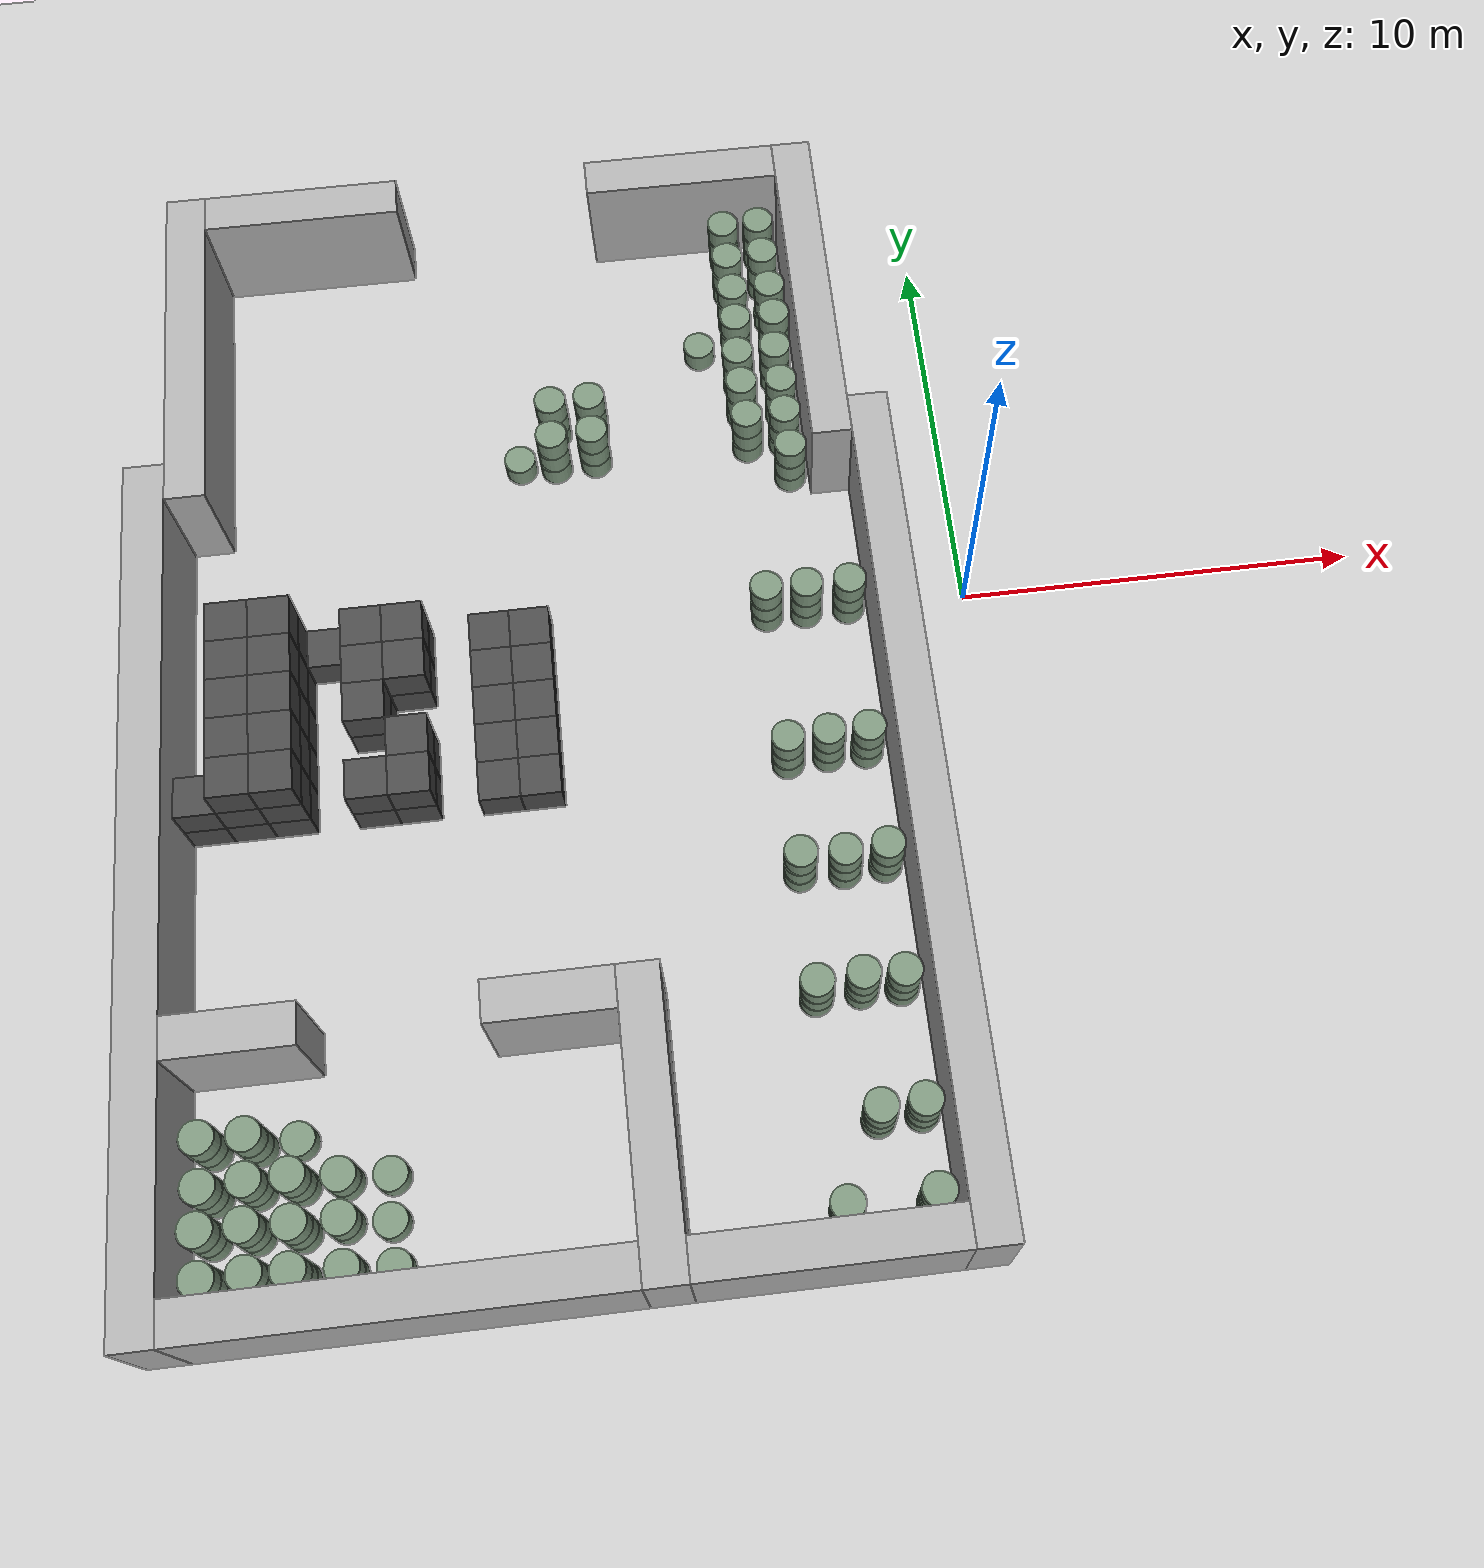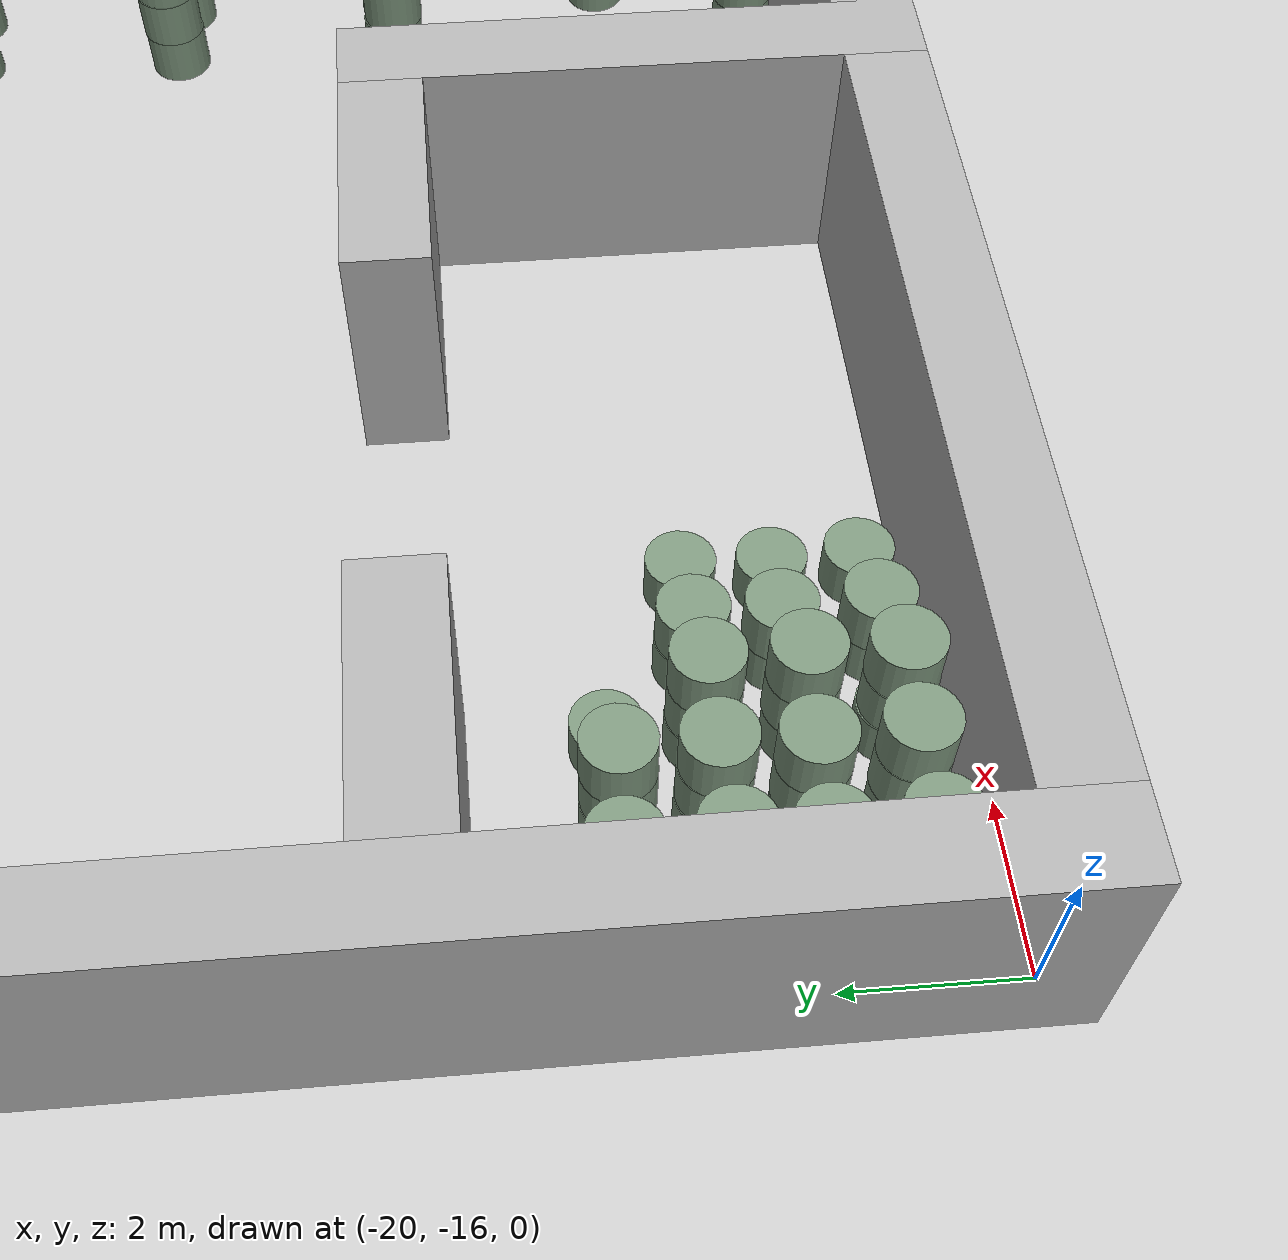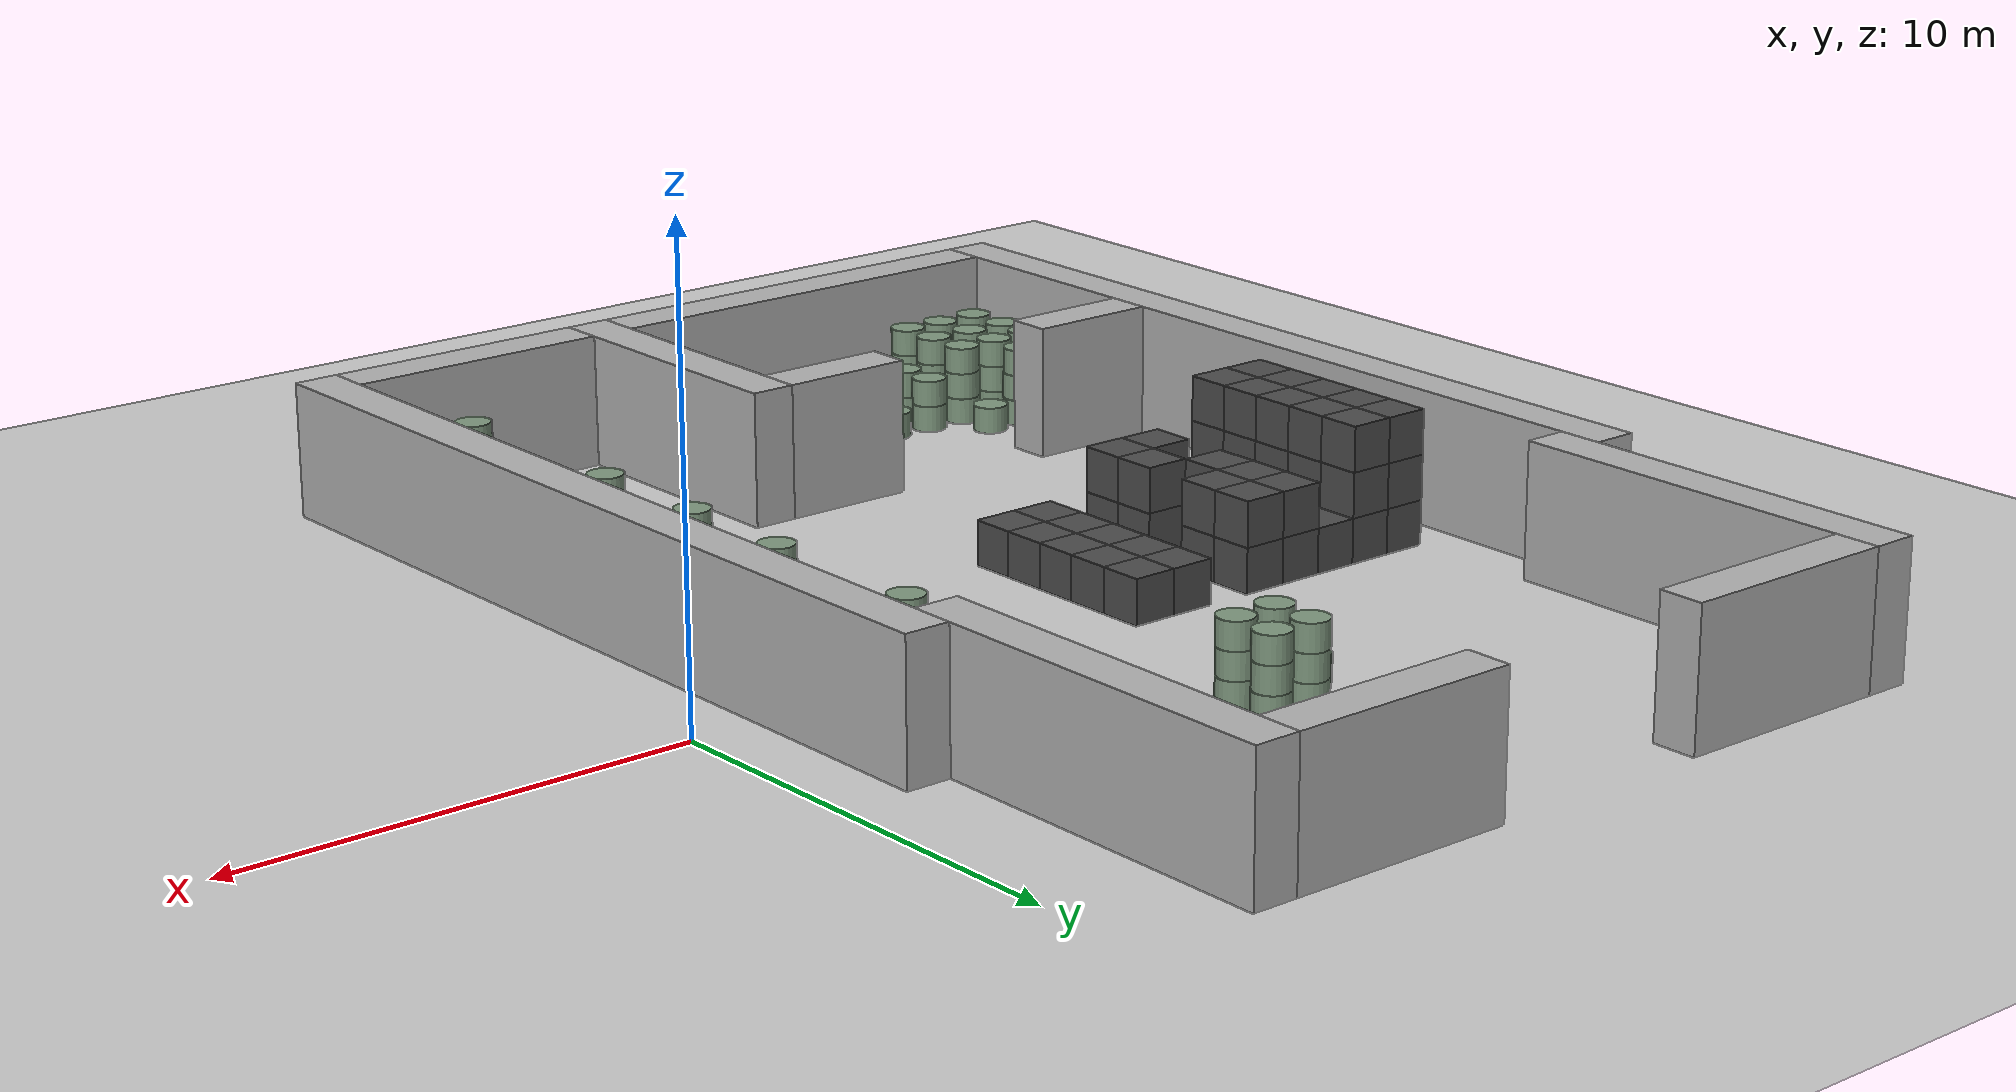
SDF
<sdf version="1.6">
 <world name="default">
  <light name="sun" type="directional">
   <cast_shadows>0</cast_shadows>
   <pose>0 0 10 0 -0 0</pose>
   <diffuse>0.8 0.8 0.8 1</diffuse>
   <specular>0.2 0.2 0.2 1</specular>
   <attenuation>
    <range>1000</range>
    <constant>0.9</constant>
    <linear>0.01</linear>
    <quadratic>0.001</quadratic>
   </attenuation>
   <direction>-0.5 0.1 -0.9</direction>
  </light>
  <include><uri>model://ground_plane</uri></include>
  <gravity>0 0 -9.8</gravity>
  <magnetic_field>6e-06 2.3e-05 -4.2e-05</magnetic_field>
  <atmosphere type="adiabatic"/>
  <physics name="default_physics" default="0" type="ode">
   <max_step_size>0.001</max_step_size>
   <real_time_factor>1</real_time_factor>
   <real_time_update_rate>1000</real_time_update_rate>
  </physics>
  <scene><ambient>0.4 0.4 0.4 1</ambient><background>0.7 0.7 0.7 1</background><shadows>0</shadows></scene>
  <spherical_coordinates>
   <surface_model>EARTH_WGS84</surface_model>
   <latitude_deg>0</latitude_deg>
   <longitude_deg>0</longitude_deg>
   <elevation>0</elevation>
   <heading_deg>0</heading_deg>
  </spherical_coordinates>
  <model name="wall_0">
   <pose>-20.0 -6.0 1.5 0 -0 0</pose>
   <static>True</static>
   <link name="link">
    <inertial>
     <mass>100</mass>
     <inertia>
      <ixx>0.166667</ixx>
      <ixy>0</ixy>
      <ixz>0</ixz>
      <iyy>0.166667</iyy>
      <iyz>0</iyz>
      <izz>0.166667</izz>
     </inertia>
    </inertial>
    <collision name="collision"><geometry><box><size>1.0 21.0 3.0</size></box></geometry></collision>
    <visual name="visual">
     <geometry><box><size>1.0 21.0 3.0</size></box></geometry>
     <material><ambient>0.7 0.7 0.7 1</ambient><diffuse>0.7 0.7 0.7 1</diffuse></material>
    </visual>
   </link>
  </model>
  <model name="wall_1">
   <pose>-19.0 8.0 1.5 0 -0 0</pose>
   <static>True</static>
   <link name="link">
    <inertial>
     <mass>100</mass>
     <inertia>
      <ixx>0.166667</ixx>
      <ixy>0</ixy>
      <ixz>0</ixz>
      <iyy>0.166667</iyy>
      <iyz>0</iyz>
      <izz>0.166667</izz>
     </inertia>
    </inertial>
    <collision name="collision"><geometry><box><size>1.0 9.0 3.0</size></box></geometry></collision>
    <visual name="visual">
     <geometry><box><size>1.0 9.0 3.0</size></box></geometry>
     <material><ambient>0.7 0.7 0.7 1</ambient><diffuse>0.7 0.7 0.7 1</diffuse></material>
    </visual>
   </link>
  </model>
  <model name="wall_2">
   <pose>-9.0 -13.0 1.5 0 -0 0</pose>
   <static>True</static>
   <link name="link">
    <inertial>
     <mass>100</mass>
     <inertia>
      <ixx>0.166667</ixx>
      <ixy>0</ixy>
      <ixz>0</ixz>
      <iyy>0.166667</iyy>
      <iyz>0</iyz>
      <izz>0.166667</izz>
     </inertia>
    </inertial>
    <collision name="collision"><geometry><box><size>1.0 7.0 3.0</size></box></geometry></collision>
    <visual name="visual">
     <geometry><box><size>1.0 7.0 3.0</size></box></geometry>
     <material><ambient>0.7 0.7 0.7 1</ambient><diffuse>0.7 0.7 0.7 1</diffuse></material>
    </visual>
   </link>
  </model>
  <model name="wall_3">
   <pose>-3.0 8.0 1.5 0 -0 0</pose>
   <static>True</static>
   <link name="link">
    <inertial>
     <mass>100</mass>
     <inertia>
      <ixx>0.166667</ixx>
      <ixy>0</ixy>
      <ixz>0</ixz>
      <iyy>0.166667</iyy>
      <iyz>0</iyz>
      <izz>0.166667</izz>
     </inertia>
    </inertial>
    <collision name="collision"><geometry><box><size>1.0 9.0 3.0</size></box></geometry></collision>
    <visual name="visual">
     <geometry><box><size>1.0 9.0 3.0</size></box></geometry>
     <material><ambient>0.7 0.7 0.7 1</ambient><diffuse>0.7 0.7 0.7 1</diffuse></material>
    </visual>
   </link>
  </model>
  <model name="wall_4">
   <pose>-2.0 -6.0 1.5 0 -0 0</pose>
   <static>True</static>
   <link name="link">
    <inertial>
     <mass>100</mass>
     <inertia>
      <ixx>0.166667</ixx>
      <ixy>0</ixy>
      <ixz>0</ixz>
      <iyy>0.166667</iyy>
      <iyz>0</iyz>
      <izz>0.166667</izz>
     </inertia>
    </inertial>
    <collision name="collision"><geometry><box><size>1.0 21.0 3.0</size></box></geometry></collision>
    <visual name="visual">
     <geometry><box><size>1.0 21.0 3.0</size></box></geometry>
     <material><ambient>0.7 0.7 0.7 1</ambient><diffuse>0.7 0.7 0.7 1</diffuse></material>
    </visual>
   </link>
  </model>
  <model name="wall_5">
   <pose>-14.5 -16.0 1.5 0 -0 0</pose>
   <static>True</static>
   <link name="link">
    <inertial>
     <mass>100</mass>
     <inertia>
      <ixx>0.166667</ixx>
      <ixy>0</ixy>
      <ixz>0</ixz>
      <iyy>0.166667</iyy>
      <iyz>0</iyz>
      <izz>0.166667</izz>
     </inertia>
    </inertial>
    <collision name="collision"><geometry><box><size>10.0 1.0 3.0</size></box></geometry></collision>
    <visual name="visual">
     <geometry><box><size>10.0 1.0 3.0</size></box></geometry>
     <material><ambient>0.7 0.7 0.7 1</ambient><diffuse>0.7 0.7 0.7 1</diffuse></material>
    </visual>
   </link>
  </model>
  <model name="wall_6">
   <pose>-5.5 -16.0 1.5 0 -0 0</pose>
   <static>True</static>
   <link name="link">
    <inertial>
     <mass>100</mass>
     <inertia>
      <ixx>0.166667</ixx>
      <ixy>0</ixy>
      <ixz>0</ixz>
      <iyy>0.166667</iyy>
      <iyz>0</iyz>
      <izz>0.166667</izz>
     </inertia>
    </inertial>
    <collision name="collision"><geometry><box><size>6.0 1.0 3.0</size></box></geometry></collision>
    <visual name="visual">
     <geometry><box><size>6.0 1.0 3.0</size></box></geometry>
     <material><ambient>0.7 0.7 0.7 1</ambient><diffuse>0.7 0.7 0.7 1</diffuse></material>
    </visual>
   </link>
  </model>
  <model name="wall_7">
   <pose>-18.0 -10.0 1.5 0 -0 0</pose>
   <static>True</static>
   <link name="link">
    <inertial>
     <mass>100</mass>
     <inertia>
      <ixx>0.166667</ixx>
      <ixy>0</ixy>
      <ixz>0</ixz>
      <iyy>0.166667</iyy>
      <iyz>0</iyz>
      <izz>0.166667</izz>
     </inertia>
    </inertial>
    <collision name="collision"><geometry><box><size>3.0 1.0 3.0</size></box></geometry></collision>
    <visual name="visual">
     <geometry><box><size>3.0 1.0 3.0</size></box></geometry>
     <material><ambient>0.7 0.7 0.7 1</ambient><diffuse>0.7 0.7 0.7 1</diffuse></material>
    </visual>
   </link>
  </model>
  <model name="wall_8">
   <pose>-11.0 -10.0 1.5 0 -0 0</pose>
   <static>True</static>
   <link name="link">
    <inertial>
     <mass>100</mass>
     <inertia>
      <ixx>0.166667</ixx>
      <ixy>0</ixy>
      <ixz>0</ixz>
      <iyy>0.166667</iyy>
      <iyz>0</iyz>
      <izz>0.166667</izz>
     </inertia>
    </inertial>
    <collision name="collision"><geometry><box><size>3.0 1.0 3.0</size></box></geometry></collision>
    <visual name="visual">
     <geometry><box><size>3.0 1.0 3.0</size></box></geometry>
     <material><ambient>0.7 0.7 0.7 1</ambient><diffuse>0.7 0.7 0.7 1</diffuse></material>
    </visual>
   </link>
  </model>
  <model name="wall_9">
   <pose>-16.0 12.0 1.5 0 -0 0</pose>
   <static>True</static>
   <link name="link">
    <inertial>
     <mass>100</mass>
     <inertia>
      <ixx>0.166667</ixx>
      <ixy>0</ixy>
      <ixz>0</ixz>
      <iyy>0.166667</iyy>
      <iyz>0</iyz>
      <izz>0.166667</izz>
     </inertia>
    </inertial>
    <collision name="collision"><geometry><box><size>5.0 1.0 3.0</size></box></geometry></collision>
    <visual name="visual">
     <geometry><box><size>5.0 1.0 3.0</size></box></geometry>
     <material><ambient>0.7 0.7 0.7 1</ambient><diffuse>0.7 0.7 0.7 1</diffuse></material>
    </visual>
   </link>
  </model>
  <model name="wall_10">
   <pose>-6.0 12.0 1.5 0 -0 0</pose>
   <static>True</static>
   <link name="link">
    <inertial>
     <mass>100</mass>
     <inertia>
      <ixx>0.166667</ixx>
      <ixy>0</ixy>
      <ixz>0</ixz>
      <iyy>0.166667</iyy>
      <iyz>0</iyz>
      <izz>0.166667</izz>
     </inertia>
    </inertial>
    <collision name="collision"><geometry><box><size>5.0 1.0 3.0</size></box></geometry></collision>
    <visual name="visual">
     <geometry><box><size>5.0 1.0 3.0</size></box></geometry>
     <material><ambient>0.7 0.7 0.7 1</ambient><diffuse>0.7 0.7 0.7 1</diffuse></material>
    </visual>
   </link>
  </model>
  <model name="unit_box_0">
   <pose>-19.0 -4.0 0.5 0 -0 0</pose>
   <static>True</static>
   <link name="link">
    <inertial>
     <mass>100</mass>
     <inertia>
      <ixx>0.166667</ixx>
      <ixy>0</ixy>
      <ixz>0</ixz>
      <iyy>0.166667</iyy>
      <iyz>0</iyz>
      <izz>0.166667</izz>
     </inertia>
    </inertial>
    <collision name="collision"><geometry><box><size>1.0 1.0 1.0</size></box></geometry></collision>
    <visual name="visual">
     <geometry><box><size>1.0 1.0 1.0</size></box></geometry>
     <material><ambient>0.3 0.3 0.3 1</ambient><diffuse>0.3 0.3 0.3 1</diffuse></material>
    </visual>
   </link>
  </model>
  <model name="unit_box_1">
   <pose>-19.0 -4.0 1.5 0 -0 0</pose>
   <static>True</static>
   <link name="link">
    <inertial>
     <mass>100</mass>
     <inertia>
      <ixx>0.166667</ixx>
      <ixy>0</ixy>
      <ixz>0</ixz>
      <iyy>0.166667</iyy>
      <iyz>0</iyz>
      <izz>0.166667</izz>
     </inertia>
    </inertial>
    <collision name="collision"><geometry><box><size>1.0 1.0 1.0</size></box></geometry></collision>
    <visual name="visual">
     <geometry><box><size>1.0 1.0 1.0</size></box></geometry>
     <material><ambient>0.3 0.3 0.3 1</ambient><diffuse>0.3 0.3 0.3 1</diffuse></material>
    </visual>
   </link>
  </model>
  <model name="unit_box_2">
   <pose>-18.0 -4.0 0.5 0 -0 0</pose>
   <static>True</static>
   <link name="link">
    <inertial>
     <mass>100</mass>
     <inertia>
      <ixx>0.166667</ixx>
      <ixy>0</ixy>
      <ixz>0</ixz>
      <iyy>0.166667</iyy>
      <iyz>0</iyz>
      <izz>0.166667</izz>
     </inertia>
    </inertial>
    <collision name="collision"><geometry><box><size>1.0 1.0 1.0</size></box></geometry></collision>
    <visual name="visual">
     <geometry><box><size>1.0 1.0 1.0</size></box></geometry>
     <material><ambient>0.3 0.3 0.3 1</ambient><diffuse>0.3 0.3 0.3 1</diffuse></material>
    </visual>
   </link>
  </model>
  <model name="unit_box_3">
   <pose>-18.0 -4.0 1.5 0 -0 0</pose>
   <static>True</static>
   <link name="link">
    <inertial>
     <mass>100</mass>
     <inertia>
      <ixx>0.166667</ixx>
      <ixy>0</ixy>
      <ixz>0</ixz>
      <iyy>0.166667</iyy>
      <iyz>0</iyz>
      <izz>0.166667</izz>
     </inertia>
    </inertial>
    <collision name="collision"><geometry><box><size>1.0 1.0 1.0</size></box></geometry></collision>
    <visual name="visual">
     <geometry><box><size>1.0 1.0 1.0</size></box></geometry>
     <material><ambient>0.3 0.3 0.3 1</ambient><diffuse>0.3 0.3 0.3 1</diffuse></material>
    </visual>
   </link>
  </model>
  <model name="unit_box_4">
   <pose>-18.0 -4.0 2.5 0 -0 0</pose>
   <static>True</static>
   <link name="link">
    <inertial>
     <mass>100</mass>
     <inertia>
      <ixx>0.166667</ixx>
      <ixy>0</ixy>
      <ixz>0</ixz>
      <iyy>0.166667</iyy>
      <iyz>0</iyz>
      <izz>0.166667</izz>
     </inertia>
    </inertial>
    <collision name="collision"><geometry><box><size>1.0 1.0 1.0</size></box></geometry></collision>
    <visual name="visual">
     <geometry><box><size>1.0 1.0 1.0</size></box></geometry>
     <material><ambient>0.3 0.3 0.3 1</ambient><diffuse>0.3 0.3 0.3 1</diffuse></material>
    </visual>
   </link>
  </model>
  <model name="unit_box_5">
   <pose>-18.0 -3.0 0.5 0 -0 0</pose>
   <static>True</static>
   <link name="link">
    <inertial>
     <mass>100</mass>
     <inertia>
      <ixx>0.166667</ixx>
      <ixy>0</ixy>
      <ixz>0</ixz>
      <iyy>0.166667</iyy>
      <iyz>0</iyz>
      <izz>0.166667</izz>
     </inertia>
    </inertial>
    <collision name="collision"><geometry><box><size>1.0 1.0 1.0</size></box></geometry></collision>
    <visual name="visual">
     <geometry><box><size>1.0 1.0 1.0</size></box></geometry>
     <material><ambient>0.3 0.3 0.3 1</ambient><diffuse>0.3 0.3 0.3 1</diffuse></material>
    </visual>
   </link>
  </model>
  <model name="unit_box_6">
   <pose>-18.0 -3.0 1.5 0 -0 0</pose>
   <static>True</static>
   <link name="link">
    <inertial>
     <mass>100</mass>
     <inertia>
      <ixx>0.166667</ixx>
      <ixy>0</ixy>
      <ixz>0</ixz>
      <iyy>0.166667</iyy>
      <iyz>0</iyz>
      <izz>0.166667</izz>
     </inertia>
    </inertial>
    <collision name="collision"><geometry><box><size>1.0 1.0 1.0</size></box></geometry></collision>
    <visual name="visual">
     <geometry><box><size>1.0 1.0 1.0</size></box></geometry>
     <material><ambient>0.3 0.3 0.3 1</ambient><diffuse>0.3 0.3 0.3 1</diffuse></material>
    </visual>
   </link>
  </model>
  <model name="unit_box_7">
   <pose>-18.0 -3.0 2.5 0 -0 0</pose>
   <static>True</static>
   <link name="link">
    <inertial>
     <mass>100</mass>
     <inertia>
      <ixx>0.166667</ixx>
      <ixy>0</ixy>
      <ixz>0</ixz>
      <iyy>0.166667</iyy>
      <iyz>0</iyz>
      <izz>0.166667</izz>
     </inertia>
    </inertial>
    <collision name="collision"><geometry><box><size>1.0 1.0 1.0</size></box></geometry></collision>
    <visual name="visual">
     <geometry><box><size>1.0 1.0 1.0</size></box></geometry>
     <material><ambient>0.3 0.3 0.3 1</ambient><diffuse>0.3 0.3 0.3 1</diffuse></material>
    </visual>
   </link>
  </model>
  <model name="unit_box_8">
   <pose>-18.0 -2.0 0.5 0 -0 0</pose>
   <static>True</static>
   <link name="link">
    <inertial>
     <mass>100</mass>
     <inertia>
      <ixx>0.166667</ixx>
      <ixy>0</ixy>
      <ixz>0</ixz>
      <iyy>0.166667</iyy>
      <iyz>0</iyz>
      <izz>0.166667</izz>
     </inertia>
    </inertial>
    <collision name="collision"><geometry><box><size>1.0 1.0 1.0</size></box></geometry></collision>
    <visual name="visual">
     <geometry><box><size>1.0 1.0 1.0</size></box></geometry>
     <material><ambient>0.3 0.3 0.3 1</ambient><diffuse>0.3 0.3 0.3 1</diffuse></material>
    </visual>
   </link>
  </model>
  <model name="unit_box_9">
   <pose>-18.0 -2.0 1.5 0 -0 0</pose>
   <static>True</static>
   <link name="link">
    <inertial>
     <mass>100</mass>
     <inertia>
      <ixx>0.166667</ixx>
      <ixy>0</ixy>
      <ixz>0</ixz>
      <iyy>0.166667</iyy>
      <iyz>0</iyz>
      <izz>0.166667</izz>
     </inertia>
    </inertial>
    <collision name="collision"><geometry><box><size>1.0 1.0 1.0</size></box></geometry></collision>
    <visual name="visual">
     <geometry><box><size>1.0 1.0 1.0</size></box></geometry>
     <material><ambient>0.3 0.3 0.3 1</ambient><diffuse>0.3 0.3 0.3 1</diffuse></material>
    </visual>
   </link>
  </model>
  <model name="unit_box_10">
   <pose>-18.0 -2.0 2.5 0 -0 0</pose>
   <static>True</static>
   <link name="link">
    <inertial>
     <mass>100</mass>
     <inertia>
      <ixx>0.166667</ixx>
      <ixy>0</ixy>
      <ixz>0</ixz>
      <iyy>0.166667</iyy>
      <iyz>0</iyz>
      <izz>0.166667</izz>
     </inertia>
    </inertial>
    <collision name="collision"><geometry><box><size>1.0 1.0 1.0</size></box></geometry></collision>
    <visual name="visual">
     <geometry><box><size>1.0 1.0 1.0</size></box></geometry>
     <material><ambient>0.3 0.3 0.3 1</ambient><diffuse>0.3 0.3 0.3 1</diffuse></material>
    </visual>
   </link>
  </model>
  <model name="unit_box_11">
   <pose>-18.0 -1.0 0.5 0 -0 0</pose>
   <static>True</static>
   <link name="link">
    <inertial>
     <mass>100</mass>
     <inertia>
      <ixx>0.166667</ixx>
      <ixy>0</ixy>
      <ixz>0</ixz>
      <iyy>0.166667</iyy>
      <iyz>0</iyz>
      <izz>0.166667</izz>
     </inertia>
    </inertial>
    <collision name="collision"><geometry><box><size>1.0 1.0 1.0</size></box></geometry></collision>
    <visual name="visual">
     <geometry><box><size>1.0 1.0 1.0</size></box></geometry>
     <material><ambient>0.3 0.3 0.3 1</ambient><diffuse>0.3 0.3 0.3 1</diffuse></material>
    </visual>
   </link>
  </model>
  <model name="unit_box_12">
   <pose>-18.0 -1.0 1.5 0 -0 0</pose>
   <static>True</static>
   <link name="link">
    <inertial>
     <mass>100</mass>
     <inertia>
      <ixx>0.166667</ixx>
      <ixy>0</ixy>
      <ixz>0</ixz>
      <iyy>0.166667</iyy>
      <iyz>0</iyz>
      <izz>0.166667</izz>
     </inertia>
    </inertial>
    <collision name="collision"><geometry><box><size>1.0 1.0 1.0</size></box></geometry></collision>
    <visual name="visual">
     <geometry><box><size>1.0 1.0 1.0</size></box></geometry>
     <material><ambient>0.3 0.3 0.3 1</ambient><diffuse>0.3 0.3 0.3 1</diffuse></material>
    </visual>
   </link>
  </model>
  <model name="unit_box_13">
   <pose>-18.0 -1.0 2.5 0 -0 0</pose>
   <static>True</static>
   <link name="link">
    <inertial>
     <mass>100</mass>
     <inertia>
      <ixx>0.166667</ixx>
      <ixy>0</ixy>
      <ixz>0</ixz>
      <iyy>0.166667</iyy>
      <iyz>0</iyz>
      <izz>0.166667</izz>
     </inertia>
    </inertial>
    <collision name="collision"><geometry><box><size>1.0 1.0 1.0</size></box></geometry></collision>
    <visual name="visual">
     <geometry><box><size>1.0 1.0 1.0</size></box></geometry>
     <material><ambient>0.3 0.3 0.3 1</ambient><diffuse>0.3 0.3 0.3 1</diffuse></material>
    </visual>
   </link>
  </model>
  <model name="unit_box_14">
   <pose>-18.0 0.0 0.5 0 -0 0</pose>
   <static>True</static>
   <link name="link">
    <inertial>
     <mass>100</mass>
     <inertia>
      <ixx>0.166667</ixx>
      <ixy>0</ixy>
      <ixz>0</ixz>
      <iyy>0.166667</iyy>
      <iyz>0</iyz>
      <izz>0.166667</izz>
     </inertia>
    </inertial>
    <collision name="collision"><geometry><box><size>1.0 1.0 1.0</size></box></geometry></collision>
    <visual name="visual">
     <geometry><box><size>1.0 1.0 1.0</size></box></geometry>
     <material><ambient>0.3 0.3 0.3 1</ambient><diffuse>0.3 0.3 0.3 1</diffuse></material>
    </visual>
   </link>
  </model>
  <model name="unit_box_15">
   <pose>-18.0 0.0 1.5 0 -0 0</pose>
   <static>True</static>
   <link name="link">
    <inertial>
     <mass>100</mass>
     <inertia>
      <ixx>0.166667</ixx>
      <ixy>0</ixy>
      <ixz>0</ixz>
      <iyy>0.166667</iyy>
      <iyz>0</iyz>
      <izz>0.166667</izz>
     </inertia>
    </inertial>
    <collision name="collision"><geometry><box><size>1.0 1.0 1.0</size></box></geometry></collision>
    <visual name="visual">
     <geometry><box><size>1.0 1.0 1.0</size></box></geometry>
     <material><ambient>0.3 0.3 0.3 1</ambient><diffuse>0.3 0.3 0.3 1</diffuse></material>
    </visual>
   </link>
  </model>
  <model name="unit_box_16">
   <pose>-18.0 0.0 2.5 0 -0 0</pose>
   <static>True</static>
   <link name="link">
    <inertial>
     <mass>100</mass>
     <inertia>
      <ixx>0.166667</ixx>
      <ixy>0</ixy>
      <ixz>0</ixz>
      <iyy>0.166667</iyy>
      <iyz>0</iyz>
      <izz>0.166667</izz>
     </inertia>
    </inertial>
    <collision name="collision"><geometry><box><size>1.0 1.0 1.0</size></box></geometry></collision>
    <visual name="visual">
     <geometry><box><size>1.0 1.0 1.0</size></box></geometry>
     <material><ambient>0.3 0.3 0.3 1</ambient><diffuse>0.3 0.3 0.3 1</diffuse></material>
    </visual>
   </link>
  </model>
  <model name="unit_box_17">
   <pose>-17.0 -4.0 0.5 0 -0 0</pose>
   <static>True</static>
   <link name="link">
    <inertial>
     <mass>100</mass>
     <inertia>
      <ixx>0.166667</ixx>
      <ixy>0</ixy>
      <ixz>0</ixz>
      <iyy>0.166667</iyy>
      <iyz>0</iyz>
      <izz>0.166667</izz>
     </inertia>
    </inertial>
    <collision name="collision"><geometry><box><size>1.0 1.0 1.0</size></box></geometry></collision>
    <visual name="visual">
     <geometry><box><size>1.0 1.0 1.0</size></box></geometry>
     <material><ambient>0.3 0.3 0.3 1</ambient><diffuse>0.3 0.3 0.3 1</diffuse></material>
    </visual>
   </link>
  </model>
  <model name="unit_box_18">
   <pose>-17.0 -4.0 1.5 0 -0 0</pose>
   <static>True</static>
   <link name="link">
    <inertial>
     <mass>100</mass>
     <inertia>
      <ixx>0.166667</ixx>
      <ixy>0</ixy>
      <ixz>0</ixz>
      <iyy>0.166667</iyy>
      <iyz>0</iyz>
      <izz>0.166667</izz>
     </inertia>
    </inertial>
    <collision name="collision"><geometry><box><size>1.0 1.0 1.0</size></box></geometry></collision>
    <visual name="visual">
     <geometry><box><size>1.0 1.0 1.0</size></box></geometry>
     <material><ambient>0.3 0.3 0.3 1</ambient><diffuse>0.3 0.3 0.3 1</diffuse></material>
    </visual>
   </link>
  </model>
  <model name="unit_box_19">
   <pose>-17.0 -4.0 2.5 0 -0 0</pose>
   <static>True</static>
   <link name="link">
    <inertial>
     <mass>100</mass>
     <inertia>
      <ixx>0.166667</ixx>
      <ixy>0</ixy>
      <ixz>0</ixz>
      <iyy>0.166667</iyy>
      <iyz>0</iyz>
      <izz>0.166667</izz>
     </inertia>
    </inertial>
    <collision name="collision"><geometry><box><size>1.0 1.0 1.0</size></box></geometry></collision>
    <visual name="visual">
     <geometry><box><size>1.0 1.0 1.0</size></box></geometry>
     <material><ambient>0.3 0.3 0.3 1</ambient><diffuse>0.3 0.3 0.3 1</diffuse></material>
    </visual>
   </link>
  </model>
  <model name="unit_box_20">
   <pose>-17.0 -3.0 0.5 0 -0 0</pose>
   <static>True</static>
   <link name="link">
    <inertial>
     <mass>100</mass>
     <inertia>
      <ixx>0.166667</ixx>
      <ixy>0</ixy>
      <ixz>0</ixz>
      <iyy>0.166667</iyy>
      <iyz>0</iyz>
      <izz>0.166667</izz>
     </inertia>
    </inertial>
    <collision name="collision"><geometry><box><size>1.0 1.0 1.0</size></box></geometry></collision>
    <visual name="visual">
     <geometry><box><size>1.0 1.0 1.0</size></box></geometry>
     <material><ambient>0.3 0.3 0.3 1</ambient><diffuse>0.3 0.3 0.3 1</diffuse></material>
    </visual>
   </link>
  </model>
  <model name="unit_box_21">
   <pose>-17.0 -3.0 1.5 0 -0 0</pose>
   <static>True</static>
   <link name="link">
    <inertial>
     <mass>100</mass>
     <inertia>
      <ixx>0.166667</ixx>
      <ixy>0</ixy>
      <ixz>0</ixz>
      <iyy>0.166667</iyy>
      <iyz>0</iyz>
      <izz>0.166667</izz>
     </inertia>
    </inertial>
    <collision name="collision"><geometry><box><size>1.0 1.0 1.0</size></box></geometry></collision>
    <visual name="visual">
     <geometry><box><size>1.0 1.0 1.0</size></box></geometry>
     <material><ambient>0.3 0.3 0.3 1</ambient><diffuse>0.3 0.3 0.3 1</diffuse></material>
    </visual>
   </link>
  </model>
  <model name="unit_box_22">
   <pose>-17.0 -3.0 2.5 0 -0 0</pose>
   <static>True</static>
   <link name="link">
    <inertial>
     <mass>100</mass>
     <inertia>
      <ixx>0.166667</ixx>
      <ixy>0</ixy>
      <ixz>0</ixz>
      <iyy>0.166667</iyy>
      <iyz>0</iyz>
      <izz>0.166667</izz>
     </inertia>
    </inertial>
    <collision name="collision"><geometry><box><size>1.0 1.0 1.0</size></box></geometry></collision>
    <visual name="visual">
     <geometry><box><size>1.0 1.0 1.0</size></box></geometry>
     <material><ambient>0.3 0.3 0.3 1</ambient><diffuse>0.3 0.3 0.3 1</diffuse></material>
    </visual>
   </link>
  </model>
  <model name="unit_box_23">
   <pose>-17.0 -2.0 0.5 0 -0 0</pose>
   <static>True</static>
   <link name="link">
    <inertial>
     <mass>100</mass>
     <inertia>
      <ixx>0.166667</ixx>
      <ixy>0</ixy>
      <ixz>0</ixz>
      <iyy>0.166667</iyy>
      <iyz>0</iyz>
      <izz>0.166667</izz>
     </inertia>
    </inertial>
    <collision name="collision"><geometry><box><size>1.0 1.0 1.0</size></box></geometry></collision>
    <visual name="visual">
     <geometry><box><size>1.0 1.0 1.0</size></box></geometry>
     <material><ambient>0.3 0.3 0.3 1</ambient><diffuse>0.3 0.3 0.3 1</diffuse></material>
    </visual>
   </link>
  </model>
  <model name="unit_box_24">
   <pose>-17.0 -2.0 1.5 0 -0 0</pose>
   <static>True</static>
   <link name="link">
    <inertial>
     <mass>100</mass>
     <inertia>
      <ixx>0.166667</ixx>
      <ixy>0</ixy>
      <ixz>0</ixz>
      <iyy>0.166667</iyy>
      <iyz>0</iyz>
      <izz>0.166667</izz>
     </inertia>
    </inertial>
    <collision name="collision"><geometry><box><size>1.0 1.0 1.0</size></box></geometry></collision>
    <visual name="visual">
     <geometry><box><size>1.0 1.0 1.0</size></box></geometry>
     <material><ambient>0.3 0.3 0.3 1</ambient><diffuse>0.3 0.3 0.3 1</diffuse></material>
    </visual>
   </link>
  </model>
  <model name="unit_box_25">
   <pose>-17.0 -2.0 2.5 0 -0 0</pose>
   <static>True</static>
   <link name="link">
    <inertial>
     <mass>100</mass>
     <inertia>
      <ixx>0.166667</ixx>
      <ixy>0</ixy>
      <ixz>0</ixz>
      <iyy>0.166667</iyy>
      <iyz>0</iyz>
      <izz>0.166667</izz>
     </inertia>
    </inertial>
    <collision name="collision"><geometry><box><size>1.0 1.0 1.0</size></box></geometry></collision>
    <visual name="visual">
     <geometry><box><size>1.0 1.0 1.0</size></box></geometry>
     <material><ambient>0.3 0.3 0.3 1</ambient><diffuse>0.3 0.3 0.3 1</diffuse></material>
    </visual>
   </link>
  </model>
  <model name="unit_box_26">
   <pose>-17.0 -1.0 0.5 0 -0 0</pose>
   <static>True</static>
   <link name="link">
    <inertial>
     <mass>100</mass>
     <inertia>
      <ixx>0.166667</ixx>
      <ixy>0</ixy>
      <ixz>0</ixz>
      <iyy>0.166667</iyy>
      <iyz>0</iyz>
      <izz>0.166667</izz>
     </inertia>
    </inertial>
    <collision name="collision"><geometry><box><size>1.0 1.0 1.0</size></box></geometry></collision>
    <visual name="visual">
     <geometry><box><size>1.0 1.0 1.0</size></box></geometry>
     <material><ambient>0.3 0.3 0.3 1</ambient><diffuse>0.3 0.3 0.3 1</diffuse></material>
    </visual>
   </link>
  </model>
  <model name="unit_box_27">
   <pose>-17.0 -1.0 1.5 0 -0 0</pose>
   <static>True</static>
   <link name="link">
    <inertial>
     <mass>100</mass>
     <inertia>
      <ixx>0.166667</ixx>
      <ixy>0</ixy>
      <ixz>0</ixz>
      <iyy>0.166667</iyy>
      <iyz>0</iyz>
      <izz>0.166667</izz>
     </inertia>
    </inertial>
    <collision name="collision"><geometry><box><size>1.0 1.0 1.0</size></box></geometry></collision>
    <visual name="visual">
     <geometry><box><size>1.0 1.0 1.0</size></box></geometry>
     <material><ambient>0.3 0.3 0.3 1</ambient><diffuse>0.3 0.3 0.3 1</diffuse></material>
    </visual>
   </link>
  </model>
  <model name="unit_box_28">
   <pose>-17.0 -1.0 2.5 0 -0 0</pose>
   <static>True</static>
   <link name="link">
    <inertial>
     <mass>100</mass>
     <inertia>
      <ixx>0.166667</ixx>
      <ixy>0</ixy>
      <ixz>0</ixz>
      <iyy>0.166667</iyy>
      <iyz>0</iyz>
      <izz>0.166667</izz>
     </inertia>
    </inertial>
    <collision name="collision"><geometry><box><size>1.0 1.0 1.0</size></box></geometry></collision>
    <visual name="visual">
     <geometry><box><size>1.0 1.0 1.0</size></box></geometry>
     <material><ambient>0.3 0.3 0.3 1</ambient><diffuse>0.3 0.3 0.3 1</diffuse></material>
    </visual>
   </link>
  </model>
  <model name="unit_box_29">
   <pose>-17.0 0.0 0.5 0 -0 0</pose>
   <static>True</static>
   <link name="link">
    <inertial>
     <mass>100</mass>
     <inertia>
      <ixx>0.166667</ixx>
      <ixy>0</ixy>
      <ixz>0</ixz>
      <iyy>0.166667</iyy>
      <iyz>0</iyz>
      <izz>0.166667</izz>
     </inertia>
    </inertial>
    <collision name="collision"><geometry><box><size>1.0 1.0 1.0</size></box></geometry></collision>
    <visual name="visual">
     <geometry><box><size>1.0 1.0 1.0</size></box></geometry>
     <material><ambient>0.3 0.3 0.3 1</ambient><diffuse>0.3 0.3 0.3 1</diffuse></material>
    </visual>
   </link>
  </model>
  <model name="unit_box_30">
   <pose>-17.0 0.0 1.5 0 -0 0</pose>
   <static>True</static>
   <link name="link">
    <inertial>
     <mass>100</mass>
     <inertia>
      <ixx>0.166667</ixx>
      <ixy>0</ixy>
      <ixz>0</ixz>
      <iyy>0.166667</iyy>
      <iyz>0</iyz>
      <izz>0.166667</izz>
     </inertia>
    </inertial>
    <collision name="collision"><geometry><box><size>1.0 1.0 1.0</size></box></geometry></collision>
    <visual name="visual">
     <geometry><box><size>1.0 1.0 1.0</size></box></geometry>
     <material><ambient>0.3 0.3 0.3 1</ambient><diffuse>0.3 0.3 0.3 1</diffuse></material>
    </visual>
   </link>
  </model>
  <model name="unit_box_31">
   <pose>-17.0 0.0 2.5 0 -0 0</pose>
   <static>True</static>
   <link name="link">
    <inertial>
     <mass>100</mass>
     <inertia>
      <ixx>0.166667</ixx>
      <ixy>0</ixy>
      <ixz>0</ixz>
      <iyy>0.166667</iyy>
      <iyz>0</iyz>
      <izz>0.166667</izz>
     </inertia>
    </inertial>
    <collision name="collision"><geometry><box><size>1.0 1.0 1.0</size></box></geometry></collision>
    <visual name="visual">
     <geometry><box><size>1.0 1.0 1.0</size></box></geometry>
     <material><ambient>0.3 0.3 0.3 1</ambient><diffuse>0.3 0.3 0.3 1</diffuse></material>
    </visual>
   </link>
  </model>
  <model name="unit_box_32">
   <pose>-16.0 0.0 0.5 0 -0 0</pose>
   <static>True</static>
   <link name="link">
    <inertial>
     <mass>100</mass>
     <inertia>
      <ixx>0.166667</ixx>
      <ixy>0</ixy>
      <ixz>0</ixz>
      <iyy>0.166667</iyy>
      <iyz>0</iyz>
      <izz>0.166667</izz>
     </inertia>
    </inertial>
    <collision name="collision"><geometry><box><size>1.0 1.0 1.0</size></box></geometry></collision>
    <visual name="visual">
     <geometry><box><size>1.0 1.0 1.0</size></box></geometry>
     <material><ambient>0.3 0.3 0.3 1</ambient><diffuse>0.3 0.3 0.3 1</diffuse></material>
    </visual>
   </link>
  </model>
  <model name="unit_box_33">
   <pose>-15.0 -4.0 0.5 0 -0 0</pose>
   <static>True</static>
   <link name="link">
    <inertial>
     <mass>100</mass>
     <inertia>
      <ixx>0.166667</ixx>
      <ixy>0</ixy>
      <ixz>0</ixz>
      <iyy>0.166667</iyy>
      <iyz>0</iyz>
      <izz>0.166667</izz>
     </inertia>
    </inertial>
    <collision name="collision"><geometry><box><size>1.0 1.0 1.0</size></box></geometry></collision>
    <visual name="visual">
     <geometry><box><size>1.0 1.0 1.0</size></box></geometry>
     <material><ambient>0.3 0.3 0.3 1</ambient><diffuse>0.3 0.3 0.3 1</diffuse></material>
    </visual>
   </link>
  </model>
  <model name="unit_box_34">
   <pose>-15.0 -4.0 1.5 0 -0 0</pose>
   <static>True</static>
   <link name="link">
    <inertial>
     <mass>100</mass>
     <inertia>
      <ixx>0.166667</ixx>
      <ixy>0</ixy>
      <ixz>0</ixz>
      <iyy>0.166667</iyy>
      <iyz>0</iyz>
      <izz>0.166667</izz>
     </inertia>
    </inertial>
    <collision name="collision"><geometry><box><size>1.0 1.0 1.0</size></box></geometry></collision>
    <visual name="visual">
     <geometry><box><size>1.0 1.0 1.0</size></box></geometry>
     <material><ambient>0.3 0.3 0.3 1</ambient><diffuse>0.3 0.3 0.3 1</diffuse></material>
    </visual>
   </link>
  </model>
  <model name="unit_box_35">
   <pose>-15.0 -2.0 0.5 0 -0 0</pose>
   <static>True</static>
   <link name="link">
    <inertial>
     <mass>100</mass>
     <inertia>
      <ixx>0.166667</ixx>
      <ixy>0</ixy>
      <ixz>0</ixz>
      <iyy>0.166667</iyy>
      <iyz>0</iyz>
      <izz>0.166667</izz>
     </inertia>
    </inertial>
    <collision name="collision"><geometry><box><size>1.0 1.0 1.0</size></box></geometry></collision>
    <visual name="visual">
     <geometry><box><size>1.0 1.0 1.0</size></box></geometry>
     <material><ambient>0.3 0.3 0.3 1</ambient><diffuse>0.3 0.3 0.3 1</diffuse></material>
    </visual>
   </link>
  </model>
  <model name="unit_box_36">
   <pose>-15.0 -2.0 1.5 0 -0 0</pose>
   <static>True</static>
   <link name="link">
    <inertial>
     <mass>100</mass>
     <inertia>
      <ixx>0.166667</ixx>
      <ixy>0</ixy>
      <ixz>0</ixz>
      <iyy>0.166667</iyy>
      <iyz>0</iyz>
      <izz>0.166667</izz>
     </inertia>
    </inertial>
    <collision name="collision"><geometry><box><size>1.0 1.0 1.0</size></box></geometry></collision>
    <visual name="visual">
     <geometry><box><size>1.0 1.0 1.0</size></box></geometry>
     <material><ambient>0.3 0.3 0.3 1</ambient><diffuse>0.3 0.3 0.3 1</diffuse></material>
    </visual>
   </link>
  </model>
  <model name="unit_box_37">
   <pose>-15.0 -1.0 0.5 0 -0 0</pose>
   <static>True</static>
   <link name="link">
    <inertial>
     <mass>100</mass>
     <inertia>
      <ixx>0.166667</ixx>
      <ixy>0</ixy>
      <ixz>0</ixz>
      <iyy>0.166667</iyy>
      <iyz>0</iyz>
      <izz>0.166667</izz>
     </inertia>
    </inertial>
    <collision name="collision"><geometry><box><size>1.0 1.0 1.0</size></box></geometry></collision>
    <visual name="visual">
     <geometry><box><size>1.0 1.0 1.0</size></box></geometry>
     <material><ambient>0.3 0.3 0.3 1</ambient><diffuse>0.3 0.3 0.3 1</diffuse></material>
    </visual>
   </link>
  </model>
  <model name="unit_box_38">
   <pose>-15.0 -1.0 1.5 0 -0 0</pose>
   <static>True</static>
   <link name="link">
    <inertial>
     <mass>100</mass>
     <inertia>
      <ixx>0.166667</ixx>
      <ixy>0</ixy>
      <ixz>0</ixz>
      <iyy>0.166667</iyy>
      <iyz>0</iyz>
      <izz>0.166667</izz>
     </inertia>
    </inertial>
    <collision name="collision"><geometry><box><size>1.0 1.0 1.0</size></box></geometry></collision>
    <visual name="visual">
     <geometry><box><size>1.0 1.0 1.0</size></box></geometry>
     <material><ambient>0.3 0.3 0.3 1</ambient><diffuse>0.3 0.3 0.3 1</diffuse></material>
    </visual>
   </link>
  </model>
  <model name="unit_box_39">
   <pose>-15.0 0.0 0.5 0 -0 0</pose>
   <static>True</static>
   <link name="link">
    <inertial>
     <mass>100</mass>
     <inertia>
      <ixx>0.166667</ixx>
      <ixy>0</ixy>
      <ixz>0</ixz>
      <iyy>0.166667</iyy>
      <iyz>0</iyz>
      <izz>0.166667</izz>
     </inertia>
    </inertial>
    <collision name="collision"><geometry><box><size>1.0 1.0 1.0</size></box></geometry></collision>
    <visual name="visual">
     <geometry><box><size>1.0 1.0 1.0</size></box></geometry>
     <material><ambient>0.3 0.3 0.3 1</ambient><diffuse>0.3 0.3 0.3 1</diffuse></material>
    </visual>
   </link>
  </model>
  <model name="unit_box_40">
   <pose>-15.0 0.0 1.5 0 -0 0</pose>
   <static>True</static>
   <link name="link">
    <inertial>
     <mass>100</mass>
     <inertia>
      <ixx>0.166667</ixx>
      <ixy>0</ixy>
      <ixz>0</ixz>
      <iyy>0.166667</iyy>
      <iyz>0</iyz>
      <izz>0.166667</izz>
     </inertia>
    </inertial>
    <collision name="collision"><geometry><box><size>1.0 1.0 1.0</size></box></geometry></collision>
    <visual name="visual">
     <geometry><box><size>1.0 1.0 1.0</size></box></geometry>
     <material><ambient>0.3 0.3 0.3 1</ambient><diffuse>0.3 0.3 0.3 1</diffuse></material>
    </visual>
   </link>
  </model>
  <model name="unit_box_41">
   <pose>-14.0 -4.0 0.5 0 -0 0</pose>
   <static>True</static>
   <link name="link">
    <inertial>
     <mass>100</mass>
     <inertia>
      <ixx>0.166667</ixx>
      <ixy>0</ixy>
      <ixz>0</ixz>
      <iyy>0.166667</iyy>
      <iyz>0</iyz>
      <izz>0.166667</izz>
     </inertia>
    </inertial>
    <collision name="collision"><geometry><box><size>1.0 1.0 1.0</size></box></geometry></collision>
    <visual name="visual">
     <geometry><box><size>1.0 1.0 1.0</size></box></geometry>
     <material><ambient>0.3 0.3 0.3 1</ambient><diffuse>0.3 0.3 0.3 1</diffuse></material>
    </visual>
   </link>
  </model>
  <model name="unit_box_42">
   <pose>-14.0 -4.0 1.5 0 -0 0</pose>
   <static>True</static>
   <link name="link">
    <inertial>
     <mass>100</mass>
     <inertia>
      <ixx>0.166667</ixx>
      <ixy>0</ixy>
      <ixz>0</ixz>
      <iyy>0.166667</iyy>
      <iyz>0</iyz>
      <izz>0.166667</izz>
     </inertia>
    </inertial>
    <collision name="collision"><geometry><box><size>1.0 1.0 1.0</size></box></geometry></collision>
    <visual name="visual">
     <geometry><box><size>1.0 1.0 1.0</size></box></geometry>
     <material><ambient>0.3 0.3 0.3 1</ambient><diffuse>0.3 0.3 0.3 1</diffuse></material>
    </visual>
   </link>
  </model>
  <model name="unit_box_43">
   <pose>-14.0 -3.0 0.5 0 -0 0</pose>
   <static>True</static>
   <link name="link">
    <inertial>
     <mass>100</mass>
     <inertia>
      <ixx>0.166667</ixx>
      <ixy>0</ixy>
      <ixz>0</ixz>
      <iyy>0.166667</iyy>
      <iyz>0</iyz>
      <izz>0.166667</izz>
     </inertia>
    </inertial>
    <collision name="collision"><geometry><box><size>1.0 1.0 1.0</size></box></geometry></collision>
    <visual name="visual">
     <geometry><box><size>1.0 1.0 1.0</size></box></geometry>
     <material><ambient>0.3 0.3 0.3 1</ambient><diffuse>0.3 0.3 0.3 1</diffuse></material>
    </visual>
   </link>
  </model>
  <model name="unit_box_44">
   <pose>-14.0 -3.0 1.5 0 -0 0</pose>
   <static>True</static>
   <link name="link">
    <inertial>
     <mass>100</mass>
     <inertia>
      <ixx>0.166667</ixx>
      <ixy>0</ixy>
      <ixz>0</ixz>
      <iyy>0.166667</iyy>
      <iyz>0</iyz>
      <izz>0.166667</izz>
     </inertia>
    </inertial>
    <collision name="collision"><geometry><box><size>1.0 1.0 1.0</size></box></geometry></collision>
    <visual name="visual">
     <geometry><box><size>1.0 1.0 1.0</size></box></geometry>
     <material><ambient>0.3 0.3 0.3 1</ambient><diffuse>0.3 0.3 0.3 1</diffuse></material>
    </visual>
   </link>
  </model>
  <model name="unit_box_45">
   <pose>-14.0 -1.0 0.5 0 -0 0</pose>
   <static>True</static>
   <link name="link">
    <inertial>
     <mass>100</mass>
     <inertia>
      <ixx>0.166667</ixx>
      <ixy>0</ixy>
      <ixz>0</ixz>
      <iyy>0.166667</iyy>
      <iyz>0</iyz>
      <izz>0.166667</izz>
     </inertia>
    </inertial>
    <collision name="collision"><geometry><box><size>1.0 1.0 1.0</size></box></geometry></collision>
    <visual name="visual">
     <geometry><box><size>1.0 1.0 1.0</size></box></geometry>
     <material><ambient>0.3 0.3 0.3 1</ambient><diffuse>0.3 0.3 0.3 1</diffuse></material>
    </visual>
   </link>
  </model>
  <model name="unit_box_46">
   <pose>-14.0 -1.0 1.5 0 -0 0</pose>
   <static>True</static>
   <link name="link">
    <inertial>
     <mass>100</mass>
     <inertia>
      <ixx>0.166667</ixx>
      <ixy>0</ixy>
      <ixz>0</ixz>
      <iyy>0.166667</iyy>
      <iyz>0</iyz>
      <izz>0.166667</izz>
     </inertia>
    </inertial>
    <collision name="collision"><geometry><box><size>1.0 1.0 1.0</size></box></geometry></collision>
    <visual name="visual">
     <geometry><box><size>1.0 1.0 1.0</size></box></geometry>
     <material><ambient>0.3 0.3 0.3 1</ambient><diffuse>0.3 0.3 0.3 1</diffuse></material>
    </visual>
   </link>
  </model>
  <model name="unit_box_47">
   <pose>-14.0 0.0 0.5 0 -0 0</pose>
   <static>True</static>
   <link name="link">
    <inertial>
     <mass>100</mass>
     <inertia>
      <ixx>0.166667</ixx>
      <ixy>0</ixy>
      <ixz>0</ixz>
      <iyy>0.166667</iyy>
      <iyz>0</iyz>
      <izz>0.166667</izz>
     </inertia>
    </inertial>
    <collision name="collision"><geometry><box><size>1.0 1.0 1.0</size></box></geometry></collision>
    <visual name="visual">
     <geometry><box><size>1.0 1.0 1.0</size></box></geometry>
     <material><ambient>0.3 0.3 0.3 1</ambient><diffuse>0.3 0.3 0.3 1</diffuse></material>
    </visual>
   </link>
  </model>
  <model name="unit_box_48">
   <pose>-14.0 0.0 1.5 0 -0 0</pose>
   <static>True</static>
   <link name="link">
    <inertial>
     <mass>100</mass>
     <inertia>
      <ixx>0.166667</ixx>
      <ixy>0</ixy>
      <ixz>0</ixz>
      <iyy>0.166667</iyy>
      <iyz>0</iyz>
      <izz>0.166667</izz>
     </inertia>
    </inertial>
    <collision name="collision"><geometry><box><size>1.0 1.0 1.0</size></box></geometry></collision>
    <visual name="visual">
     <geometry><box><size>1.0 1.0 1.0</size></box></geometry>
     <material><ambient>0.3 0.3 0.3 1</ambient><diffuse>0.3 0.3 0.3 1</diffuse></material>
    </visual>
   </link>
  </model>
  <model name="unit_box_49">
   <pose>-12.0 -4.0 0.5 0 -0 0</pose>
   <static>True</static>
   <link name="link">
    <inertial>
     <mass>100</mass>
     <inertia>
      <ixx>0.166667</ixx>
      <ixy>0</ixy>
      <ixz>0</ixz>
      <iyy>0.166667</iyy>
      <iyz>0</iyz>
      <izz>0.166667</izz>
     </inertia>
    </inertial>
    <collision name="collision"><geometry><box><size>1.0 1.0 1.0</size></box></geometry></collision>
    <visual name="visual">
     <geometry><box><size>1.0 1.0 1.0</size></box></geometry>
     <material><ambient>0.3 0.3 0.3 1</ambient><diffuse>0.3 0.3 0.3 1</diffuse></material>
    </visual>
   </link>
  </model>
  <model name="unit_box_50">
   <pose>-12.0 -3.0 0.5 0 -0 0</pose>
   <static>True</static>
   <link name="link">
    <inertial>
     <mass>100</mass>
     <inertia>
      <ixx>0.166667</ixx>
      <ixy>0</ixy>
      <ixz>0</ixz>
      <iyy>0.166667</iyy>
      <iyz>0</iyz>
      <izz>0.166667</izz>
     </inertia>
    </inertial>
    <collision name="collision"><geometry><box><size>1.0 1.0 1.0</size></box></geometry></collision>
    <visual name="visual">
     <geometry><box><size>1.0 1.0 1.0</size></box></geometry>
     <material><ambient>0.3 0.3 0.3 1</ambient><diffuse>0.3 0.3 0.3 1</diffuse></material>
    </visual>
   </link>
  </model>
  <model name="unit_box_51">
   <pose>-12.0 -2.0 0.5 0 -0 0</pose>
   <static>True</static>
   <link name="link">
    <inertial>
     <mass>100</mass>
     <inertia>
      <ixx>0.166667</ixx>
      <ixy>0</ixy>
      <ixz>0</ixz>
      <iyy>0.166667</iyy>
      <iyz>0</iyz>
      <izz>0.166667</izz>
     </inertia>
    </inertial>
    <collision name="collision"><geometry><box><size>1.0 1.0 1.0</size></box></geometry></collision>
    <visual name="visual">
     <geometry><box><size>1.0 1.0 1.0</size></box></geometry>
     <material><ambient>0.3 0.3 0.3 1</ambient><diffuse>0.3 0.3 0.3 1</diffuse></material>
    </visual>
   </link>
  </model>
  <model name="unit_box_52">
   <pose>-12.0 -1.0 0.5 0 -0 0</pose>
   <static>True</static>
   <link name="link">
    <inertial>
     <mass>100</mass>
     <inertia>
      <ixx>0.166667</ixx>
      <ixy>0</ixy>
      <ixz>0</ixz>
      <iyy>0.166667</iyy>
      <iyz>0</iyz>
      <izz>0.166667</izz>
     </inertia>
    </inertial>
    <collision name="collision"><geometry><box><size>1.0 1.0 1.0</size></box></geometry></collision>
    <visual name="visual">
     <geometry><box><size>1.0 1.0 1.0</size></box></geometry>
     <material><ambient>0.3 0.3 0.3 1</ambient><diffuse>0.3 0.3 0.3 1</diffuse></material>
    </visual>
   </link>
  </model>
  <model name="unit_box_53">
   <pose>-12.0 0.0 0.5 0 -0 0</pose>
   <static>True</static>
   <link name="link">
    <inertial>
     <mass>100</mass>
     <inertia>
      <ixx>0.166667</ixx>
      <ixy>0</ixy>
      <ixz>0</ixz>
      <iyy>0.166667</iyy>
      <iyz>0</iyz>
      <izz>0.166667</izz>
     </inertia>
    </inertial>
    <collision name="collision"><geometry><box><size>1.0 1.0 1.0</size></box></geometry></collision>
    <visual name="visual">
     <geometry><box><size>1.0 1.0 1.0</size></box></geometry>
     <material><ambient>0.3 0.3 0.3 1</ambient><diffuse>0.3 0.3 0.3 1</diffuse></material>
    </visual>
   </link>
  </model>
  <model name="unit_box_54">
   <pose>-11.0 -4.0 0.5 0 -0 0</pose>
   <static>True</static>
   <link name="link">
    <inertial>
     <mass>100</mass>
     <inertia>
      <ixx>0.166667</ixx>
      <ixy>0</ixy>
      <ixz>0</ixz>
      <iyy>0.166667</iyy>
      <iyz>0</iyz>
      <izz>0.166667</izz>
     </inertia>
    </inertial>
    <collision name="collision"><geometry><box><size>1.0 1.0 1.0</size></box></geometry></collision>
    <visual name="visual">
     <geometry><box><size>1.0 1.0 1.0</size></box></geometry>
     <material><ambient>0.3 0.3 0.3 1</ambient><diffuse>0.3 0.3 0.3 1</diffuse></material>
    </visual>
   </link>
  </model>
  <model name="unit_box_55">
   <pose>-11.0 -3.0 0.5 0 -0 0</pose>
   <static>True</static>
   <link name="link">
    <inertial>
     <mass>100</mass>
     <inertia>
      <ixx>0.166667</ixx>
      <ixy>0</ixy>
      <ixz>0</ixz>
      <iyy>0.166667</iyy>
      <iyz>0</iyz>
      <izz>0.166667</izz>
     </inertia>
    </inertial>
    <collision name="collision"><geometry><box><size>1.0 1.0 1.0</size></box></geometry></collision>
    <visual name="visual">
     <geometry><box><size>1.0 1.0 1.0</size></box></geometry>
     <material><ambient>0.3 0.3 0.3 1</ambient><diffuse>0.3 0.3 0.3 1</diffuse></material>
    </visual>
   </link>
  </model>
  <model name="unit_box_56">
   <pose>-11.0 -2.0 0.5 0 -0 0</pose>
   <static>True</static>
   <link name="link">
    <inertial>
     <mass>100</mass>
     <inertia>
      <ixx>0.166667</ixx>
      <ixy>0</ixy>
      <ixz>0</ixz>
      <iyy>0.166667</iyy>
      <iyz>0</iyz>
      <izz>0.166667</izz>
     </inertia>
    </inertial>
    <collision name="collision"><geometry><box><size>1.0 1.0 1.0</size></box></geometry></collision>
    <visual name="visual">
     <geometry><box><size>1.0 1.0 1.0</size></box></geometry>
     <material><ambient>0.3 0.3 0.3 1</ambient><diffuse>0.3 0.3 0.3 1</diffuse></material>
    </visual>
   </link>
  </model>
  <model name="unit_box_57">
   <pose>-11.0 -1.0 0.5 0 -0 0</pose>
   <static>True</static>
   <link name="link">
    <inertial>
     <mass>100</mass>
     <inertia>
      <ixx>0.166667</ixx>
      <ixy>0</ixy>
      <ixz>0</ixz>
      <iyy>0.166667</iyy>
      <iyz>0</iyz>
      <izz>0.166667</izz>
     </inertia>
    </inertial>
    <collision name="collision"><geometry><box><size>1.0 1.0 1.0</size></box></geometry></collision>
    <visual name="visual">
     <geometry><box><size>1.0 1.0 1.0</size></box></geometry>
     <material><ambient>0.3 0.3 0.3 1</ambient><diffuse>0.3 0.3 0.3 1</diffuse></material>
    </visual>
   </link>
  </model>
  <model name="unit_box_58">
   <pose>-11.0 0.0 0.5 0 -0 0</pose>
   <static>True</static>
   <link name="link">
    <inertial>
     <mass>100</mass>
     <inertia>
      <ixx>0.166667</ixx>
      <ixy>0</ixy>
      <ixz>0</ixz>
      <iyy>0.166667</iyy>
      <iyz>0</iyz>
      <izz>0.166667</izz>
     </inertia>
    </inertial>
    <collision name="collision"><geometry><box><size>1.0 1.0 1.0</size></box></geometry></collision>
    <visual name="visual">
     <geometry><box><size>1.0 1.0 1.0</size></box></geometry>
     <material><ambient>0.3 0.3 0.3 1</ambient><diffuse>0.3 0.3 0.3 1</diffuse></material>
    </visual>
   </link>
  </model>
  <model name="unit_cylinder_0">
   <pose>-18.992383481 -15.0072377229 0.3 0 -0 0</pose>
   <static>True</static>
   <link name="link">
    <inertial>
     <mass>100</mass>
     <inertia><ixx>0.145833</ixx><ixy>0</ixy><ixz>0</ixz><iyy>0.145833</iyy><iyz>0</iyz><izz>0.125</izz></inertia>
    </inertial>
    <collision name="collision">
     <geometry><cylinder><radius>0.4</radius><length>0.6</length></cylinder></geometry>
     <max_contacts>100</max_contacts>
    </collision>
    <visual name="visual">
     <geometry><cylinder><radius>0.4</radius><length>0.6</length></cylinder></geometry>
     <material><ambient>0.5 0.6 0.5 1</ambient><diffuse>0.5 0.6 0.5 1</diffuse></material>
    </visual>
   </link>
  </model>
  <model name="unit_cylinder_1">
   <pose>-18.9906101452 -15.0110085297 0.9 0 -0 0</pose>
   <static>True</static>
   <link name="link">
    <inertial>
     <mass>100</mass>
     <inertia><ixx>0.145833</ixx><ixy>0</ixy><ixz>0</ixz><iyy>0.145833</iyy><iyz>0</iyz><izz>0.125</izz></inertia>
    </inertial>
    <collision name="collision">
     <geometry><cylinder><radius>0.4</radius><length>0.6</length></cylinder></geometry>
     <max_contacts>100</max_contacts>
    </collision>
    <visual name="visual">
     <geometry><cylinder><radius>0.4</radius><length>0.6</length></cylinder></geometry>
     <material><ambient>0.5 0.6 0.5 1</ambient><diffuse>0.5 0.6 0.5 1</diffuse></material>
    </visual>
   </link>
  </model>
  <model name="unit_cylinder_2">
   <pose>-18.9832158188 -15.0083377379 1.5 0 -0 0</pose>
   <static>True</static>
   <link name="link">
    <inertial>
     <mass>100</mass>
     <inertia><ixx>0.145833</ixx><ixy>0</ixy><ixz>0</ixz><iyy>0.145833</iyy><iyz>0</iyz><izz>0.125</izz></inertia>
    </inertial>
    <collision name="collision">
     <geometry><cylinder><radius>0.4</radius><length>0.6</length></cylinder></geometry>
     <max_contacts>100</max_contacts>
    </collision>
    <visual name="visual">
     <geometry><cylinder><radius>0.4</radius><length>0.6</length></cylinder></geometry>
     <material><ambient>0.5 0.6 0.5 1</ambient><diffuse>0.5 0.6 0.5 1</diffuse></material>
    </visual>
   </link>
  </model>
  <model name="unit_cylinder_3">
   <pose>-19.0108837228 -13.9803067212 0.3 0 -0 0</pose>
   <static>True</static>
   <link name="link">
    <inertial>
     <mass>100</mass>
     <inertia><ixx>0.145833</ixx><ixy>0</ixy><ixz>0</ixz><iyy>0.145833</iyy><iyz>0</iyz><izz>0.125</izz></inertia>
    </inertial>
    <collision name="collision">
     <geometry><cylinder><radius>0.4</radius><length>0.6</length></cylinder></geometry>
     <max_contacts>100</max_contacts>
    </collision>
    <visual name="visual">
     <geometry><cylinder><radius>0.4</radius><length>0.6</length></cylinder></geometry>
     <material><ambient>0.5 0.6 0.5 1</ambient><diffuse>0.5 0.6 0.5 1</diffuse></material>
    </visual>
   </link>
  </model>
  <model name="unit_cylinder_4">
   <pose>-19.0072195606 -13.9732509386 0.9 0 -0 0</pose>
   <static>True</static>
   <link name="link">
    <inertial>
     <mass>100</mass>
     <inertia><ixx>0.145833</ixx><ixy>0</ixy><ixz>0</ixz><iyy>0.145833</iyy><iyz>0</iyz><izz>0.125</izz></inertia>
    </inertial>
    <collision name="collision">
     <geometry><cylinder><radius>0.4</radius><length>0.6</length></cylinder></geometry>
     <max_contacts>100</max_contacts>
    </collision>
    <visual name="visual">
     <geometry><cylinder><radius>0.4</radius><length>0.6</length></cylinder></geometry>
     <material><ambient>0.5 0.6 0.5 1</ambient><diffuse>0.5 0.6 0.5 1</diffuse></material>
    </visual>
   </link>
  </model>
  <model name="unit_cylinder_5">
   <pose>-19.0151361084 -13.9637734427 1.5 0 -0 0</pose>
   <static>True</static>
   <link name="link">
    <inertial>
     <mass>100</mass>
     <inertia><ixx>0.145833</ixx><ixy>0</ixy><ixz>0</ixz><iyy>0.145833</iyy><iyz>0</iyz><izz>0.125</izz></inertia>
    </inertial>
    <collision name="collision">
     <geometry><cylinder><radius>0.4</radius><length>0.6</length></cylinder></geometry>
     <max_contacts>100</max_contacts>
    </collision>
    <visual name="visual">
     <geometry><cylinder><radius>0.4</radius><length>0.6</length></cylinder></geometry>
     <material><ambient>0.5 0.6 0.5 1</ambient><diffuse>0.5 0.6 0.5 1</diffuse></material>
    </visual>
   </link>
  </model>
  <model name="unit_cylinder_6">
   <pose>-18.9718689891 -13.0432599422 0.3 0 -0 0</pose>
   <static>True</static>
   <link name="link">
    <inertial>
     <mass>100</mass>
     <inertia><ixx>0.145833</ixx><ixy>0</ixy><ixz>0</ixz><iyy>0.145833</iyy><iyz>0</iyz><izz>0.125</izz></inertia>
    </inertial>
    <collision name="collision">
     <geometry><cylinder><radius>0.4</radius><length>0.6</length></cylinder></geometry>
     <max_contacts>100</max_contacts>
    </collision>
    <visual name="visual">
     <geometry><cylinder><radius>0.4</radius><length>0.6</length></cylinder></geometry>
     <material><ambient>0.5 0.6 0.5 1</ambient><diffuse>0.5 0.6 0.5 1</diffuse></material>
    </visual>
   </link>
  </model>
  <model name="unit_cylinder_7">
   <pose>-18.9631745293 -13.0496717198 0.9 0 -0 0</pose>
   <static>True</static>
   <link name="link">
    <inertial>
     <mass>100</mass>
     <inertia><ixx>0.145833</ixx><ixy>0</ixy><ixz>0</ixz><iyy>0.145833</iyy><iyz>0</iyz><izz>0.125</izz></inertia>
    </inertial>
    <collision name="collision">
     <geometry><cylinder><radius>0.4</radius><length>0.6</length></cylinder></geometry>
     <max_contacts>100</max_contacts>
    </collision>
    <visual name="visual">
     <geometry><cylinder><radius>0.4</radius><length>0.6</length></cylinder></geometry>
     <material><ambient>0.5 0.6 0.5 1</ambient><diffuse>0.5 0.6 0.5 1</diffuse></material>
    </visual>
   </link>
  </model>
  <model name="unit_cylinder_8">
   <pose>-18.9575121283 -13.0511287856 1.5 0 -0 0</pose>
   <static>True</static>
   <link name="link">
    <inertial>
     <mass>100</mass>
     <inertia><ixx>0.145833</ixx><ixy>0</ixy><ixz>0</ixz><iyy>0.145833</iyy><iyz>0</iyz><izz>0.125</izz></inertia>
    </inertial>
    <collision name="collision">
     <geometry><cylinder><radius>0.4</radius><length>0.6</length></cylinder></geometry>
     <max_contacts>100</max_contacts>
    </collision>
    <visual name="visual">
     <geometry><cylinder><radius>0.4</radius><length>0.6</length></cylinder></geometry>
     <material><ambient>0.5 0.6 0.5 1</ambient><diffuse>0.5 0.6 0.5 1</diffuse></material>
    </visual>
   </link>
  </model>
  <model name="unit_cylinder_9">
   <pose>-18.9910343364 -11.9909991422 0.3 0 -0 0</pose>
   <static>True</static>
   <link name="link">
    <inertial>
     <mass>100</mass>
     <inertia><ixx>0.145833</ixx><ixy>0</ixy><ixz>0</ixz><iyy>0.145833</iyy><iyz>0</iyz><izz>0.125</izz></inertia>
    </inertial>
    <collision name="collision">
     <geometry><cylinder><radius>0.4</radius><length>0.6</length></cylinder></geometry>
     <max_contacts>100</max_contacts>
    </collision>
    <visual name="visual">
     <geometry><cylinder><radius>0.4</radius><length>0.6</length></cylinder></geometry>
     <material><ambient>0.5 0.6 0.5 1</ambient><diffuse>0.5 0.6 0.5 1</diffuse></material>
    </visual>
   </link>
  </model>
  <model name="unit_cylinder_10">
   <pose>-18.9872083162 -12.0013920998 0.9 0 -0 0</pose>
   <static>True</static>
   <link name="link">
    <inertial>
     <mass>100</mass>
     <inertia><ixx>0.145833</ixx><ixy>0</ixy><ixz>0</ixz><iyy>0.145833</iyy><iyz>0</iyz><izz>0.125</izz></inertia>
    </inertial>
    <collision name="collision">
     <geometry><cylinder><radius>0.4</radius><length>0.6</length></cylinder></geometry>
     <max_contacts>100</max_contacts>
    </collision>
    <visual name="visual">
     <geometry><cylinder><radius>0.4</radius><length>0.6</length></cylinder></geometry>
     <material><ambient>0.5 0.6 0.5 1</ambient><diffuse>0.5 0.6 0.5 1</diffuse></material>
    </visual>
   </link>
  </model>
  <model name="unit_cylinder_11">
   <pose>-18.9872956924 -11.9844547445 1.5 0 -0 0</pose>
   <static>True</static>
   <link name="link">
    <inertial>
     <mass>100</mass>
     <inertia><ixx>0.145833</ixx><ixy>0</ixy><ixz>0</ixz><iyy>0.145833</iyy><iyz>0</iyz><izz>0.125</izz></inertia>
    </inertial>
    <collision name="collision">
     <geometry><cylinder><radius>0.4</radius><length>0.6</length></cylinder></geometry>
     <max_contacts>100</max_contacts>
    </collision>
    <visual name="visual">
     <geometry><cylinder><radius>0.4</radius><length>0.6</length></cylinder></geometry>
     <material><ambient>0.5 0.6 0.5 1</ambient><diffuse>0.5 0.6 0.5 1</diffuse></material>
    </visual>
   </link>
  </model>
  <model name="unit_cylinder_12">
   <pose>-17.9830944902 -15.0118822437 0.3 0 -0 0</pose>
   <static>True</static>
   <link name="link">
    <inertial>
     <mass>100</mass>
     <inertia><ixx>0.145833</ixx><ixy>0</ixy><ixz>0</ixz><iyy>0.145833</iyy><iyz>0</iyz><izz>0.125</izz></inertia>
    </inertial>
    <collision name="collision">
     <geometry><cylinder><radius>0.4</radius><length>0.6</length></cylinder></geometry>
     <max_contacts>100</max_contacts>
    </collision>
    <visual name="visual">
     <geometry><cylinder><radius>0.4</radius><length>0.6</length></cylinder></geometry>
     <material><ambient>0.5 0.6 0.5 1</ambient><diffuse>0.5 0.6 0.5 1</diffuse></material>
    </visual>
   </link>
  </model>
  <model name="unit_cylinder_13">
   <pose>-17.973816464 -14.9981432145 0.9 0 -0 0</pose>
   <static>True</static>
   <link name="link">
    <inertial>
     <mass>100</mass>
     <inertia><ixx>0.145833</ixx><ixy>0</ixy><ixz>0</ixz><iyy>0.145833</iyy><iyz>0</iyz><izz>0.125</izz></inertia>
    </inertial>
    <collision name="collision">
     <geometry><cylinder><radius>0.4</radius><length>0.6</length></cylinder></geometry>
     <max_contacts>100</max_contacts>
    </collision>
    <visual name="visual">
     <geometry><cylinder><radius>0.4</radius><length>0.6</length></cylinder></geometry>
     <material><ambient>0.5 0.6 0.5 1</ambient><diffuse>0.5 0.6 0.5 1</diffuse></material>
    </visual>
   </link>
  </model>
  <model name="unit_cylinder_14">
   <pose>-17.9680458211 -14.9991347589 1.5 0 -0 0</pose>
   <static>True</static>
   <link name="link">
    <inertial>
     <mass>100</mass>
     <inertia><ixx>0.145833</ixx><ixy>0</ixy><ixz>0</ixz><iyy>0.145833</iyy><iyz>0</iyz><izz>0.125</izz></inertia>
    </inertial>
    <collision name="collision">
     <geometry><cylinder><radius>0.4</radius><length>0.6</length></cylinder></geometry>
     <max_contacts>100</max_contacts>
    </collision>
    <visual name="visual">
     <geometry><cylinder><radius>0.4</radius><length>0.6</length></cylinder></geometry>
     <material><ambient>0.5 0.6 0.5 1</ambient><diffuse>0.5 0.6 0.5 1</diffuse></material>
    </visual>
   </link>
  </model>
  <model name="unit_cylinder_15">
   <pose>-18.0260078443 -13.9808881545 0.3 0 -0 0</pose>
   <static>True</static>
   <link name="link">
    <inertial>
     <mass>100</mass>
     <inertia><ixx>0.145833</ixx><ixy>0</ixy><ixz>0</ixz><iyy>0.145833</iyy><iyz>0</iyz><izz>0.125</izz></inertia>
    </inertial>
    <collision name="collision">
     <geometry><cylinder><radius>0.4</radius><length>0.6</length></cylinder></geometry>
     <max_contacts>100</max_contacts>
    </collision>
    <visual name="visual">
     <geometry><cylinder><radius>0.4</radius><length>0.6</length></cylinder></geometry>
     <material><ambient>0.5 0.6 0.5 1</ambient><diffuse>0.5 0.6 0.5 1</diffuse></material>
    </visual>
   </link>
  </model>
  <model name="unit_cylinder_16">
   <pose>-18.0192814946 -13.9717434889 0.9 0 -0 0</pose>
   <static>True</static>
   <link name="link">
    <inertial>
     <mass>100</mass>
     <inertia><ixx>0.145833</ixx><ixy>0</ixy><ixz>0</ixz><iyy>0.145833</iyy><iyz>0</iyz><izz>0.125</izz></inertia>
    </inertial>
    <collision name="collision">
     <geometry><cylinder><radius>0.4</radius><length>0.6</length></cylinder></geometry>
     <max_contacts>100</max_contacts>
    </collision>
    <visual name="visual">
     <geometry><cylinder><radius>0.4</radius><length>0.6</length></cylinder></geometry>
     <material><ambient>0.5 0.6 0.5 1</ambient><diffuse>0.5 0.6 0.5 1</diffuse></material>
    </visual>
   </link>
  </model>
  <model name="unit_cylinder_17">
   <pose>-18.0183931369 -13.9687578417 1.5 0 -0 0</pose>
   <static>True</static>
   <link name="link">
    <inertial>
     <mass>100</mass>
     <inertia><ixx>0.145833</ixx><ixy>0</ixy><ixz>0</ixz><iyy>0.145833</iyy><iyz>0</iyz><izz>0.125</izz></inertia>
    </inertial>
    <collision name="collision">
     <geometry><cylinder><radius>0.4</radius><length>0.6</length></cylinder></geometry>
     <max_contacts>100</max_contacts>
    </collision>
    <visual name="visual">
     <geometry><cylinder><radius>0.4</radius><length>0.6</length></cylinder></geometry>
     <material><ambient>0.5 0.6 0.5 1</ambient><diffuse>0.5 0.6 0.5 1</diffuse></material>
    </visual>
   </link>
  </model>
  <model name="unit_cylinder_18">
   <pose>-17.9757961112 -12.9944377215 0.3 0 -0 0</pose>
   <static>True</static>
   <link name="link">
    <inertial>
     <mass>100</mass>
     <inertia><ixx>0.145833</ixx><ixy>0</ixy><ixz>0</ixz><iyy>0.145833</iyy><iyz>0</iyz><izz>0.125</izz></inertia>
    </inertial>
    <collision name="collision">
     <geometry><cylinder><radius>0.4</radius><length>0.6</length></cylinder></geometry>
     <max_contacts>100</max_contacts>
    </collision>
    <visual name="visual">
     <geometry><cylinder><radius>0.4</radius><length>0.6</length></cylinder></geometry>
     <material><ambient>0.5 0.6 0.5 1</ambient><diffuse>0.5 0.6 0.5 1</diffuse></material>
    </visual>
   </link>
  </model>
  <model name="unit_cylinder_19">
   <pose>-17.9685871815 -12.9998680215 0.9 0 -0 0</pose>
   <static>True</static>
   <link name="link">
    <inertial>
     <mass>100</mass>
     <inertia><ixx>0.145833</ixx><ixy>0</ixy><ixz>0</ixz><iyy>0.145833</iyy><iyz>0</iyz><izz>0.125</izz></inertia>
    </inertial>
    <collision name="collision">
     <geometry><cylinder><radius>0.4</radius><length>0.6</length></cylinder></geometry>
     <max_contacts>100</max_contacts>
    </collision>
    <visual name="visual">
     <geometry><cylinder><radius>0.4</radius><length>0.6</length></cylinder></geometry>
     <material><ambient>0.5 0.6 0.5 1</ambient><diffuse>0.5 0.6 0.5 1</diffuse></material>
    </visual>
   </link>
  </model>
  <model name="unit_cylinder_20">
   <pose>-17.9693027385 -13.0056174034 1.5 0 -0 0</pose>
   <static>True</static>
   <link name="link">
    <inertial>
     <mass>100</mass>
     <inertia><ixx>0.145833</ixx><ixy>0</ixy><ixz>0</ixz><iyy>0.145833</iyy><iyz>0</iyz><izz>0.125</izz></inertia>
    </inertial>
    <collision name="collision">
     <geometry><cylinder><radius>0.4</radius><length>0.6</length></cylinder></geometry>
     <max_contacts>100</max_contacts>
    </collision>
    <visual name="visual">
     <geometry><cylinder><radius>0.4</radius><length>0.6</length></cylinder></geometry>
     <material><ambient>0.5 0.6 0.5 1</ambient><diffuse>0.5 0.6 0.5 1</diffuse></material>
    </visual>
   </link>
  </model>
  <model name="unit_cylinder_21">
   <pose>-17.957307617 -12.024083192 0.3 0 -0 0</pose>
   <static>True</static>
   <link name="link">
    <inertial>
     <mass>100</mass>
     <inertia><ixx>0.145833</ixx><ixy>0</ixy><ixz>0</ixz><iyy>0.145833</iyy><iyz>0</iyz><izz>0.125</izz></inertia>
    </inertial>
    <collision name="collision">
     <geometry><cylinder><radius>0.4</radius><length>0.6</length></cylinder></geometry>
     <max_contacts>100</max_contacts>
    </collision>
    <visual name="visual">
     <geometry><cylinder><radius>0.4</radius><length>0.6</length></cylinder></geometry>
     <material><ambient>0.5 0.6 0.5 1</ambient><diffuse>0.5 0.6 0.5 1</diffuse></material>
    </visual>
   </link>
  </model>
  <model name="unit_cylinder_22">
   <pose>-17.9548054058 -12.0292219561 0.9 0 -0 0</pose>
   <static>True</static>
   <link name="link">
    <inertial>
     <mass>100</mass>
     <inertia><ixx>0.145833</ixx><ixy>0</ixy><ixz>0</ixz><iyy>0.145833</iyy><iyz>0</iyz><izz>0.125</izz></inertia>
    </inertial>
    <collision name="collision">
     <geometry><cylinder><radius>0.4</radius><length>0.6</length></cylinder></geometry>
     <max_contacts>100</max_contacts>
    </collision>
    <visual name="visual">
     <geometry><cylinder><radius>0.4</radius><length>0.6</length></cylinder></geometry>
     <material><ambient>0.5 0.6 0.5 1</ambient><diffuse>0.5 0.6 0.5 1</diffuse></material>
    </visual>
   </link>
  </model>
  <model name="unit_cylinder_23">
   <pose>-17.9590913471 -12.0182812591 1.5 0 -0 0</pose>
   <static>True</static>
   <link name="link">
    <inertial>
     <mass>100</mass>
     <inertia><ixx>0.145833</ixx><ixy>0</ixy><ixz>0</ixz><iyy>0.145833</iyy><iyz>0</iyz><izz>0.125</izz></inertia>
    </inertial>
    <collision name="collision">
     <geometry><cylinder><radius>0.4</radius><length>0.6</length></cylinder></geometry>
     <max_contacts>100</max_contacts>
    </collision>
    <visual name="visual">
     <geometry><cylinder><radius>0.4</radius><length>0.6</length></cylinder></geometry>
     <material><ambient>0.5 0.6 0.5 1</ambient><diffuse>0.5 0.6 0.5 1</diffuse></material>
    </visual>
   </link>
  </model>
  <model name="unit_cylinder_24">
   <pose>-17.0468392114 -15.0260560593 0.3 0 -0 0</pose>
   <static>True</static>
   <link name="link">
    <inertial>
     <mass>100</mass>
     <inertia><ixx>0.145833</ixx><ixy>0</ixy><ixz>0</ixz><iyy>0.145833</iyy><iyz>0</iyz><izz>0.125</izz></inertia>
    </inertial>
    <collision name="collision">
     <geometry><cylinder><radius>0.4</radius><length>0.6</length></cylinder></geometry>
     <max_contacts>100</max_contacts>
    </collision>
    <visual name="visual">
     <geometry><cylinder><radius>0.4</radius><length>0.6</length></cylinder></geometry>
     <material><ambient>0.5 0.6 0.5 1</ambient><diffuse>0.5 0.6 0.5 1</diffuse></material>
    </visual>
   </link>
  </model>
  <model name="unit_cylinder_25">
   <pose>-17.0446551461 -15.0450157685 0.9 0 -0 0</pose>
   <static>True</static>
   <link name="link">
    <inertial>
     <mass>100</mass>
     <inertia><ixx>0.145833</ixx><ixy>0</ixy><ixz>0</ixz><iyy>0.145833</iyy><iyz>0</iyz><izz>0.125</izz></inertia>
    </inertial>
    <collision name="collision">
     <geometry><cylinder><radius>0.4</radius><length>0.6</length></cylinder></geometry>
     <max_contacts>100</max_contacts>
    </collision>
    <visual name="visual">
     <geometry><cylinder><radius>0.4</radius><length>0.6</length></cylinder></geometry>
     <material><ambient>0.5 0.6 0.5 1</ambient><diffuse>0.5 0.6 0.5 1</diffuse></material>
    </visual>
   </link>
  </model>
  <model name="unit_cylinder_26">
   <pose>-17.0303712585 -15.040075416 1.5 0 -0 0</pose>
   <static>True</static>
   <link name="link">
    <inertial>
     <mass>100</mass>
     <inertia><ixx>0.145833</ixx><ixy>0</ixy><ixz>0</ixz><iyy>0.145833</iyy><iyz>0</iyz><izz>0.125</izz></inertia>
    </inertial>
    <collision name="collision">
     <geometry><cylinder><radius>0.4</radius><length>0.6</length></cylinder></geometry>
     <max_contacts>100</max_contacts>
    </collision>
    <visual name="visual">
     <geometry><cylinder><radius>0.4</radius><length>0.6</length></cylinder></geometry>
     <material><ambient>0.5 0.6 0.5 1</ambient><diffuse>0.5 0.6 0.5 1</diffuse></material>
    </visual>
   </link>
  </model>
  <model name="unit_cylinder_27">
   <pose>-17.0113488317 -14.0468256916 0.3 0 -0 0</pose>
   <static>True</static>
   <link name="link">
    <inertial>
     <mass>100</mass>
     <inertia><ixx>0.145833</ixx><ixy>0</ixy><ixz>0</ixz><iyy>0.145833</iyy><iyz>0</iyz><izz>0.125</izz></inertia>
    </inertial>
    <collision name="collision">
     <geometry><cylinder><radius>0.4</radius><length>0.6</length></cylinder></geometry>
     <max_contacts>100</max_contacts>
    </collision>
    <visual name="visual">
     <geometry><cylinder><radius>0.4</radius><length>0.6</length></cylinder></geometry>
     <material><ambient>0.5 0.6 0.5 1</ambient><diffuse>0.5 0.6 0.5 1</diffuse></material>
    </visual>
   </link>
  </model>
  <model name="unit_cylinder_28">
   <pose>-16.9976039843 -14.0304749645 0.9 0 -0 0</pose>
   <static>True</static>
   <link name="link">
    <inertial>
     <mass>100</mass>
     <inertia><ixx>0.145833</ixx><ixy>0</ixy><ixz>0</ixz><iyy>0.145833</iyy><iyz>0</iyz><izz>0.125</izz></inertia>
    </inertial>
    <collision name="collision">
     <geometry><cylinder><radius>0.4</radius><length>0.6</length></cylinder></geometry>
     <max_contacts>100</max_contacts>
    </collision>
    <visual name="visual">
     <geometry><cylinder><radius>0.4</radius><length>0.6</length></cylinder></geometry>
     <material><ambient>0.5 0.6 0.5 1</ambient><diffuse>0.5 0.6 0.5 1</diffuse></material>
    </visual>
   </link>
  </model>
  <model name="unit_cylinder_29">
   <pose>-17.0001607459 -14.0320010005 1.5 0 -0 0</pose>
   <static>True</static>
   <link name="link">
    <inertial>
     <mass>100</mass>
     <inertia><ixx>0.145833</ixx><ixy>0</ixy><ixz>0</ixz><iyy>0.145833</iyy><iyz>0</iyz><izz>0.125</izz></inertia>
    </inertial>
    <collision name="collision">
     <geometry><cylinder><radius>0.4</radius><length>0.6</length></cylinder></geometry>
     <max_contacts>100</max_contacts>
    </collision>
    <visual name="visual">
     <geometry><cylinder><radius>0.4</radius><length>0.6</length></cylinder></geometry>
     <material><ambient>0.5 0.6 0.5 1</ambient><diffuse>0.5 0.6 0.5 1</diffuse></material>
    </visual>
   </link>
  </model>
  <model name="unit_cylinder_30">
   <pose>-17.0124594089 -13.0011924922 0.3 0 -0 0</pose>
   <static>True</static>
   <link name="link">
    <inertial>
     <mass>100</mass>
     <inertia><ixx>0.145833</ixx><ixy>0</ixy><ixz>0</ixz><iyy>0.145833</iyy><iyz>0</iyz><izz>0.125</izz></inertia>
    </inertial>
    <collision name="collision">
     <geometry><cylinder><radius>0.4</radius><length>0.6</length></cylinder></geometry>
     <max_contacts>100</max_contacts>
    </collision>
    <visual name="visual">
     <geometry><cylinder><radius>0.4</radius><length>0.6</length></cylinder></geometry>
     <material><ambient>0.5 0.6 0.5 1</ambient><diffuse>0.5 0.6 0.5 1</diffuse></material>
    </visual>
   </link>
  </model>
  <model name="unit_cylinder_31">
   <pose>-17.015500373 -13.0086255976 0.9 0 -0 0</pose>
   <static>True</static>
   <link name="link">
    <inertial>
     <mass>100</mass>
     <inertia><ixx>0.145833</ixx><ixy>0</ixy><ixz>0</ixz><iyy>0.145833</iyy><iyz>0</iyz><izz>0.125</izz></inertia>
    </inertial>
    <collision name="collision">
     <geometry><cylinder><radius>0.4</radius><length>0.6</length></cylinder></geometry>
     <max_contacts>100</max_contacts>
    </collision>
    <visual name="visual">
     <geometry><cylinder><radius>0.4</radius><length>0.6</length></cylinder></geometry>
     <material><ambient>0.5 0.6 0.5 1</ambient><diffuse>0.5 0.6 0.5 1</diffuse></material>
    </visual>
   </link>
  </model>
  <model name="unit_cylinder_32">
   <pose>-17.015246721 -13.0090298131 1.5 0 -0 0</pose>
   <static>True</static>
   <link name="link">
    <inertial>
     <mass>100</mass>
     <inertia><ixx>0.145833</ixx><ixy>0</ixy><ixz>0</ixz><iyy>0.145833</iyy><iyz>0</iyz><izz>0.125</izz></inertia>
    </inertial>
    <collision name="collision">
     <geometry><cylinder><radius>0.4</radius><length>0.6</length></cylinder></geometry>
     <max_contacts>100</max_contacts>
    </collision>
    <visual name="visual">
     <geometry><cylinder><radius>0.4</radius><length>0.6</length></cylinder></geometry>
     <material><ambient>0.5 0.6 0.5 1</ambient><diffuse>0.5 0.6 0.5 1</diffuse></material>
    </visual>
   </link>
  </model>
  <model name="unit_cylinder_33">
   <pose>-17.0290271195 -11.99498736 0.3 0 -0 0</pose>
   <static>True</static>
   <link name="link">
    <inertial>
     <mass>100</mass>
     <inertia><ixx>0.145833</ixx><ixy>0</ixy><ixz>0</ixz><iyy>0.145833</iyy><iyz>0</iyz><izz>0.125</izz></inertia>
    </inertial>
    <collision name="collision">
     <geometry><cylinder><radius>0.4</radius><length>0.6</length></cylinder></geometry>
     <max_contacts>100</max_contacts>
    </collision>
    <visual name="visual">
     <geometry><cylinder><radius>0.4</radius><length>0.6</length></cylinder></geometry>
     <material><ambient>0.5 0.6 0.5 1</ambient><diffuse>0.5 0.6 0.5 1</diffuse></material>
    </visual>
   </link>
  </model>
  <model name="unit_cylinder_34">
   <pose>-16.007688129 -15.0276727185 0.3 0 -0 0</pose>
   <static>True</static>
   <link name="link">
    <inertial>
     <mass>100</mass>
     <inertia><ixx>0.145833</ixx><ixy>0</ixy><ixz>0</ixz><iyy>0.145833</iyy><iyz>0</iyz><izz>0.125</izz></inertia>
    </inertial>
    <collision name="collision">
     <geometry><cylinder><radius>0.4</radius><length>0.6</length></cylinder></geometry>
     <max_contacts>100</max_contacts>
    </collision>
    <visual name="visual">
     <geometry><cylinder><radius>0.4</radius><length>0.6</length></cylinder></geometry>
     <material><ambient>0.5 0.6 0.5 1</ambient><diffuse>0.5 0.6 0.5 1</diffuse></material>
    </visual>
   </link>
  </model>
  <model name="unit_cylinder_35">
   <pose>-16.0017025327 -15.0174725968 0.9 0 -0 0</pose>
   <static>True</static>
   <link name="link">
    <inertial>
     <mass>100</mass>
     <inertia><ixx>0.145833</ixx><ixy>0</ixy><ixz>0</ixz><iyy>0.145833</iyy><iyz>0</iyz><izz>0.125</izz></inertia>
    </inertial>
    <collision name="collision">
     <geometry><cylinder><radius>0.4</radius><length>0.6</length></cylinder></geometry>
     <max_contacts>100</max_contacts>
    </collision>
    <visual name="visual">
     <geometry><cylinder><radius>0.4</radius><length>0.6</length></cylinder></geometry>
     <material><ambient>0.5 0.6 0.5 1</ambient><diffuse>0.5 0.6 0.5 1</diffuse></material>
    </visual>
   </link>
  </model>
  <model name="unit_cylinder_36">
   <pose>-16.0456293972 -13.9566377761 0.3 0 -0 0</pose>
   <static>True</static>
   <link name="link">
    <inertial>
     <mass>100</mass>
     <inertia><ixx>0.145833</ixx><ixy>0</ixy><ixz>0</ixz><iyy>0.145833</iyy><iyz>0</iyz><izz>0.125</izz></inertia>
    </inertial>
    <collision name="collision">
     <geometry><cylinder><radius>0.4</radius><length>0.6</length></cylinder></geometry>
     <max_contacts>100</max_contacts>
    </collision>
    <visual name="visual">
     <geometry><cylinder><radius>0.4</radius><length>0.6</length></cylinder></geometry>
     <material><ambient>0.5 0.6 0.5 1</ambient><diffuse>0.5 0.6 0.5 1</diffuse></material>
    </visual>
   </link>
  </model>
  <model name="unit_cylinder_37">
   <pose>-16.0421765823 -13.9507662815 0.9 0 -0 0</pose>
   <static>True</static>
   <link name="link">
    <inertial>
     <mass>100</mass>
     <inertia><ixx>0.145833</ixx><ixy>0</ixy><ixz>0</ixz><iyy>0.145833</iyy><iyz>0</iyz><izz>0.125</izz></inertia>
    </inertial>
    <collision name="collision">
     <geometry><cylinder><radius>0.4</radius><length>0.6</length></cylinder></geometry>
     <max_contacts>100</max_contacts>
    </collision>
    <visual name="visual">
     <geometry><cylinder><radius>0.4</radius><length>0.6</length></cylinder></geometry>
     <material><ambient>0.5 0.6 0.5 1</ambient><diffuse>0.5 0.6 0.5 1</diffuse></material>
    </visual>
   </link>
  </model>
  <model name="unit_cylinder_38">
   <pose>-16.030098847 -12.9963728719 0.3 0 -0 0</pose>
   <static>True</static>
   <link name="link">
    <inertial>
     <mass>100</mass>
     <inertia><ixx>0.145833</ixx><ixy>0</ixy><ixz>0</ixz><iyy>0.145833</iyy><iyz>0</iyz><izz>0.125</izz></inertia>
    </inertial>
    <collision name="collision">
     <geometry><cylinder><radius>0.4</radius><length>0.6</length></cylinder></geometry>
     <max_contacts>100</max_contacts>
    </collision>
    <visual name="visual">
     <geometry><cylinder><radius>0.4</radius><length>0.6</length></cylinder></geometry>
     <material><ambient>0.5 0.6 0.5 1</ambient><diffuse>0.5 0.6 0.5 1</diffuse></material>
    </visual>
   </link>
  </model>
  <model name="unit_cylinder_39">
   <pose>-16.0324286948 -13.0043782597 0.9 0 -0 0</pose>
   <static>True</static>
   <link name="link">
    <inertial>
     <mass>100</mass>
     <inertia><ixx>0.145833</ixx><ixy>0</ixy><ixz>0</ixz><iyy>0.145833</iyy><iyz>0</iyz><izz>0.125</izz></inertia>
    </inertial>
    <collision name="collision">
     <geometry><cylinder><radius>0.4</radius><length>0.6</length></cylinder></geometry>
     <max_contacts>100</max_contacts>
    </collision>
    <visual name="visual">
     <geometry><cylinder><radius>0.4</radius><length>0.6</length></cylinder></geometry>
     <material><ambient>0.5 0.6 0.5 1</ambient><diffuse>0.5 0.6 0.5 1</diffuse></material>
    </visual>
   </link>
  </model>
  <model name="unit_cylinder_40">
   <pose>-14.9698842537 -15.032074739 0.3 0 -0 0</pose>
   <static>True</static>
   <link name="link">
    <inertial>
     <mass>100</mass>
     <inertia><ixx>0.145833</ixx><ixy>0</ixy><ixz>0</ixz><iyy>0.145833</iyy><iyz>0</iyz><izz>0.125</izz></inertia>
    </inertial>
    <collision name="collision">
     <geometry><cylinder><radius>0.4</radius><length>0.6</length></cylinder></geometry>
     <max_contacts>100</max_contacts>
    </collision>
    <visual name="visual">
     <geometry><cylinder><radius>0.4</radius><length>0.6</length></cylinder></geometry>
     <material><ambient>0.5 0.6 0.5 1</ambient><diffuse>0.5 0.6 0.5 1</diffuse></material>
    </visual>
   </link>
  </model>
  <model name="unit_cylinder_41">
   <pose>-15.0192456255 -14.0317045803 0.3 0 -0 0</pose>
   <static>True</static>
   <link name="link">
    <inertial>
     <mass>100</mass>
     <inertia><ixx>0.145833</ixx><ixy>0</ixy><ixz>0</ixz><iyy>0.145833</iyy><iyz>0</iyz><izz>0.125</izz></inertia>
    </inertial>
    <collision name="collision">
     <geometry><cylinder><radius>0.4</radius><length>0.6</length></cylinder></geometry>
     <max_contacts>100</max_contacts>
    </collision>
    <visual name="visual">
     <geometry><cylinder><radius>0.4</radius><length>0.6</length></cylinder></geometry>
     <material><ambient>0.5 0.6 0.5 1</ambient><diffuse>0.5 0.6 0.5 1</diffuse></material>
    </visual>
   </link>
  </model>
  <model name="unit_cylinder_42">
   <pose>-14.9849227295 -13.0106490481 0.3 0 -0 0</pose>
   <static>True</static>
   <link name="link">
    <inertial>
     <mass>100</mass>
     <inertia><ixx>0.145833</ixx><ixy>0</ixy><ixz>0</ixz><iyy>0.145833</iyy><iyz>0</iyz><izz>0.125</izz></inertia>
    </inertial>
    <collision name="collision">
     <geometry><cylinder><radius>0.4</radius><length>0.6</length></cylinder></geometry>
     <max_contacts>100</max_contacts>
    </collision>
    <visual name="visual">
     <geometry><cylinder><radius>0.4</radius><length>0.6</length></cylinder></geometry>
     <material><ambient>0.5 0.6 0.5 1</ambient><diffuse>0.5 0.6 0.5 1</diffuse></material>
    </visual>
   </link>
  </model>
  <model name="unit_cylinder_43">
   <pose>-10.957536679 5.05115879931 0.3 0 -0 0</pose>
   <static>True</static>
   <link name="link">
    <inertial>
     <mass>100</mass>
     <inertia><ixx>0.145833</ixx><ixy>0</ixy><ixz>0</ixz><iyy>0.145833</iyy><iyz>0</iyz><izz>0.125</izz></inertia>
    </inertial>
    <collision name="collision">
     <geometry><cylinder><radius>0.4</radius><length>0.6</length></cylinder></geometry>
     <max_contacts>100</max_contacts>
    </collision>
    <visual name="visual">
     <geometry><cylinder><radius>0.4</radius><length>0.6</length></cylinder></geometry>
     <material><ambient>0.5 0.6 0.5 1</ambient><diffuse>0.5 0.6 0.5 1</diffuse></material>
    </visual>
   </link>
  </model>
  <model name="unit_cylinder_44">
   <pose>-10.0423824989 4.96817178853 0.3 0 -0 0</pose>
   <static>True</static>
   <link name="link">
    <inertial>
     <mass>100</mass>
     <inertia><ixx>0.145833</ixx><ixy>0</ixy><ixz>0</ixz><iyy>0.145833</iyy><iyz>0</iyz><izz>0.125</izz></inertia>
    </inertial>
    <collision name="collision">
     <geometry><cylinder><radius>0.4</radius><length>0.6</length></cylinder></geometry>
     <max_contacts>100</max_contacts>
    </collision>
    <visual name="visual">
     <geometry><cylinder><radius>0.4</radius><length>0.6</length></cylinder></geometry>
     <material><ambient>0.5 0.6 0.5 1</ambient><diffuse>0.5 0.6 0.5 1</diffuse></material>
    </visual>
   </link>
  </model>
  <model name="unit_cylinder_45">
   <pose>-10.0422796964 4.97306387227 0.9 0 -0 0</pose>
   <static>True</static>
   <link name="link">
    <inertial>
     <mass>100</mass>
     <inertia><ixx>0.145833</ixx><ixy>0</ixy><ixz>0</ixz><iyy>0.145833</iyy><iyz>0</iyz><izz>0.125</izz></inertia>
    </inertial>
    <collision name="collision">
     <geometry><cylinder><radius>0.4</radius><length>0.6</length></cylinder></geometry>
     <max_contacts>100</max_contacts>
    </collision>
    <visual name="visual">
     <geometry><cylinder><radius>0.4</radius><length>0.6</length></cylinder></geometry>
     <material><ambient>0.5 0.6 0.5 1</ambient><diffuse>0.5 0.6 0.5 1</diffuse></material>
    </visual>
   </link>
  </model>
  <model name="unit_cylinder_46">
   <pose>-10.0311511902 4.97872379679 1.5 0 -0 0</pose>
   <static>True</static>
   <link name="link">
    <inertial>
     <mass>100</mass>
     <inertia><ixx>0.145833</ixx><ixy>0</ixy><ixz>0</ixz><iyy>0.145833</iyy><iyz>0</iyz><izz>0.125</izz></inertia>
    </inertial>
    <collision name="collision">
     <geometry><cylinder><radius>0.4</radius><length>0.6</length></cylinder></geometry>
     <max_contacts>100</max_contacts>
    </collision>
    <visual name="visual">
     <geometry><cylinder><radius>0.4</radius><length>0.6</length></cylinder></geometry>
     <material><ambient>0.5 0.6 0.5 1</ambient><diffuse>0.5 0.6 0.5 1</diffuse></material>
    </visual>
   </link>
  </model>
  <model name="unit_cylinder_47">
   <pose>-9.98749677295 6.00058720878 0.3 0 -0 0</pose>
   <static>True</static>
   <link name="link">
    <inertial>
     <mass>100</mass>
     <inertia><ixx>0.145833</ixx><ixy>0</ixy><ixz>0</ixz><iyy>0.145833</iyy><iyz>0</iyz><izz>0.125</izz></inertia>
    </inertial>
    <collision name="collision">
     <geometry><cylinder><radius>0.4</radius><length>0.6</length></cylinder></geometry>
     <max_contacts>100</max_contacts>
    </collision>
    <visual name="visual">
     <geometry><cylinder><radius>0.4</radius><length>0.6</length></cylinder></geometry>
     <material><ambient>0.5 0.6 0.5 1</ambient><diffuse>0.5 0.6 0.5 1</diffuse></material>
    </visual>
   </link>
  </model>
  <model name="unit_cylinder_48">
   <pose>-9.97978642724 6.00434349283 0.9 0 -0 0</pose>
   <static>True</static>
   <link name="link">
    <inertial>
     <mass>100</mass>
     <inertia><ixx>0.145833</ixx><ixy>0</ixy><ixz>0</ixz><iyy>0.145833</iyy><iyz>0</iyz><izz>0.125</izz></inertia>
    </inertial>
    <collision name="collision">
     <geometry><cylinder><radius>0.4</radius><length>0.6</length></cylinder></geometry>
     <max_contacts>100</max_contacts>
    </collision>
    <visual name="visual">
     <geometry><cylinder><radius>0.4</radius><length>0.6</length></cylinder></geometry>
     <material><ambient>0.5 0.6 0.5 1</ambient><diffuse>0.5 0.6 0.5 1</diffuse></material>
    </visual>
   </link>
  </model>
  <model name="unit_cylinder_49">
   <pose>-9.99034618047 6.00724727805 1.5 0 -0 0</pose>
   <static>True</static>
   <link name="link">
    <inertial>
     <mass>100</mass>
     <inertia><ixx>0.145833</ixx><ixy>0</ixy><ixz>0</ixz><iyy>0.145833</iyy><iyz>0</iyz><izz>0.125</izz></inertia>
    </inertial>
    <collision name="collision">
     <geometry><cylinder><radius>0.4</radius><length>0.6</length></cylinder></geometry>
     <max_contacts>100</max_contacts>
    </collision>
    <visual name="visual">
     <geometry><cylinder><radius>0.4</radius><length>0.6</length></cylinder></geometry>
     <material><ambient>0.5 0.6 0.5 1</ambient><diffuse>0.5 0.6 0.5 1</diffuse></material>
    </visual>
   </link>
  </model>
  <model name="unit_cylinder_50">
   <pose>-8.99938226262 5.0237471594 0.3 0 -0 0</pose>
   <static>True</static>
   <link name="link">
    <inertial>
     <mass>100</mass>
     <inertia><ixx>0.145833</ixx><ixy>0</ixy><ixz>0</ixz><iyy>0.145833</iyy><iyz>0</iyz><izz>0.125</izz></inertia>
    </inertial>
    <collision name="collision">
     <geometry><cylinder><radius>0.4</radius><length>0.6</length></cylinder></geometry>
     <max_contacts>100</max_contacts>
    </collision>
    <visual name="visual">
     <geometry><cylinder><radius>0.4</radius><length>0.6</length></cylinder></geometry>
     <material><ambient>0.5 0.6 0.5 1</ambient><diffuse>0.5 0.6 0.5 1</diffuse></material>
    </visual>
   </link>
  </model>
  <model name="unit_cylinder_51">
   <pose>-9.00594952643 5.03129700771 0.9 0 -0 0</pose>
   <static>True</static>
   <link name="link">
    <inertial>
     <mass>100</mass>
     <inertia><ixx>0.145833</ixx><ixy>0</ixy><ixz>0</ixz><iyy>0.145833</iyy><iyz>0</iyz><izz>0.125</izz></inertia>
    </inertial>
    <collision name="collision">
     <geometry><cylinder><radius>0.4</radius><length>0.6</length></cylinder></geometry>
     <max_contacts>100</max_contacts>
    </collision>
    <visual name="visual">
     <geometry><cylinder><radius>0.4</radius><length>0.6</length></cylinder></geometry>
     <material><ambient>0.5 0.6 0.5 1</ambient><diffuse>0.5 0.6 0.5 1</diffuse></material>
    </visual>
   </link>
  </model>
  <model name="unit_cylinder_52">
   <pose>-8.99314523384 5.02022478894 1.5 0 -0 0</pose>
   <static>True</static>
   <link name="link">
    <inertial>
     <mass>100</mass>
     <inertia><ixx>0.145833</ixx><ixy>0</ixy><ixz>0</ixz><iyy>0.145833</iyy><iyz>0</iyz><izz>0.125</izz></inertia>
    </inertial>
    <collision name="collision">
     <geometry><cylinder><radius>0.4</radius><length>0.6</length></cylinder></geometry>
     <max_contacts>100</max_contacts>
    </collision>
    <visual name="visual">
     <geometry><cylinder><radius>0.4</radius><length>0.6</length></cylinder></geometry>
     <material><ambient>0.5 0.6 0.5 1</ambient><diffuse>0.5 0.6 0.5 1</diffuse></material>
    </visual>
   </link>
  </model>
  <model name="unit_cylinder_53">
   <pose>-8.99564159095 6.01838988895 0.3 0 -0 0</pose>
   <static>True</static>
   <link name="link">
    <inertial>
     <mass>100</mass>
     <inertia><ixx>0.145833</ixx><ixy>0</ixy><ixz>0</ixz><iyy>0.145833</iyy><iyz>0</iyz><izz>0.125</izz></inertia>
    </inertial>
    <collision name="collision">
     <geometry><cylinder><radius>0.4</radius><length>0.6</length></cylinder></geometry>
     <max_contacts>100</max_contacts>
    </collision>
    <visual name="visual">
     <geometry><cylinder><radius>0.4</radius><length>0.6</length></cylinder></geometry>
     <material><ambient>0.5 0.6 0.5 1</ambient><diffuse>0.5 0.6 0.5 1</diffuse></material>
    </visual>
   </link>
  </model>
  <model name="unit_cylinder_54">
   <pose>-8.987398679 6.02975697476 0.9 0 -0 0</pose>
   <static>True</static>
   <link name="link">
    <inertial>
     <mass>100</mass>
     <inertia><ixx>0.145833</ixx><ixy>0</ixy><ixz>0</ixz><iyy>0.145833</iyy><iyz>0</iyz><izz>0.125</izz></inertia>
    </inertial>
    <collision name="collision">
     <geometry><cylinder><radius>0.4</radius><length>0.6</length></cylinder></geometry>
     <max_contacts>100</max_contacts>
    </collision>
    <visual name="visual">
     <geometry><cylinder><radius>0.4</radius><length>0.6</length></cylinder></geometry>
     <material><ambient>0.5 0.6 0.5 1</ambient><diffuse>0.5 0.6 0.5 1</diffuse></material>
    </visual>
   </link>
  </model>
  <model name="unit_cylinder_55">
   <pose>-8.98630797885 6.02565827941 1.5 0 -0 0</pose>
   <static>True</static>
   <link name="link">
    <inertial>
     <mass>100</mass>
     <inertia><ixx>0.145833</ixx><ixy>0</ixy><ixz>0</ixz><iyy>0.145833</iyy><iyz>0</iyz><izz>0.125</izz></inertia>
    </inertial>
    <collision name="collision">
     <geometry><cylinder><radius>0.4</radius><length>0.6</length></cylinder></geometry>
     <max_contacts>100</max_contacts>
    </collision>
    <visual name="visual">
     <geometry><cylinder><radius>0.4</radius><length>0.6</length></cylinder></geometry>
     <material><ambient>0.5 0.6 0.5 1</ambient><diffuse>0.5 0.6 0.5 1</diffuse></material>
    </visual>
   </link>
  </model>
  <model name="unit_cylinder_56">
   <pose>-5.97732933248 8.02501817076 0.3 0 -0 0</pose>
   <static>True</static>
   <link name="link">
    <inertial>
     <mass>100</mass>
     <inertia><ixx>0.145833</ixx><ixy>0</ixy><ixz>0</ixz><iyy>0.145833</iyy><iyz>0</iyz><izz>0.125</izz></inertia>
    </inertial>
    <collision name="collision">
     <geometry><cylinder><radius>0.4</radius><length>0.6</length></cylinder></geometry>
     <max_contacts>100</max_contacts>
    </collision>
    <visual name="visual">
     <geometry><cylinder><radius>0.4</radius><length>0.6</length></cylinder></geometry>
     <material><ambient>0.5 0.6 0.5 1</ambient><diffuse>0.5 0.6 0.5 1</diffuse></material>
    </visual>
   </link>
  </model>
  <model name="unit_cylinder_57">
   <pose>-4.9613804963 -15.0505166294 0.3 0 -0 0</pose>
   <static>True</static>
   <link name="link">
    <inertial>
     <mass>100</mass>
     <inertia><ixx>0.145833</ixx><ixy>0</ixy><ixz>0</ixz><iyy>0.145833</iyy><iyz>0</iyz><izz>0.125</izz></inertia>
    </inertial>
    <collision name="collision">
     <geometry><cylinder><radius>0.4</radius><length>0.6</length></cylinder></geometry>
     <max_contacts>100</max_contacts>
    </collision>
    <visual name="visual">
     <geometry><cylinder><radius>0.4</radius><length>0.6</length></cylinder></geometry>
     <material><ambient>0.5 0.6 0.5 1</ambient><diffuse>0.5 0.6 0.5 1</diffuse></material>
    </visual>
   </link>
  </model>
  <model name="unit_cylinder_58">
   <pose>-4.9767464938 -15.0407295652 0.9 0 -0 0</pose>
   <static>True</static>
   <link name="link">
    <inertial>
     <mass>100</mass>
     <inertia><ixx>0.145833</ixx><ixy>0</ixy><ixz>0</ixz><iyy>0.145833</iyy><iyz>0</iyz><izz>0.125</izz></inertia>
    </inertial>
    <collision name="collision">
     <geometry><cylinder><radius>0.4</radius><length>0.6</length></cylinder></geometry>
     <max_contacts>100</max_contacts>
    </collision>
    <visual name="visual">
     <geometry><cylinder><radius>0.4</radius><length>0.6</length></cylinder></geometry>
     <material><ambient>0.5 0.6 0.5 1</ambient><diffuse>0.5 0.6 0.5 1</diffuse></material>
    </visual>
   </link>
  </model>
  <model name="unit_cylinder_59">
   <pose>-4.97793197165 -15.0420098136 1.5 0 -0 0</pose>
   <static>True</static>
   <link name="link">
    <inertial>
     <mass>100</mass>
     <inertia><ixx>0.145833</ixx><ixy>0</ixy><ixz>0</ixz><iyy>0.145833</iyy><iyz>0</iyz><izz>0.125</izz></inertia>
    </inertial>
    <collision name="collision">
     <geometry><cylinder><radius>0.4</radius><length>0.6</length></cylinder></geometry>
     <max_contacts>100</max_contacts>
    </collision>
    <visual name="visual">
     <geometry><cylinder><radius>0.4</radius><length>0.6</length></cylinder></geometry>
     <material><ambient>0.5 0.6 0.5 1</ambient><diffuse>0.5 0.6 0.5 1</diffuse></material>
    </visual>
   </link>
  </model>
  <model name="unit_cylinder_60">
   <pose>-5.02993349026 -10.0394371652 0.3 0 -0 0</pose>
   <static>True</static>
   <link name="link">
    <inertial>
     <mass>100</mass>
     <inertia><ixx>0.145833</ixx><ixy>0</ixy><ixz>0</ixz><iyy>0.145833</iyy><iyz>0</iyz><izz>0.125</izz></inertia>
    </inertial>
    <collision name="collision">
     <geometry><cylinder><radius>0.4</radius><length>0.6</length></cylinder></geometry>
     <max_contacts>100</max_contacts>
    </collision>
    <visual name="visual">
     <geometry><cylinder><radius>0.4</radius><length>0.6</length></cylinder></geometry>
     <material><ambient>0.5 0.6 0.5 1</ambient><diffuse>0.5 0.6 0.5 1</diffuse></material>
    </visual>
   </link>
  </model>
  <model name="unit_cylinder_61">
   <pose>-5.0137740236 -10.0515571988 0.9 0 -0 0</pose>
   <static>True</static>
   <link name="link">
    <inertial>
     <mass>100</mass>
     <inertia><ixx>0.145833</ixx><ixy>0</ixy><ixz>0</ixz><iyy>0.145833</iyy><iyz>0</iyz><izz>0.125</izz></inertia>
    </inertial>
    <collision name="collision">
     <geometry><cylinder><radius>0.4</radius><length>0.6</length></cylinder></geometry>
     <max_contacts>100</max_contacts>
    </collision>
    <visual name="visual">
     <geometry><cylinder><radius>0.4</radius><length>0.6</length></cylinder></geometry>
     <material><ambient>0.5 0.6 0.5 1</ambient><diffuse>0.5 0.6 0.5 1</diffuse></material>
    </visual>
   </link>
  </model>
  <model name="unit_cylinder_62">
   <pose>-5.02421115302 -10.0470178214 1.5 0 -0 0</pose>
   <static>True</static>
   <link name="link">
    <inertial>
     <mass>100</mass>
     <inertia><ixx>0.145833</ixx><ixy>0</ixy><ixz>0</ixz><iyy>0.145833</iyy><iyz>0</iyz><izz>0.125</izz></inertia>
    </inertial>
    <collision name="collision">
     <geometry><cylinder><radius>0.4</radius><length>0.6</length></cylinder></geometry>
     <max_contacts>100</max_contacts>
    </collision>
    <visual name="visual">
     <geometry><cylinder><radius>0.4</radius><length>0.6</length></cylinder></geometry>
     <material><ambient>0.5 0.6 0.5 1</ambient><diffuse>0.5 0.6 0.5 1</diffuse></material>
    </visual>
   </link>
  </model>
  <model name="unit_cylinder_63">
   <pose>-5.03627195944 -6.96281323281 0.3 0 -0 0</pose>
   <static>True</static>
   <link name="link">
    <inertial>
     <mass>100</mass>
     <inertia><ixx>0.145833</ixx><ixy>0</ixy><ixz>0</ixz><iyy>0.145833</iyy><iyz>0</iyz><izz>0.125</izz></inertia>
    </inertial>
    <collision name="collision">
     <geometry><cylinder><radius>0.4</radius><length>0.6</length></cylinder></geometry>
     <max_contacts>100</max_contacts>
    </collision>
    <visual name="visual">
     <geometry><cylinder><radius>0.4</radius><length>0.6</length></cylinder></geometry>
     <material><ambient>0.5 0.6 0.5 1</ambient><diffuse>0.5 0.6 0.5 1</diffuse></material>
    </visual>
   </link>
  </model>
  <model name="unit_cylinder_64">
   <pose>-5.0395064097 -6.94954821753 0.9 0 -0 0</pose>
   <static>True</static>
   <link name="link">
    <inertial>
     <mass>100</mass>
     <inertia><ixx>0.145833</ixx><ixy>0</ixy><ixz>0</ixz><iyy>0.145833</iyy><iyz>0</iyz><izz>0.125</izz></inertia>
    </inertial>
    <collision name="collision">
     <geometry><cylinder><radius>0.4</radius><length>0.6</length></cylinder></geometry>
     <max_contacts>100</max_contacts>
    </collision>
    <visual name="visual">
     <geometry><cylinder><radius>0.4</radius><length>0.6</length></cylinder></geometry>
     <material><ambient>0.5 0.6 0.5 1</ambient><diffuse>0.5 0.6 0.5 1</diffuse></material>
    </visual>
   </link>
  </model>
  <model name="unit_cylinder_65">
   <pose>-5.02651449218 -6.94645388442 1.5 0 -0 0</pose>
   <static>True</static>
   <link name="link">
    <inertial>
     <mass>100</mass>
     <inertia><ixx>0.145833</ixx><ixy>0</ixy><ixz>0</ixz><iyy>0.145833</iyy><iyz>0</iyz><izz>0.125</izz></inertia>
    </inertial>
    <collision name="collision">
     <geometry><cylinder><radius>0.4</radius><length>0.6</length></cylinder></geometry>
     <max_contacts>100</max_contacts>
    </collision>
    <visual name="visual">
     <geometry><cylinder><radius>0.4</radius><length>0.6</length></cylinder></geometry>
     <material><ambient>0.5 0.6 0.5 1</ambient><diffuse>0.5 0.6 0.5 1</diffuse></material>
    </visual>
   </link>
  </model>
  <model name="unit_cylinder_66">
   <pose>-4.98067379862 -4.03220142835 0.3 0 -0 0</pose>
   <static>True</static>
   <link name="link">
    <inertial>
     <mass>100</mass>
     <inertia><ixx>0.145833</ixx><ixy>0</ixy><ixz>0</ixz><iyy>0.145833</iyy><iyz>0</iyz><izz>0.125</izz></inertia>
    </inertial>
    <collision name="collision">
     <geometry><cylinder><radius>0.4</radius><length>0.6</length></cylinder></geometry>
     <max_contacts>100</max_contacts>
    </collision>
    <visual name="visual">
     <geometry><cylinder><radius>0.4</radius><length>0.6</length></cylinder></geometry>
     <material><ambient>0.5 0.6 0.5 1</ambient><diffuse>0.5 0.6 0.5 1</diffuse></material>
    </visual>
   </link>
  </model>
  <model name="unit_cylinder_67">
   <pose>-4.99005417756 -4.01496946569 0.9 0 -0 0</pose>
   <static>True</static>
   <link name="link">
    <inertial>
     <mass>100</mass>
     <inertia><ixx>0.145833</ixx><ixy>0</ixy><ixz>0</ixz><iyy>0.145833</iyy><iyz>0</iyz><izz>0.125</izz></inertia>
    </inertial>
    <collision name="collision">
     <geometry><cylinder><radius>0.4</radius><length>0.6</length></cylinder></geometry>
     <max_contacts>100</max_contacts>
    </collision>
    <visual name="visual">
     <geometry><cylinder><radius>0.4</radius><length>0.6</length></cylinder></geometry>
     <material><ambient>0.5 0.6 0.5 1</ambient><diffuse>0.5 0.6 0.5 1</diffuse></material>
    </visual>
   </link>
  </model>
  <model name="unit_cylinder_68">
   <pose>-4.98824274757 -4.02148110509 1.5 0 -0 0</pose>
   <static>True</static>
   <link name="link">
    <inertial>
     <mass>100</mass>
     <inertia><ixx>0.145833</ixx><ixy>0</ixy><ixz>0</ixz><iyy>0.145833</iyy><iyz>0</iyz><izz>0.125</izz></inertia>
    </inertial>
    <collision name="collision">
     <geometry><cylinder><radius>0.4</radius><length>0.6</length></cylinder></geometry>
     <max_contacts>100</max_contacts>
    </collision>
    <visual name="visual">
     <geometry><cylinder><radius>0.4</radius><length>0.6</length></cylinder></geometry>
     <material><ambient>0.5 0.6 0.5 1</ambient><diffuse>0.5 0.6 0.5 1</diffuse></material>
    </visual>
   </link>
  </model>
  <model name="unit_cylinder_69">
   <pose>-5.03782356182 0.0265720674169 0.3 0 -0 0</pose>
   <static>True</static>
   <link name="link">
    <inertial>
     <mass>100</mass>
     <inertia><ixx>0.145833</ixx><ixy>0</ixy><ixz>0</ixz><iyy>0.145833</iyy><iyz>0</iyz><izz>0.125</izz></inertia>
    </inertial>
    <collision name="collision">
     <geometry><cylinder><radius>0.4</radius><length>0.6</length></cylinder></geometry>
     <max_contacts>100</max_contacts>
    </collision>
    <visual name="visual">
     <geometry><cylinder><radius>0.4</radius><length>0.6</length></cylinder></geometry>
     <material><ambient>0.5 0.6 0.5 1</ambient><diffuse>0.5 0.6 0.5 1</diffuse></material>
    </visual>
   </link>
  </model>
  <model name="unit_cylinder_70">
   <pose>-5.05479726321 0.0228557413892 0.9 0 -0 0</pose>
   <static>True</static>
   <link name="link">
    <inertial>
     <mass>100</mass>
     <inertia><ixx>0.145833</ixx><ixy>0</ixy><ixz>0</ixz><iyy>0.145833</iyy><iyz>0</iyz><izz>0.125</izz></inertia>
    </inertial>
    <collision name="collision">
     <geometry><cylinder><radius>0.4</radius><length>0.6</length></cylinder></geometry>
     <max_contacts>100</max_contacts>
    </collision>
    <visual name="visual">
     <geometry><cylinder><radius>0.4</radius><length>0.6</length></cylinder></geometry>
     <material><ambient>0.5 0.6 0.5 1</ambient><diffuse>0.5 0.6 0.5 1</diffuse></material>
    </visual>
   </link>
  </model>
  <model name="unit_cylinder_71">
   <pose>-5.0508808942 0.0344332054339 1.5 0 -0 0</pose>
   <static>True</static>
   <link name="link">
    <inertial>
     <mass>100</mass>
     <inertia><ixx>0.145833</ixx><ixy>0</ixy><ixz>0</ixz><iyy>0.145833</iyy><iyz>0</iyz><izz>0.125</izz></inertia>
    </inertial>
    <collision name="collision">
     <geometry><cylinder><radius>0.4</radius><length>0.6</length></cylinder></geometry>
     <max_contacts>100</max_contacts>
    </collision>
    <visual name="visual">
     <geometry><cylinder><radius>0.4</radius><length>0.6</length></cylinder></geometry>
     <material><ambient>0.5 0.6 0.5 1</ambient><diffuse>0.5 0.6 0.5 1</diffuse></material>
    </visual>
   </link>
  </model>
  <model name="unit_cylinder_72">
   <pose>-4.99059347366 5.02342648411 0.3 0 -0 0</pose>
   <static>True</static>
   <link name="link">
    <inertial>
     <mass>100</mass>
     <inertia><ixx>0.145833</ixx><ixy>0</ixy><ixz>0</ixz><iyy>0.145833</iyy><iyz>0</iyz><izz>0.125</izz></inertia>
    </inertial>
    <collision name="collision">
     <geometry><cylinder><radius>0.4</radius><length>0.6</length></cylinder></geometry>
     <max_contacts>100</max_contacts>
    </collision>
    <visual name="visual">
     <geometry><cylinder><radius>0.4</radius><length>0.6</length></cylinder></geometry>
     <material><ambient>0.5 0.6 0.5 1</ambient><diffuse>0.5 0.6 0.5 1</diffuse></material>
    </visual>
   </link>
  </model>
  <model name="unit_cylinder_73">
   <pose>-4.9800218774 5.02204412601 0.9 0 -0 0</pose>
   <static>True</static>
   <link name="link">
    <inertial>
     <mass>100</mass>
     <inertia><ixx>0.145833</ixx><ixy>0</ixy><ixz>0</ixz><iyy>0.145833</iyy><iyz>0</iyz><izz>0.125</izz></inertia>
    </inertial>
    <collision name="collision">
     <geometry><cylinder><radius>0.4</radius><length>0.6</length></cylinder></geometry>
     <max_contacts>100</max_contacts>
    </collision>
    <visual name="visual">
     <geometry><cylinder><radius>0.4</radius><length>0.6</length></cylinder></geometry>
     <material><ambient>0.5 0.6 0.5 1</ambient><diffuse>0.5 0.6 0.5 1</diffuse></material>
    </visual>
   </link>
  </model>
  <model name="unit_cylinder_74">
   <pose>-4.99481011272 5.01937620264 1.5 0 -0 0</pose>
   <static>True</static>
   <link name="link">
    <inertial>
     <mass>100</mass>
     <inertia><ixx>0.145833</ixx><ixy>0</ixy><ixz>0</ixz><iyy>0.145833</iyy><iyz>0</iyz><izz>0.125</izz></inertia>
    </inertial>
    <collision name="collision">
     <geometry><cylinder><radius>0.4</radius><length>0.6</length></cylinder></geometry>
     <max_contacts>100</max_contacts>
    </collision>
    <visual name="visual">
     <geometry><cylinder><radius>0.4</radius><length>0.6</length></cylinder></geometry>
     <material><ambient>0.5 0.6 0.5 1</ambient><diffuse>0.5 0.6 0.5 1</diffuse></material>
    </visual>
   </link>
  </model>
  <model name="unit_cylinder_75">
   <pose>-5.03156169588 6.04129613353 0.3 0 -0 0</pose>
   <static>True</static>
   <link name="link">
    <inertial>
     <mass>100</mass>
     <inertia><ixx>0.145833</ixx><ixy>0</ixy><ixz>0</ixz><iyy>0.145833</iyy><iyz>0</iyz><izz>0.125</izz></inertia>
    </inertial>
    <collision name="collision">
     <geometry><cylinder><radius>0.4</radius><length>0.6</length></cylinder></geometry>
     <max_contacts>100</max_contacts>
    </collision>
    <visual name="visual">
     <geometry><cylinder><radius>0.4</radius><length>0.6</length></cylinder></geometry>
     <material><ambient>0.5 0.6 0.5 1</ambient><diffuse>0.5 0.6 0.5 1</diffuse></material>
    </visual>
   </link>
  </model>
  <model name="unit_cylinder_76">
   <pose>-5.02912114826 6.02648568183 0.9 0 -0 0</pose>
   <static>True</static>
   <link name="link">
    <inertial>
     <mass>100</mass>
     <inertia><ixx>0.145833</ixx><ixy>0</ixy><ixz>0</ixz><iyy>0.145833</iyy><iyz>0</iyz><izz>0.125</izz></inertia>
    </inertial>
    <collision name="collision">
     <geometry><cylinder><radius>0.4</radius><length>0.6</length></cylinder></geometry>
     <max_contacts>100</max_contacts>
    </collision>
    <visual name="visual">
     <geometry><cylinder><radius>0.4</radius><length>0.6</length></cylinder></geometry>
     <material><ambient>0.5 0.6 0.5 1</ambient><diffuse>0.5 0.6 0.5 1</diffuse></material>
    </visual>
   </link>
  </model>
  <model name="unit_cylinder_77">
   <pose>-5.02596478025 6.0350380343 1.5 0 -0 0</pose>
   <static>True</static>
   <link name="link">
    <inertial>
     <mass>100</mass>
     <inertia><ixx>0.145833</ixx><ixy>0</ixy><ixz>0</ixz><iyy>0.145833</iyy><iyz>0</iyz><izz>0.125</izz></inertia>
    </inertial>
    <collision name="collision">
     <geometry><cylinder><radius>0.4</radius><length>0.6</length></cylinder></geometry>
     <max_contacts>100</max_contacts>
    </collision>
    <visual name="visual">
     <geometry><cylinder><radius>0.4</radius><length>0.6</length></cylinder></geometry>
     <material><ambient>0.5 0.6 0.5 1</ambient><diffuse>0.5 0.6 0.5 1</diffuse></material>
    </visual>
   </link>
  </model>
  <model name="unit_cylinder_78">
   <pose>-5.02283132991 6.96701352956 0.3 0 -0 0</pose>
   <static>True</static>
   <link name="link">
    <inertial>
     <mass>100</mass>
     <inertia><ixx>0.145833</ixx><ixy>0</ixy><ixz>0</ixz><iyy>0.145833</iyy><iyz>0</iyz><izz>0.125</izz></inertia>
    </inertial>
    <collision name="collision">
     <geometry><cylinder><radius>0.4</radius><length>0.6</length></cylinder></geometry>
     <max_contacts>100</max_contacts>
    </collision>
    <visual name="visual">
     <geometry><cylinder><radius>0.4</radius><length>0.6</length></cylinder></geometry>
     <material><ambient>0.5 0.6 0.5 1</ambient><diffuse>0.5 0.6 0.5 1</diffuse></material>
    </visual>
   </link>
  </model>
  <model name="unit_cylinder_79">
   <pose>-5.01076531523 6.97574725517 0.9 0 -0 0</pose>
   <static>True</static>
   <link name="link">
    <inertial>
     <mass>100</mass>
     <inertia><ixx>0.145833</ixx><ixy>0</ixy><ixz>0</ixz><iyy>0.145833</iyy><iyz>0</iyz><izz>0.125</izz></inertia>
    </inertial>
    <collision name="collision">
     <geometry><cylinder><radius>0.4</radius><length>0.6</length></cylinder></geometry>
     <max_contacts>100</max_contacts>
    </collision>
    <visual name="visual">
     <geometry><cylinder><radius>0.4</radius><length>0.6</length></cylinder></geometry>
     <material><ambient>0.5 0.6 0.5 1</ambient><diffuse>0.5 0.6 0.5 1</diffuse></material>
    </visual>
   </link>
  </model>
  <model name="unit_cylinder_80">
   <pose>-5.02451614811 6.96372885897 1.5 0 -0 0</pose>
   <static>True</static>
   <link name="link">
    <inertial>
     <mass>100</mass>
     <inertia><ixx>0.145833</ixx><ixy>0</ixy><ixz>0</ixz><iyy>0.145833</iyy><iyz>0</iyz><izz>0.125</izz></inertia>
    </inertial>
    <collision name="collision">
     <geometry><cylinder><radius>0.4</radius><length>0.6</length></cylinder></geometry>
     <max_contacts>100</max_contacts>
    </collision>
    <visual name="visual">
     <geometry><cylinder><radius>0.4</radius><length>0.6</length></cylinder></geometry>
     <material><ambient>0.5 0.6 0.5 1</ambient><diffuse>0.5 0.6 0.5 1</diffuse></material>
    </visual>
   </link>
  </model>
  <model name="unit_cylinder_81">
   <pose>-4.97088629709 7.99265066185 0.3 0 -0 0</pose>
   <static>True</static>
   <link name="link">
    <inertial>
     <mass>100</mass>
     <inertia><ixx>0.145833</ixx><ixy>0</ixy><ixz>0</ixz><iyy>0.145833</iyy><iyz>0</iyz><izz>0.125</izz></inertia>
    </inertial>
    <collision name="collision">
     <geometry><cylinder><radius>0.4</radius><length>0.6</length></cylinder></geometry>
     <max_contacts>100</max_contacts>
    </collision>
    <visual name="visual">
     <geometry><cylinder><radius>0.4</radius><length>0.6</length></cylinder></geometry>
     <material><ambient>0.5 0.6 0.5 1</ambient><diffuse>0.5 0.6 0.5 1</diffuse></material>
    </visual>
   </link>
  </model>
  <model name="unit_cylinder_82">
   <pose>-4.9767159432 7.99118023521 0.9 0 -0 0</pose>
   <static>True</static>
   <link name="link">
    <inertial>
     <mass>100</mass>
     <inertia><ixx>0.145833</ixx><ixy>0</ixy><ixz>0</ixz><iyy>0.145833</iyy><iyz>0</iyz><izz>0.125</izz></inertia>
    </inertial>
    <collision name="collision">
     <geometry><cylinder><radius>0.4</radius><length>0.6</length></cylinder></geometry>
     <max_contacts>100</max_contacts>
    </collision>
    <visual name="visual">
     <geometry><cylinder><radius>0.4</radius><length>0.6</length></cylinder></geometry>
     <material><ambient>0.5 0.6 0.5 1</ambient><diffuse>0.5 0.6 0.5 1</diffuse></material>
    </visual>
   </link>
  </model>
  <model name="unit_cylinder_83">
   <pose>-4.96775309749 8.00660761377 1.5 0 -0 0</pose>
   <static>True</static>
   <link name="link">
    <inertial>
     <mass>100</mass>
     <inertia><ixx>0.145833</ixx><ixy>0</ixy><ixz>0</ixz><iyy>0.145833</iyy><iyz>0</iyz><izz>0.125</izz></inertia>
    </inertial>
    <collision name="collision">
     <geometry><cylinder><radius>0.4</radius><length>0.6</length></cylinder></geometry>
     <max_contacts>100</max_contacts>
    </collision>
    <visual name="visual">
     <geometry><cylinder><radius>0.4</radius><length>0.6</length></cylinder></geometry>
     <material><ambient>0.5 0.6 0.5 1</ambient><diffuse>0.5 0.6 0.5 1</diffuse></material>
    </visual>
   </link>
  </model>
  <model name="unit_cylinder_84">
   <pose>-4.95965549614 8.95563117918 0.3 0 -0 0</pose>
   <static>True</static>
   <link name="link">
    <inertial>
     <mass>100</mass>
     <inertia><ixx>0.145833</ixx><ixy>0</ixy><ixz>0</ixz><iyy>0.145833</iyy><iyz>0</iyz><izz>0.125</izz></inertia>
    </inertial>
    <collision name="collision">
     <geometry><cylinder><radius>0.4</radius><length>0.6</length></cylinder></geometry>
     <max_contacts>100</max_contacts>
    </collision>
    <visual name="visual">
     <geometry><cylinder><radius>0.4</radius><length>0.6</length></cylinder></geometry>
     <material><ambient>0.5 0.6 0.5 1</ambient><diffuse>0.5 0.6 0.5 1</diffuse></material>
    </visual>
   </link>
  </model>
  <model name="unit_cylinder_85">
   <pose>-4.9655779702 8.95316364308 0.9 0 -0 0</pose>
   <static>True</static>
   <link name="link">
    <inertial>
     <mass>100</mass>
     <inertia><ixx>0.145833</ixx><ixy>0</ixy><ixz>0</ixz><iyy>0.145833</iyy><iyz>0</iyz><izz>0.125</izz></inertia>
    </inertial>
    <collision name="collision">
     <geometry><cylinder><radius>0.4</radius><length>0.6</length></cylinder></geometry>
     <max_contacts>100</max_contacts>
    </collision>
    <visual name="visual">
     <geometry><cylinder><radius>0.4</radius><length>0.6</length></cylinder></geometry>
     <material><ambient>0.5 0.6 0.5 1</ambient><diffuse>0.5 0.6 0.5 1</diffuse></material>
    </visual>
   </link>
  </model>
  <model name="unit_cylinder_86">
   <pose>-4.94890587693 8.95917958067 1.5 0 -0 0</pose>
   <static>True</static>
   <link name="link">
    <inertial>
     <mass>100</mass>
     <inertia><ixx>0.145833</ixx><ixy>0</ixy><ixz>0</ixz><iyy>0.145833</iyy><iyz>0</iyz><izz>0.125</izz></inertia>
    </inertial>
    <collision name="collision">
     <geometry><cylinder><radius>0.4</radius><length>0.6</length></cylinder></geometry>
     <max_contacts>100</max_contacts>
    </collision>
    <visual name="visual">
     <geometry><cylinder><radius>0.4</radius><length>0.6</length></cylinder></geometry>
     <material><ambient>0.5 0.6 0.5 1</ambient><diffuse>0.5 0.6 0.5 1</diffuse></material>
    </visual>
   </link>
  </model>
  <model name="unit_cylinder_87">
   <pose>-4.99435192944 9.968948391 0.3 0 -0 0</pose>
   <static>True</static>
   <link name="link">
    <inertial>
     <mass>100</mass>
     <inertia><ixx>0.145833</ixx><ixy>0</ixy><ixz>0</ixz><iyy>0.145833</iyy><iyz>0</iyz><izz>0.125</izz></inertia>
    </inertial>
    <collision name="collision">
     <geometry><cylinder><radius>0.4</radius><length>0.6</length></cylinder></geometry>
     <max_contacts>100</max_contacts>
    </collision>
    <visual name="visual">
     <geometry><cylinder><radius>0.4</radius><length>0.6</length></cylinder></geometry>
     <material><ambient>0.5 0.6 0.5 1</ambient><diffuse>0.5 0.6 0.5 1</diffuse></material>
    </visual>
   </link>
  </model>
  <model name="unit_cylinder_88">
   <pose>-4.99159879973 9.95883391727 0.9 0 -0 0</pose>
   <static>True</static>
   <link name="link">
    <inertial>
     <mass>100</mass>
     <inertia><ixx>0.145833</ixx><ixy>0</ixy><ixz>0</ixz><iyy>0.145833</iyy><iyz>0</iyz><izz>0.125</izz></inertia>
    </inertial>
    <collision name="collision">
     <geometry><cylinder><radius>0.4</radius><length>0.6</length></cylinder></geometry>
     <max_contacts>100</max_contacts>
    </collision>
    <visual name="visual">
     <geometry><cylinder><radius>0.4</radius><length>0.6</length></cylinder></geometry>
     <material><ambient>0.5 0.6 0.5 1</ambient><diffuse>0.5 0.6 0.5 1</diffuse></material>
    </visual>
   </link>
  </model>
  <model name="unit_cylinder_89">
   <pose>-4.98437458421 9.9741676871 1.5 0 -0 0</pose>
   <static>True</static>
   <link name="link">
    <inertial>
     <mass>100</mass>
     <inertia><ixx>0.145833</ixx><ixy>0</ixy><ixz>0</ixz><iyy>0.145833</iyy><iyz>0</iyz><izz>0.125</izz></inertia>
    </inertial>
    <collision name="collision">
     <geometry><cylinder><radius>0.4</radius><length>0.6</length></cylinder></geometry>
     <max_contacts>100</max_contacts>
    </collision>
    <visual name="visual">
     <geometry><cylinder><radius>0.4</radius><length>0.6</length></cylinder></geometry>
     <material><ambient>0.5 0.6 0.5 1</ambient><diffuse>0.5 0.6 0.5 1</diffuse></material>
    </visual>
   </link>
  </model>
  <model name="unit_cylinder_90">
   <pose>-4.97650855605 11.018045595 0.3 0 -0 0</pose>
   <static>True</static>
   <link name="link">
    <inertial>
     <mass>100</mass>
     <inertia><ixx>0.145833</ixx><ixy>0</ixy><ixz>0</ixz><iyy>0.145833</iyy><iyz>0</iyz><izz>0.125</izz></inertia>
    </inertial>
    <collision name="collision">
     <geometry><cylinder><radius>0.4</radius><length>0.6</length></cylinder></geometry>
     <max_contacts>100</max_contacts>
    </collision>
    <visual name="visual">
     <geometry><cylinder><radius>0.4</radius><length>0.6</length></cylinder></geometry>
     <material><ambient>0.5 0.6 0.5 1</ambient><diffuse>0.5 0.6 0.5 1</diffuse></material>
    </visual>
   </link>
  </model>
  <model name="unit_cylinder_91">
   <pose>-4.98168499605 11.0168143569 0.9 0 -0 0</pose>
   <static>True</static>
   <link name="link">
    <inertial>
     <mass>100</mass>
     <inertia><ixx>0.145833</ixx><ixy>0</ixy><ixz>0</ixz><iyy>0.145833</iyy><iyz>0</iyz><izz>0.125</izz></inertia>
    </inertial>
    <collision name="collision">
     <geometry><cylinder><radius>0.4</radius><length>0.6</length></cylinder></geometry>
     <max_contacts>100</max_contacts>
    </collision>
    <visual name="visual">
     <geometry><cylinder><radius>0.4</radius><length>0.6</length></cylinder></geometry>
     <material><ambient>0.5 0.6 0.5 1</ambient><diffuse>0.5 0.6 0.5 1</diffuse></material>
    </visual>
   </link>
  </model>
  <model name="unit_cylinder_92">
   <pose>-4.98700613318 11.0100691223 1.5 0 -0 0</pose>
   <static>True</static>
   <link name="link">
    <inertial>
     <mass>100</mass>
     <inertia><ixx>0.145833</ixx><ixy>0</ixy><ixz>0</ixz><iyy>0.145833</iyy><iyz>0</iyz><izz>0.125</izz></inertia>
    </inertial>
    <collision name="collision">
     <geometry><cylinder><radius>0.4</radius><length>0.6</length></cylinder></geometry>
     <max_contacts>100</max_contacts>
    </collision>
    <visual name="visual">
     <geometry><cylinder><radius>0.4</radius><length>0.6</length></cylinder></geometry>
     <material><ambient>0.5 0.6 0.5 1</ambient><diffuse>0.5 0.6 0.5 1</diffuse></material>
    </visual>
   </link>
  </model>
  <model name="unit_cylinder_93">
   <pose>-3.97071783579 -13.0165062579 0.3 0 -0 0</pose>
   <static>True</static>
   <link name="link">
    <inertial>
     <mass>100</mass>
     <inertia><ixx>0.145833</ixx><ixy>0</ixy><ixz>0</ixz><iyy>0.145833</iyy><iyz>0</iyz><izz>0.125</izz></inertia>
    </inertial>
    <collision name="collision">
     <geometry><cylinder><radius>0.4</radius><length>0.6</length></cylinder></geometry>
     <max_contacts>100</max_contacts>
    </collision>
    <visual name="visual">
     <geometry><cylinder><radius>0.4</radius><length>0.6</length></cylinder></geometry>
     <material><ambient>0.5 0.6 0.5 1</ambient><diffuse>0.5 0.6 0.5 1</diffuse></material>
    </visual>
   </link>
  </model>
  <model name="unit_cylinder_94">
   <pose>-3.95868086076 -13.0135344361 0.9 0 -0 0</pose>
   <static>True</static>
   <link name="link">
    <inertial>
     <mass>100</mass>
     <inertia><ixx>0.145833</ixx><ixy>0</ixy><ixz>0</ixz><iyy>0.145833</iyy><iyz>0</iyz><izz>0.125</izz></inertia>
    </inertial>
    <collision name="collision">
     <geometry><cylinder><radius>0.4</radius><length>0.6</length></cylinder></geometry>
     <max_contacts>100</max_contacts>
    </collision>
    <visual name="visual">
     <geometry><cylinder><radius>0.4</radius><length>0.6</length></cylinder></geometry>
     <material><ambient>0.5 0.6 0.5 1</ambient><diffuse>0.5 0.6 0.5 1</diffuse></material>
    </visual>
   </link>
  </model>
  <model name="unit_cylinder_95">
   <pose>-3.97060965991 -13.0276132331 1.5 0 -0 0</pose>
   <static>True</static>
   <link name="link">
    <inertial>
     <mass>100</mass>
     <inertia><ixx>0.145833</ixx><ixy>0</ixy><ixz>0</ixz><iyy>0.145833</iyy><iyz>0</iyz><izz>0.125</izz></inertia>
    </inertial>
    <collision name="collision">
     <geometry><cylinder><radius>0.4</radius><length>0.6</length></cylinder></geometry>
     <max_contacts>100</max_contacts>
    </collision>
    <visual name="visual">
     <geometry><cylinder><radius>0.4</radius><length>0.6</length></cylinder></geometry>
     <material><ambient>0.5 0.6 0.5 1</ambient><diffuse>0.5 0.6 0.5 1</diffuse></material>
    </visual>
   </link>
  </model>
  <model name="unit_cylinder_96">
   <pose>-3.95991960837 -9.98126166184 0.3 0 -0 0</pose>
   <static>True</static>
   <link name="link">
    <inertial>
     <mass>100</mass>
     <inertia><ixx>0.145833</ixx><ixy>0</ixy><ixz>0</ixz><iyy>0.145833</iyy><iyz>0</iyz><izz>0.125</izz></inertia>
    </inertial>
    <collision name="collision">
     <geometry><cylinder><radius>0.4</radius><length>0.6</length></cylinder></geometry>
     <max_contacts>100</max_contacts>
    </collision>
    <visual name="visual">
     <geometry><cylinder><radius>0.4</radius><length>0.6</length></cylinder></geometry>
     <material><ambient>0.5 0.6 0.5 1</ambient><diffuse>0.5 0.6 0.5 1</diffuse></material>
    </visual>
   </link>
  </model>
  <model name="unit_cylinder_97">
   <pose>-3.95095692352 -9.97891396161 0.9 0 -0 0</pose>
   <static>True</static>
   <link name="link">
    <inertial>
     <mass>100</mass>
     <inertia><ixx>0.145833</ixx><ixy>0</ixy><ixz>0</ixz><iyy>0.145833</iyy><iyz>0</iyz><izz>0.125</izz></inertia>
    </inertial>
    <collision name="collision">
     <geometry><cylinder><radius>0.4</radius><length>0.6</length></cylinder></geometry>
     <max_contacts>100</max_contacts>
    </collision>
    <visual name="visual">
     <geometry><cylinder><radius>0.4</radius><length>0.6</length></cylinder></geometry>
     <material><ambient>0.5 0.6 0.5 1</ambient><diffuse>0.5 0.6 0.5 1</diffuse></material>
    </visual>
   </link>
  </model>
  <model name="unit_cylinder_98">
   <pose>-3.95125543398 -9.97886405148 1.5 0 -0 0</pose>
   <static>True</static>
   <link name="link">
    <inertial>
     <mass>100</mass>
     <inertia><ixx>0.145833</ixx><ixy>0</ixy><ixz>0</ixz><iyy>0.145833</iyy><iyz>0</iyz><izz>0.125</izz></inertia>
    </inertial>
    <collision name="collision">
     <geometry><cylinder><radius>0.4</radius><length>0.6</length></cylinder></geometry>
     <max_contacts>100</max_contacts>
    </collision>
    <visual name="visual">
     <geometry><cylinder><radius>0.4</radius><length>0.6</length></cylinder></geometry>
     <material><ambient>0.5 0.6 0.5 1</ambient><diffuse>0.5 0.6 0.5 1</diffuse></material>
    </visual>
   </link>
  </model>
  <model name="unit_cylinder_99">
   <pose>-3.96183076261 -7.01177499668 0.3 0 -0 0</pose>
   <static>True</static>
   <link name="link">
    <inertial>
     <mass>100</mass>
     <inertia><ixx>0.145833</ixx><ixy>0</ixy><ixz>0</ixz><iyy>0.145833</iyy><iyz>0</iyz><izz>0.125</izz></inertia>
    </inertial>
    <collision name="collision">
     <geometry><cylinder><radius>0.4</radius><length>0.6</length></cylinder></geometry>
     <max_contacts>100</max_contacts>
    </collision>
    <visual name="visual">
     <geometry><cylinder><radius>0.4</radius><length>0.6</length></cylinder></geometry>
     <material><ambient>0.5 0.6 0.5 1</ambient><diffuse>0.5 0.6 0.5 1</diffuse></material>
    </visual>
   </link>
  </model>
  <model name="unit_cylinder_100">
   <pose>-3.96857562338 -7.01247402445 0.9 0 -0 0</pose>
   <static>True</static>
   <link name="link">
    <inertial>
     <mass>100</mass>
     <inertia><ixx>0.145833</ixx><ixy>0</ixy><ixz>0</ixz><iyy>0.145833</iyy><iyz>0</iyz><izz>0.125</izz></inertia>
    </inertial>
    <collision name="collision">
     <geometry><cylinder><radius>0.4</radius><length>0.6</length></cylinder></geometry>
     <max_contacts>100</max_contacts>
    </collision>
    <visual name="visual">
     <geometry><cylinder><radius>0.4</radius><length>0.6</length></cylinder></geometry>
     <material><ambient>0.5 0.6 0.5 1</ambient><diffuse>0.5 0.6 0.5 1</diffuse></material>
    </visual>
   </link>
  </model>
  <model name="unit_cylinder_101">
   <pose>-3.98068333741 -7.01408305663 1.5 0 -0 0</pose>
   <static>True</static>
   <link name="link">
    <inertial>
     <mass>100</mass>
     <inertia><ixx>0.145833</ixx><ixy>0</ixy><ixz>0</ixz><iyy>0.145833</iyy><iyz>0</iyz><izz>0.125</izz></inertia>
    </inertial>
    <collision name="collision">
     <geometry><cylinder><radius>0.4</radius><length>0.6</length></cylinder></geometry>
     <max_contacts>100</max_contacts>
    </collision>
    <visual name="visual">
     <geometry><cylinder><radius>0.4</radius><length>0.6</length></cylinder></geometry>
     <material><ambient>0.5 0.6 0.5 1</ambient><diffuse>0.5 0.6 0.5 1</diffuse></material>
    </visual>
   </link>
  </model>
  <model name="unit_cylinder_102">
   <pose>-3.97527999582 -3.96404059407 0.3 0 -0 0</pose>
   <static>True</static>
   <link name="link">
    <inertial>
     <mass>100</mass>
     <inertia><ixx>0.145833</ixx><ixy>0</ixy><ixz>0</ixz><iyy>0.145833</iyy><iyz>0</iyz><izz>0.125</izz></inertia>
    </inertial>
    <collision name="collision">
     <geometry><cylinder><radius>0.4</radius><length>0.6</length></cylinder></geometry>
     <max_contacts>100</max_contacts>
    </collision>
    <visual name="visual">
     <geometry><cylinder><radius>0.4</radius><length>0.6</length></cylinder></geometry>
     <material><ambient>0.5 0.6 0.5 1</ambient><diffuse>0.5 0.6 0.5 1</diffuse></material>
    </visual>
   </link>
  </model>
  <model name="unit_cylinder_103">
   <pose>-3.98447253608 -3.95962011263 0.9 0 -0 0</pose>
   <static>True</static>
   <link name="link">
    <inertial>
     <mass>100</mass>
     <inertia><ixx>0.145833</ixx><ixy>0</ixy><ixz>0</ixz><iyy>0.145833</iyy><iyz>0</iyz><izz>0.125</izz></inertia>
    </inertial>
    <collision name="collision">
     <geometry><cylinder><radius>0.4</radius><length>0.6</length></cylinder></geometry>
     <max_contacts>100</max_contacts>
    </collision>
    <visual name="visual">
     <geometry><cylinder><radius>0.4</radius><length>0.6</length></cylinder></geometry>
     <material><ambient>0.5 0.6 0.5 1</ambient><diffuse>0.5 0.6 0.5 1</diffuse></material>
    </visual>
   </link>
  </model>
  <model name="unit_cylinder_104">
   <pose>-3.98907732058 -3.95727264878 1.5 0 -0 0</pose>
   <static>True</static>
   <link name="link">
    <inertial>
     <mass>100</mass>
     <inertia><ixx>0.145833</ixx><ixy>0</ixy><ixz>0</ixz><iyy>0.145833</iyy><iyz>0</iyz><izz>0.125</izz></inertia>
    </inertial>
    <collision name="collision">
     <geometry><cylinder><radius>0.4</radius><length>0.6</length></cylinder></geometry>
     <max_contacts>100</max_contacts>
    </collision>
    <visual name="visual">
     <geometry><cylinder><radius>0.4</radius><length>0.6</length></cylinder></geometry>
     <material><ambient>0.5 0.6 0.5 1</ambient><diffuse>0.5 0.6 0.5 1</diffuse></material>
    </visual>
   </link>
  </model>
  <model name="unit_cylinder_105">
   <pose>-4.05463239943 0.0140608398514 0.3 0 -0 0</pose>
   <static>True</static>
   <link name="link">
    <inertial>
     <mass>100</mass>
     <inertia><ixx>0.145833</ixx><ixy>0</ixy><ixz>0</ixz><iyy>0.145833</iyy><iyz>0</iyz><izz>0.125</izz></inertia>
    </inertial>
    <collision name="collision">
     <geometry><cylinder><radius>0.4</radius><length>0.6</length></cylinder></geometry>
     <max_contacts>100</max_contacts>
    </collision>
    <visual name="visual">
     <geometry><cylinder><radius>0.4</radius><length>0.6</length></cylinder></geometry>
     <material><ambient>0.5 0.6 0.5 1</ambient><diffuse>0.5 0.6 0.5 1</diffuse></material>
    </visual>
   </link>
  </model>
  <model name="unit_cylinder_106">
   <pose>-4.05286910005 0.0142012012898 0.9 0 -0 0</pose>
   <static>True</static>
   <link name="link">
    <inertial>
     <mass>100</mass>
     <inertia><ixx>0.145833</ixx><ixy>0</ixy><ixz>0</ixz><iyy>0.145833</iyy><iyz>0</iyz><izz>0.125</izz></inertia>
    </inertial>
    <collision name="collision">
     <geometry><cylinder><radius>0.4</radius><length>0.6</length></cylinder></geometry>
     <max_contacts>100</max_contacts>
    </collision>
    <visual name="visual">
     <geometry><cylinder><radius>0.4</radius><length>0.6</length></cylinder></geometry>
     <material><ambient>0.5 0.6 0.5 1</ambient><diffuse>0.5 0.6 0.5 1</diffuse></material>
    </visual>
   </link>
  </model>
  <model name="unit_cylinder_107">
   <pose>-4.04928948197 0.0111268213651 1.5 0 -0 0</pose>
   <static>True</static>
   <link name="link">
    <inertial>
     <mass>100</mass>
     <inertia><ixx>0.145833</ixx><ixy>0</ixy><ixz>0</ixz><iyy>0.145833</iyy><iyz>0</iyz><izz>0.125</izz></inertia>
    </inertial>
    <collision name="collision">
     <geometry><cylinder><radius>0.4</radius><length>0.6</length></cylinder></geometry>
     <max_contacts>100</max_contacts>
    </collision>
    <visual name="visual">
     <geometry><cylinder><radius>0.4</radius><length>0.6</length></cylinder></geometry>
     <material><ambient>0.5 0.6 0.5 1</ambient><diffuse>0.5 0.6 0.5 1</diffuse></material>
    </visual>
   </link>
  </model>
  <model name="unit_cylinder_108">
   <pose>-3.98122816571 4.01408271446 0.3 0 -0 0</pose>
   <static>True</static>
   <link name="link">
    <inertial>
     <mass>100</mass>
     <inertia><ixx>0.145833</ixx><ixy>0</ixy><ixz>0</ixz><iyy>0.145833</iyy><iyz>0</iyz><izz>0.125</izz></inertia>
    </inertial>
    <collision name="collision">
     <geometry><cylinder><radius>0.4</radius><length>0.6</length></cylinder></geometry>
     <max_contacts>100</max_contacts>
    </collision>
    <visual name="visual">
     <geometry><cylinder><radius>0.4</radius><length>0.6</length></cylinder></geometry>
     <material><ambient>0.5 0.6 0.5 1</ambient><diffuse>0.5 0.6 0.5 1</diffuse></material>
    </visual>
   </link>
  </model>
  <model name="unit_cylinder_109">
   <pose>-3.9854370973 4.0020594891 0.9 0 -0 0</pose>
   <static>True</static>
   <link name="link">
    <inertial>
     <mass>100</mass>
     <inertia><ixx>0.145833</ixx><ixy>0</ixy><ixz>0</ixz><iyy>0.145833</iyy><iyz>0</iyz><izz>0.125</izz></inertia>
    </inertial>
    <collision name="collision">
     <geometry><cylinder><radius>0.4</radius><length>0.6</length></cylinder></geometry>
     <max_contacts>100</max_contacts>
    </collision>
    <visual name="visual">
     <geometry><cylinder><radius>0.4</radius><length>0.6</length></cylinder></geometry>
     <material><ambient>0.5 0.6 0.5 1</ambient><diffuse>0.5 0.6 0.5 1</diffuse></material>
    </visual>
   </link>
  </model>
  <model name="unit_cylinder_110">
   <pose>-3.98191122012 4.0122128184 1.5 0 -0 0</pose>
   <static>True</static>
   <link name="link">
    <inertial>
     <mass>100</mass>
     <inertia><ixx>0.145833</ixx><ixy>0</ixy><ixz>0</ixz><iyy>0.145833</iyy><iyz>0</iyz><izz>0.125</izz></inertia>
    </inertial>
    <collision name="collision">
     <geometry><cylinder><radius>0.4</radius><length>0.6</length></cylinder></geometry>
     <max_contacts>100</max_contacts>
    </collision>
    <visual name="visual">
     <geometry><cylinder><radius>0.4</radius><length>0.6</length></cylinder></geometry>
     <material><ambient>0.5 0.6 0.5 1</ambient><diffuse>0.5 0.6 0.5 1</diffuse></material>
    </visual>
   </link>
  </model>
  <model name="unit_cylinder_111">
   <pose>-4.01932369581 5.03958765756 0.3 0 -0 0</pose>
   <static>True</static>
   <link name="link">
    <inertial>
     <mass>100</mass>
     <inertia><ixx>0.145833</ixx><ixy>0</ixy><ixz>0</ixz><iyy>0.145833</iyy><iyz>0</iyz><izz>0.125</izz></inertia>
    </inertial>
    <collision name="collision">
     <geometry><cylinder><radius>0.4</radius><length>0.6</length></cylinder></geometry>
     <max_contacts>100</max_contacts>
    </collision>
    <visual name="visual">
     <geometry><cylinder><radius>0.4</radius><length>0.6</length></cylinder></geometry>
     <material><ambient>0.5 0.6 0.5 1</ambient><diffuse>0.5 0.6 0.5 1</diffuse></material>
    </visual>
   </link>
  </model>
  <model name="unit_cylinder_112">
   <pose>-4.01382522465 5.04996529168 0.9 0 -0 0</pose>
   <static>True</static>
   <link name="link">
    <inertial>
     <mass>100</mass>
     <inertia><ixx>0.145833</ixx><ixy>0</ixy><ixz>0</ixz><iyy>0.145833</iyy><iyz>0</iyz><izz>0.125</izz></inertia>
    </inertial>
    <collision name="collision">
     <geometry><cylinder><radius>0.4</radius><length>0.6</length></cylinder></geometry>
     <max_contacts>100</max_contacts>
    </collision>
    <visual name="visual">
     <geometry><cylinder><radius>0.4</radius><length>0.6</length></cylinder></geometry>
     <material><ambient>0.5 0.6 0.5 1</ambient><diffuse>0.5 0.6 0.5 1</diffuse></material>
    </visual>
   </link>
  </model>
  <model name="unit_cylinder_113">
   <pose>-4.0051152126 5.04954770741 1.5 0 -0 0</pose>
   <static>True</static>
   <link name="link">
    <inertial>
     <mass>100</mass>
     <inertia><ixx>0.145833</ixx><ixy>0</ixy><ixz>0</ixz><iyy>0.145833</iyy><iyz>0</iyz><izz>0.125</izz></inertia>
    </inertial>
    <collision name="collision">
     <geometry><cylinder><radius>0.4</radius><length>0.6</length></cylinder></geometry>
     <max_contacts>100</max_contacts>
    </collision>
    <visual name="visual">
     <geometry><cylinder><radius>0.4</radius><length>0.6</length></cylinder></geometry>
     <material><ambient>0.5 0.6 0.5 1</ambient><diffuse>0.5 0.6 0.5 1</diffuse></material>
    </visual>
   </link>
  </model>
  <model name="unit_cylinder_114">
   <pose>-4.0076458467 5.97584051766 0.3 0 -0 0</pose>
   <static>True</static>
   <link name="link">
    <inertial>
     <mass>100</mass>
     <inertia><ixx>0.145833</ixx><ixy>0</ixy><ixz>0</ixz><iyy>0.145833</iyy><iyz>0</iyz><izz>0.125</izz></inertia>
    </inertial>
    <collision name="collision">
     <geometry><cylinder><radius>0.4</radius><length>0.6</length></cylinder></geometry>
     <max_contacts>100</max_contacts>
    </collision>
    <visual name="visual">
     <geometry><cylinder><radius>0.4</radius><length>0.6</length></cylinder></geometry>
     <material><ambient>0.5 0.6 0.5 1</ambient><diffuse>0.5 0.6 0.5 1</diffuse></material>
    </visual>
   </link>
  </model>
  <model name="unit_cylinder_115">
   <pose>-4.00690516477 5.98192548883 0.9 0 -0 0</pose>
   <static>True</static>
   <link name="link">
    <inertial>
     <mass>100</mass>
     <inertia><ixx>0.145833</ixx><ixy>0</ixy><ixz>0</ixz><iyy>0.145833</iyy><iyz>0</iyz><izz>0.125</izz></inertia>
    </inertial>
    <collision name="collision">
     <geometry><cylinder><radius>0.4</radius><length>0.6</length></cylinder></geometry>
     <max_contacts>100</max_contacts>
    </collision>
    <visual name="visual">
     <geometry><cylinder><radius>0.4</radius><length>0.6</length></cylinder></geometry>
     <material><ambient>0.5 0.6 0.5 1</ambient><diffuse>0.5 0.6 0.5 1</diffuse></material>
    </visual>
   </link>
  </model>
  <model name="unit_cylinder_116">
   <pose>-4.00010109592 5.98672345499 1.5 0 -0 0</pose>
   <static>True</static>
   <link name="link">
    <inertial>
     <mass>100</mass>
     <inertia><ixx>0.145833</ixx><ixy>0</ixy><ixz>0</ixz><iyy>0.145833</iyy><iyz>0</iyz><izz>0.125</izz></inertia>
    </inertial>
    <collision name="collision">
     <geometry><cylinder><radius>0.4</radius><length>0.6</length></cylinder></geometry>
     <max_contacts>100</max_contacts>
    </collision>
    <visual name="visual">
     <geometry><cylinder><radius>0.4</radius><length>0.6</length></cylinder></geometry>
     <material><ambient>0.5 0.6 0.5 1</ambient><diffuse>0.5 0.6 0.5 1</diffuse></material>
    </visual>
   </link>
  </model>
  <model name="unit_cylinder_117">
   <pose>-4.02495928011 7.03717414021 0.3 0 -0 0</pose>
   <static>True</static>
   <link name="link">
    <inertial>
     <mass>100</mass>
     <inertia><ixx>0.145833</ixx><ixy>0</ixy><ixz>0</ixz><iyy>0.145833</iyy><iyz>0</iyz><izz>0.125</izz></inertia>
    </inertial>
    <collision name="collision">
     <geometry><cylinder><radius>0.4</radius><length>0.6</length></cylinder></geometry>
     <max_contacts>100</max_contacts>
    </collision>
    <visual name="visual">
     <geometry><cylinder><radius>0.4</radius><length>0.6</length></cylinder></geometry>
     <material><ambient>0.5 0.6 0.5 1</ambient><diffuse>0.5 0.6 0.5 1</diffuse></material>
    </visual>
   </link>
  </model>
  <model name="unit_cylinder_118">
   <pose>-4.03355892156 7.02585670432 0.9 0 -0 0</pose>
   <static>True</static>
   <link name="link">
    <inertial>
     <mass>100</mass>
     <inertia><ixx>0.145833</ixx><ixy>0</ixy><ixz>0</ixz><iyy>0.145833</iyy><iyz>0</iyz><izz>0.125</izz></inertia>
    </inertial>
    <collision name="collision">
     <geometry><cylinder><radius>0.4</radius><length>0.6</length></cylinder></geometry>
     <max_contacts>100</max_contacts>
    </collision>
    <visual name="visual">
     <geometry><cylinder><radius>0.4</radius><length>0.6</length></cylinder></geometry>
     <material><ambient>0.5 0.6 0.5 1</ambient><diffuse>0.5 0.6 0.5 1</diffuse></material>
    </visual>
   </link>
  </model>
  <model name="unit_cylinder_119">
   <pose>-4.03364688154 7.02321425078 1.5 0 -0 0</pose>
   <static>True</static>
   <link name="link">
    <inertial>
     <mass>100</mass>
     <inertia><ixx>0.145833</ixx><ixy>0</ixy><ixz>0</ixz><iyy>0.145833</iyy><iyz>0</iyz><izz>0.125</izz></inertia>
    </inertial>
    <collision name="collision">
     <geometry><cylinder><radius>0.4</radius><length>0.6</length></cylinder></geometry>
     <max_contacts>100</max_contacts>
    </collision>
    <visual name="visual">
     <geometry><cylinder><radius>0.4</radius><length>0.6</length></cylinder></geometry>
     <material><ambient>0.5 0.6 0.5 1</ambient><diffuse>0.5 0.6 0.5 1</diffuse></material>
    </visual>
   </link>
  </model>
  <model name="unit_cylinder_120">
   <pose>-3.95972594986 8.05109339817 0.3 0 -0 0</pose>
   <static>True</static>
   <link name="link">
    <inertial>
     <mass>100</mass>
     <inertia><ixx>0.145833</ixx><ixy>0</ixy><ixz>0</ixz><iyy>0.145833</iyy><iyz>0</iyz><izz>0.125</izz></inertia>
    </inertial>
    <collision name="collision">
     <geometry><cylinder><radius>0.4</radius><length>0.6</length></cylinder></geometry>
     <max_contacts>100</max_contacts>
    </collision>
    <visual name="visual">
     <geometry><cylinder><radius>0.4</radius><length>0.6</length></cylinder></geometry>
     <material><ambient>0.5 0.6 0.5 1</ambient><diffuse>0.5 0.6 0.5 1</diffuse></material>
    </visual>
   </link>
  </model>
  <model name="unit_cylinder_121">
   <pose>-3.94618090588 8.04570546492 0.9 0 -0 0</pose>
   <static>True</static>
   <link name="link">
    <inertial>
     <mass>100</mass>
     <inertia><ixx>0.145833</ixx><ixy>0</ixy><ixz>0</ixz><iyy>0.145833</iyy><iyz>0</iyz><izz>0.125</izz></inertia>
    </inertial>
    <collision name="collision">
     <geometry><cylinder><radius>0.4</radius><length>0.6</length></cylinder></geometry>
     <max_contacts>100</max_contacts>
    </collision>
    <visual name="visual">
     <geometry><cylinder><radius>0.4</radius><length>0.6</length></cylinder></geometry>
     <material><ambient>0.5 0.6 0.5 1</ambient><diffuse>0.5 0.6 0.5 1</diffuse></material>
    </visual>
   </link>
  </model>
  <model name="unit_cylinder_122">
   <pose>-3.95210252806 8.04938447827 1.5 0 -0 0</pose>
   <static>True</static>
   <link name="link">
    <inertial>
     <mass>100</mass>
     <inertia><ixx>0.145833</ixx><ixy>0</ixy><ixz>0</ixz><iyy>0.145833</iyy><iyz>0</iyz><izz>0.125</izz></inertia>
    </inertial>
    <collision name="collision">
     <geometry><cylinder><radius>0.4</radius><length>0.6</length></cylinder></geometry>
     <max_contacts>100</max_contacts>
    </collision>
    <visual name="visual">
     <geometry><cylinder><radius>0.4</radius><length>0.6</length></cylinder></geometry>
     <material><ambient>0.5 0.6 0.5 1</ambient><diffuse>0.5 0.6 0.5 1</diffuse></material>
    </visual>
   </link>
  </model>
  <model name="unit_cylinder_123">
   <pose>-3.9793948778 8.95965219024 0.3 0 -0 0</pose>
   <static>True</static>
   <link name="link">
    <inertial>
     <mass>100</mass>
     <inertia><ixx>0.145833</ixx><ixy>0</ixy><ixz>0</ixz><iyy>0.145833</iyy><iyz>0</iyz><izz>0.125</izz></inertia>
    </inertial>
    <collision name="collision">
     <geometry><cylinder><radius>0.4</radius><length>0.6</length></cylinder></geometry>
     <max_contacts>100</max_contacts>
    </collision>
    <visual name="visual">
     <geometry><cylinder><radius>0.4</radius><length>0.6</length></cylinder></geometry>
     <material><ambient>0.5 0.6 0.5 1</ambient><diffuse>0.5 0.6 0.5 1</diffuse></material>
    </visual>
   </link>
  </model>
  <model name="unit_cylinder_124">
   <pose>-3.96408348056 8.959614625 0.9 0 -0 0</pose>
   <static>True</static>
   <link name="link">
    <inertial>
     <mass>100</mass>
     <inertia><ixx>0.145833</ixx><ixy>0</ixy><ixz>0</ixz><iyy>0.145833</iyy><iyz>0</iyz><izz>0.125</izz></inertia>
    </inertial>
    <collision name="collision">
     <geometry><cylinder><radius>0.4</radius><length>0.6</length></cylinder></geometry>
     <max_contacts>100</max_contacts>
    </collision>
    <visual name="visual">
     <geometry><cylinder><radius>0.4</radius><length>0.6</length></cylinder></geometry>
     <material><ambient>0.5 0.6 0.5 1</ambient><diffuse>0.5 0.6 0.5 1</diffuse></material>
    </visual>
   </link>
  </model>
  <model name="unit_cylinder_125">
   <pose>-3.96579306062 8.94755255022 1.5 0 -0 0</pose>
   <static>True</static>
   <link name="link">
    <inertial>
     <mass>100</mass>
     <inertia><ixx>0.145833</ixx><ixy>0</ixy><ixz>0</ixz><iyy>0.145833</iyy><iyz>0</iyz><izz>0.125</izz></inertia>
    </inertial>
    <collision name="collision">
     <geometry><cylinder><radius>0.4</radius><length>0.6</length></cylinder></geometry>
     <max_contacts>100</max_contacts>
    </collision>
    <visual name="visual">
     <geometry><cylinder><radius>0.4</radius><length>0.6</length></cylinder></geometry>
     <material><ambient>0.5 0.6 0.5 1</ambient><diffuse>0.5 0.6 0.5 1</diffuse></material>
    </visual>
   </link>
  </model>
  <model name="unit_cylinder_126">
   <pose>-4.03691974694 10.0428891245 0.3 0 -0 0</pose>
   <static>True</static>
   <link name="link">
    <inertial>
     <mass>100</mass>
     <inertia><ixx>0.145833</ixx><ixy>0</ixy><ixz>0</ixz><iyy>0.145833</iyy><iyz>0</iyz><izz>0.125</izz></inertia>
    </inertial>
    <collision name="collision">
     <geometry><cylinder><radius>0.4</radius><length>0.6</length></cylinder></geometry>
     <max_contacts>100</max_contacts>
    </collision>
    <visual name="visual">
     <geometry><cylinder><radius>0.4</radius><length>0.6</length></cylinder></geometry>
     <material><ambient>0.5 0.6 0.5 1</ambient><diffuse>0.5 0.6 0.5 1</diffuse></material>
    </visual>
   </link>
  </model>
  <model name="unit_cylinder_127">
   <pose>-4.03506766224 10.0365899861 0.9 0 -0 0</pose>
   <static>True</static>
   <link name="link">
    <inertial>
     <mass>100</mass>
     <inertia><ixx>0.145833</ixx><ixy>0</ixy><ixz>0</ixz><iyy>0.145833</iyy><iyz>0</iyz><izz>0.125</izz></inertia>
    </inertial>
    <collision name="collision">
     <geometry><cylinder><radius>0.4</radius><length>0.6</length></cylinder></geometry>
     <max_contacts>100</max_contacts>
    </collision>
    <visual name="visual">
     <geometry><cylinder><radius>0.4</radius><length>0.6</length></cylinder></geometry>
     <material><ambient>0.5 0.6 0.5 1</ambient><diffuse>0.5 0.6 0.5 1</diffuse></material>
    </visual>
   </link>
  </model>
  <model name="unit_cylinder_128">
   <pose>-4.02660217554 10.0380583081 1.5 0 -0 0</pose>
   <static>True</static>
   <link name="link">
    <inertial>
     <mass>100</mass>
     <inertia><ixx>0.145833</ixx><ixy>0</ixy><ixz>0</ixz><iyy>0.145833</iyy><iyz>0</iyz><izz>0.125</izz></inertia>
    </inertial>
    <collision name="collision">
     <geometry><cylinder><radius>0.4</radius><length>0.6</length></cylinder></geometry>
     <max_contacts>100</max_contacts>
    </collision>
    <visual name="visual">
     <geometry><cylinder><radius>0.4</radius><length>0.6</length></cylinder></geometry>
     <material><ambient>0.5 0.6 0.5 1</ambient><diffuse>0.5 0.6 0.5 1</diffuse></material>
    </visual>
   </link>
  </model>
  <model name="unit_cylinder_129">
   <pose>-4.03880345274 11.0503826018 0.3 0 -0 0</pose>
   <static>True</static>
   <link name="link">
    <inertial>
     <mass>100</mass>
     <inertia><ixx>0.145833</ixx><ixy>0</ixy><ixz>0</ixz><iyy>0.145833</iyy><iyz>0</iyz><izz>0.125</izz></inertia>
    </inertial>
    <collision name="collision">
     <geometry><cylinder><radius>0.4</radius><length>0.6</length></cylinder></geometry>
     <max_contacts>100</max_contacts>
    </collision>
    <visual name="visual">
     <geometry><cylinder><radius>0.4</radius><length>0.6</length></cylinder></geometry>
     <material><ambient>0.5 0.6 0.5 1</ambient><diffuse>0.5 0.6 0.5 1</diffuse></material>
    </visual>
   </link>
  </model>
  <model name="unit_cylinder_130">
   <pose>-4.04133347065 11.0378974602 0.9 0 -0 0</pose>
   <static>True</static>
   <link name="link">
    <inertial>
     <mass>100</mass>
     <inertia><ixx>0.145833</ixx><ixy>0</ixy><ixz>0</ixz><iyy>0.145833</iyy><iyz>0</iyz><izz>0.125</izz></inertia>
    </inertial>
    <collision name="collision">
     <geometry><cylinder><radius>0.4</radius><length>0.6</length></cylinder></geometry>
     <max_contacts>100</max_contacts>
    </collision>
    <visual name="visual">
     <geometry><cylinder><radius>0.4</radius><length>0.6</length></cylinder></geometry>
     <material><ambient>0.5 0.6 0.5 1</ambient><diffuse>0.5 0.6 0.5 1</diffuse></material>
    </visual>
   </link>
  </model>
  <model name="unit_cylinder_131">
   <pose>-4.0384919678 11.0350452042 1.5 0 -0 0</pose>
   <static>True</static>
   <link name="link">
    <inertial>
     <mass>100</mass>
     <inertia><ixx>0.145833</ixx><ixy>0</ixy><ixz>0</ixz><iyy>0.145833</iyy><iyz>0</iyz><izz>0.125</izz></inertia>
    </inertial>
    <collision name="collision">
     <geometry><cylinder><radius>0.4</radius><length>0.6</length></cylinder></geometry>
     <max_contacts>100</max_contacts>
    </collision>
    <visual name="visual">
     <geometry><cylinder><radius>0.4</radius><length>0.6</length></cylinder></geometry>
     <material><ambient>0.5 0.6 0.5 1</ambient><diffuse>0.5 0.6 0.5 1</diffuse></material>
    </visual>
   </link>
  </model>
  <model name="unit_cylinder_132">
   <pose>-2.97357178313 -14.9976189769 0.3 0 -0 0</pose>
   <static>True</static>
   <link name="link">
    <inertial>
     <mass>100</mass>
     <inertia><ixx>0.145833</ixx><ixy>0</ixy><ixz>0</ixz><iyy>0.145833</iyy><iyz>0</iyz><izz>0.125</izz></inertia>
    </inertial>
    <collision name="collision">
     <geometry><cylinder><radius>0.4</radius><length>0.6</length></cylinder></geometry>
     <max_contacts>100</max_contacts>
    </collision>
    <visual name="visual">
     <geometry><cylinder><radius>0.4</radius><length>0.6</length></cylinder></geometry>
     <material><ambient>0.5 0.6 0.5 1</ambient><diffuse>0.5 0.6 0.5 1</diffuse></material>
    </visual>
   </link>
  </model>
  <model name="unit_cylinder_133">
   <pose>-2.96700424633 -14.9997528667 0.9 0 -0 0</pose>
   <static>True</static>
   <link name="link">
    <inertial>
     <mass>100</mass>
     <inertia><ixx>0.145833</ixx><ixy>0</ixy><ixz>0</ixz><iyy>0.145833</iyy><iyz>0</iyz><izz>0.125</izz></inertia>
    </inertial>
    <collision name="collision">
     <geometry><cylinder><radius>0.4</radius><length>0.6</length></cylinder></geometry>
     <max_contacts>100</max_contacts>
    </collision>
    <visual name="visual">
     <geometry><cylinder><radius>0.4</radius><length>0.6</length></cylinder></geometry>
     <material><ambient>0.5 0.6 0.5 1</ambient><diffuse>0.5 0.6 0.5 1</diffuse></material>
    </visual>
   </link>
  </model>
  <model name="unit_cylinder_134">
   <pose>-2.95937516596 -14.9889029086 1.5 0 -0 0</pose>
   <static>True</static>
   <link name="link">
    <inertial>
     <mass>100</mass>
     <inertia><ixx>0.145833</ixx><ixy>0</ixy><ixz>0</ixz><iyy>0.145833</iyy><iyz>0</iyz><izz>0.125</izz></inertia>
    </inertial>
    <collision name="collision">
     <geometry><cylinder><radius>0.4</radius><length>0.6</length></cylinder></geometry>
     <max_contacts>100</max_contacts>
    </collision>
    <visual name="visual">
     <geometry><cylinder><radius>0.4</radius><length>0.6</length></cylinder></geometry>
     <material><ambient>0.5 0.6 0.5 1</ambient><diffuse>0.5 0.6 0.5 1</diffuse></material>
    </visual>
   </link>
  </model>
  <model name="unit_cylinder_135">
   <pose>-2.95964669556 -12.9951237678 0.3 0 -0 0</pose>
   <static>True</static>
   <link name="link">
    <inertial>
     <mass>100</mass>
     <inertia><ixx>0.145833</ixx><ixy>0</ixy><ixz>0</ixz><iyy>0.145833</iyy><iyz>0</iyz><izz>0.125</izz></inertia>
    </inertial>
    <collision name="collision">
     <geometry><cylinder><radius>0.4</radius><length>0.6</length></cylinder></geometry>
     <max_contacts>100</max_contacts>
    </collision>
    <visual name="visual">
     <geometry><cylinder><radius>0.4</radius><length>0.6</length></cylinder></geometry>
     <material><ambient>0.5 0.6 0.5 1</ambient><diffuse>0.5 0.6 0.5 1</diffuse></material>
    </visual>
   </link>
  </model>
  <model name="unit_cylinder_136">
   <pose>-2.97264499791 -12.999299513 0.9 0 -0 0</pose>
   <static>True</static>
   <link name="link">
    <inertial>
     <mass>100</mass>
     <inertia><ixx>0.145833</ixx><ixy>0</ixy><ixz>0</ixz><iyy>0.145833</iyy><iyz>0</iyz><izz>0.125</izz></inertia>
    </inertial>
    <collision name="collision">
     <geometry><cylinder><radius>0.4</radius><length>0.6</length></cylinder></geometry>
     <max_contacts>100</max_contacts>
    </collision>
    <visual name="visual">
     <geometry><cylinder><radius>0.4</radius><length>0.6</length></cylinder></geometry>
     <material><ambient>0.5 0.6 0.5 1</ambient><diffuse>0.5 0.6 0.5 1</diffuse></material>
    </visual>
   </link>
  </model>
  <model name="unit_cylinder_137">
   <pose>-2.96647903734 -12.9965241304 1.5 0 -0 0</pose>
   <static>True</static>
   <link name="link">
    <inertial>
     <mass>100</mass>
     <inertia><ixx>0.145833</ixx><ixy>0</ixy><ixz>0</ixz><iyy>0.145833</iyy><iyz>0</iyz><izz>0.125</izz></inertia>
    </inertial>
    <collision name="collision">
     <geometry><cylinder><radius>0.4</radius><length>0.6</length></cylinder></geometry>
     <max_contacts>100</max_contacts>
    </collision>
    <visual name="visual">
     <geometry><cylinder><radius>0.4</radius><length>0.6</length></cylinder></geometry>
     <material><ambient>0.5 0.6 0.5 1</ambient><diffuse>0.5 0.6 0.5 1</diffuse></material>
    </visual>
   </link>
  </model>
  <model name="unit_cylinder_138">
   <pose>-3.00488967917 -10.0154534569 0.3 0 -0 0</pose>
   <static>True</static>
   <link name="link">
    <inertial>
     <mass>100</mass>
     <inertia><ixx>0.145833</ixx><ixy>0</ixy><ixz>0</ixz><iyy>0.145833</iyy><iyz>0</iyz><izz>0.125</izz></inertia>
    </inertial>
    <collision name="collision">
     <geometry><cylinder><radius>0.4</radius><length>0.6</length></cylinder></geometry>
     <max_contacts>100</max_contacts>
    </collision>
    <visual name="visual">
     <geometry><cylinder><radius>0.4</radius><length>0.6</length></cylinder></geometry>
     <material><ambient>0.5 0.6 0.5 1</ambient><diffuse>0.5 0.6 0.5 1</diffuse></material>
    </visual>
   </link>
  </model>
  <model name="unit_cylinder_139">
   <pose>-3.01502926067 -10.0315904875 0.9 0 -0 0</pose>
   <static>True</static>
   <link name="link">
    <inertial>
     <mass>100</mass>
     <inertia><ixx>0.145833</ixx><ixy>0</ixy><ixz>0</ixz><iyy>0.145833</iyy><iyz>0</iyz><izz>0.125</izz></inertia>
    </inertial>
    <collision name="collision">
     <geometry><cylinder><radius>0.4</radius><length>0.6</length></cylinder></geometry>
     <max_contacts>100</max_contacts>
    </collision>
    <visual name="visual">
     <geometry><cylinder><radius>0.4</radius><length>0.6</length></cylinder></geometry>
     <material><ambient>0.5 0.6 0.5 1</ambient><diffuse>0.5 0.6 0.5 1</diffuse></material>
    </visual>
   </link>
  </model>
  <model name="unit_cylinder_140">
   <pose>-3.00426868881 -10.0278293434 1.5 0 -0 0</pose>
   <static>True</static>
   <link name="link">
    <inertial>
     <mass>100</mass>
     <inertia><ixx>0.145833</ixx><ixy>0</ixy><ixz>0</ixz><iyy>0.145833</iyy><iyz>0</iyz><izz>0.125</izz></inertia>
    </inertial>
    <collision name="collision">
     <geometry><cylinder><radius>0.4</radius><length>0.6</length></cylinder></geometry>
     <max_contacts>100</max_contacts>
    </collision>
    <visual name="visual">
     <geometry><cylinder><radius>0.4</radius><length>0.6</length></cylinder></geometry>
     <material><ambient>0.5 0.6 0.5 1</ambient><diffuse>0.5 0.6 0.5 1</diffuse></material>
    </visual>
   </link>
  </model>
  <model name="unit_cylinder_141">
   <pose>-2.97669687048 -6.96189665599 0.3 0 -0 0</pose>
   <static>True</static>
   <link name="link">
    <inertial>
     <mass>100</mass>
     <inertia><ixx>0.145833</ixx><ixy>0</ixy><ixz>0</ixz><iyy>0.145833</iyy><iyz>0</iyz><izz>0.125</izz></inertia>
    </inertial>
    <collision name="collision">
     <geometry><cylinder><radius>0.4</radius><length>0.6</length></cylinder></geometry>
     <max_contacts>100</max_contacts>
    </collision>
    <visual name="visual">
     <geometry><cylinder><radius>0.4</radius><length>0.6</length></cylinder></geometry>
     <material><ambient>0.5 0.6 0.5 1</ambient><diffuse>0.5 0.6 0.5 1</diffuse></material>
    </visual>
   </link>
  </model>
  <model name="unit_cylinder_142">
   <pose>-2.96110853464 -6.97066964325 0.9 0 -0 0</pose>
   <static>True</static>
   <link name="link">
    <inertial>
     <mass>100</mass>
     <inertia><ixx>0.145833</ixx><ixy>0</ixy><ixz>0</ixz><iyy>0.145833</iyy><iyz>0</iyz><izz>0.125</izz></inertia>
    </inertial>
    <collision name="collision">
     <geometry><cylinder><radius>0.4</radius><length>0.6</length></cylinder></geometry>
     <max_contacts>100</max_contacts>
    </collision>
    <visual name="visual">
     <geometry><cylinder><radius>0.4</radius><length>0.6</length></cylinder></geometry>
     <material><ambient>0.5 0.6 0.5 1</ambient><diffuse>0.5 0.6 0.5 1</diffuse></material>
    </visual>
   </link>
  </model>
  <model name="unit_cylinder_143">
   <pose>-2.97127383792 -6.96464199316 1.5 0 -0 0</pose>
   <static>True</static>
   <link name="link">
    <inertial>
     <mass>100</mass>
     <inertia><ixx>0.145833</ixx><ixy>0</ixy><ixz>0</ixz><iyy>0.145833</iyy><iyz>0</iyz><izz>0.125</izz></inertia>
    </inertial>
    <collision name="collision">
     <geometry><cylinder><radius>0.4</radius><length>0.6</length></cylinder></geometry>
     <max_contacts>100</max_contacts>
    </collision>
    <visual name="visual">
     <geometry><cylinder><radius>0.4</radius><length>0.6</length></cylinder></geometry>
     <material><ambient>0.5 0.6 0.5 1</ambient><diffuse>0.5 0.6 0.5 1</diffuse></material>
    </visual>
   </link>
  </model>
  <model name="unit_cylinder_144">
   <pose>-3.03079067007 -3.97500164381 0.3 0 -0 0</pose>
   <static>True</static>
   <link name="link">
    <inertial>
     <mass>100</mass>
     <inertia><ixx>0.145833</ixx><ixy>0</ixy><ixz>0</ixz><iyy>0.145833</iyy><iyz>0</iyz><izz>0.125</izz></inertia>
    </inertial>
    <collision name="collision">
     <geometry><cylinder><radius>0.4</radius><length>0.6</length></cylinder></geometry>
     <max_contacts>100</max_contacts>
    </collision>
    <visual name="visual">
     <geometry><cylinder><radius>0.4</radius><length>0.6</length></cylinder></geometry>
     <material><ambient>0.5 0.6 0.5 1</ambient><diffuse>0.5 0.6 0.5 1</diffuse></material>
    </visual>
   </link>
  </model>
  <model name="unit_cylinder_145">
   <pose>-3.01378373712 -3.9644359837 0.9 0 -0 0</pose>
   <static>True</static>
   <link name="link">
    <inertial>
     <mass>100</mass>
     <inertia><ixx>0.145833</ixx><ixy>0</ixy><ixz>0</ixz><iyy>0.145833</iyy><iyz>0</iyz><izz>0.125</izz></inertia>
    </inertial>
    <collision name="collision">
     <geometry><cylinder><radius>0.4</radius><length>0.6</length></cylinder></geometry>
     <max_contacts>100</max_contacts>
    </collision>
    <visual name="visual">
     <geometry><cylinder><radius>0.4</radius><length>0.6</length></cylinder></geometry>
     <material><ambient>0.5 0.6 0.5 1</ambient><diffuse>0.5 0.6 0.5 1</diffuse></material>
    </visual>
   </link>
  </model>
  <model name="unit_cylinder_146">
   <pose>-3.01647811029 -3.97308692553 1.5 0 -0 0</pose>
   <static>True</static>
   <link name="link">
    <inertial>
     <mass>100</mass>
     <inertia><ixx>0.145833</ixx><ixy>0</ixy><ixz>0</ixz><iyy>0.145833</iyy><iyz>0</iyz><izz>0.125</izz></inertia>
    </inertial>
    <collision name="collision">
     <geometry><cylinder><radius>0.4</radius><length>0.6</length></cylinder></geometry>
     <max_contacts>100</max_contacts>
    </collision>
    <visual name="visual">
     <geometry><cylinder><radius>0.4</radius><length>0.6</length></cylinder></geometry>
     <material><ambient>0.5 0.6 0.5 1</ambient><diffuse>0.5 0.6 0.5 1</diffuse></material>
    </visual>
   </link>
  </model>
  <model name="unit_cylinder_147">
   <pose>-2.97237086008 0.0110368655138 0.3 0 -0 0</pose>
   <static>True</static>
   <link name="link">
    <inertial>
     <mass>100</mass>
     <inertia><ixx>0.145833</ixx><ixy>0</ixy><ixz>0</ixz><iyy>0.145833</iyy><iyz>0</iyz><izz>0.125</izz></inertia>
    </inertial>
    <collision name="collision">
     <geometry><cylinder><radius>0.4</radius><length>0.6</length></cylinder></geometry>
     <max_contacts>100</max_contacts>
    </collision>
    <visual name="visual">
     <geometry><cylinder><radius>0.4</radius><length>0.6</length></cylinder></geometry>
     <material><ambient>0.5 0.6 0.5 1</ambient><diffuse>0.5 0.6 0.5 1</diffuse></material>
    </visual>
   </link>
  </model>
  <model name="unit_cylinder_148">
   <pose>-2.97540215887 0.0174425478792 0.9 0 -0 0</pose>
   <static>True</static>
   <link name="link">
    <inertial>
     <mass>100</mass>
     <inertia><ixx>0.145833</ixx><ixy>0</ixy><ixz>0</ixz><iyy>0.145833</iyy><iyz>0</iyz><izz>0.125</izz></inertia>
    </inertial>
    <collision name="collision">
     <geometry><cylinder><radius>0.4</radius><length>0.6</length></cylinder></geometry>
     <max_contacts>100</max_contacts>
    </collision>
    <visual name="visual">
     <geometry><cylinder><radius>0.4</radius><length>0.6</length></cylinder></geometry>
     <material><ambient>0.5 0.6 0.5 1</ambient><diffuse>0.5 0.6 0.5 1</diffuse></material>
    </visual>
   </link>
  </model>
  <model name="unit_cylinder_149">
   <pose>-2.97240442203 0.0114924639913 1.5 0 -0 0</pose>
   <static>True</static>
   <link name="link">
    <inertial>
     <mass>100</mass>
     <inertia><ixx>0.145833</ixx><ixy>0</ixy><ixz>0</ixz><iyy>0.145833</iyy><iyz>0</iyz><izz>0.125</izz></inertia>
    </inertial>
    <collision name="collision">
     <geometry><cylinder><radius>0.4</radius><length>0.6</length></cylinder></geometry>
     <max_contacts>100</max_contacts>
    </collision>
    <visual name="visual">
     <geometry><cylinder><radius>0.4</radius><length>0.6</length></cylinder></geometry>
     <material><ambient>0.5 0.6 0.5 1</ambient><diffuse>0.5 0.6 0.5 1</diffuse></material>
    </visual>
   </link>
  </model>
 </world>
</sdf>
